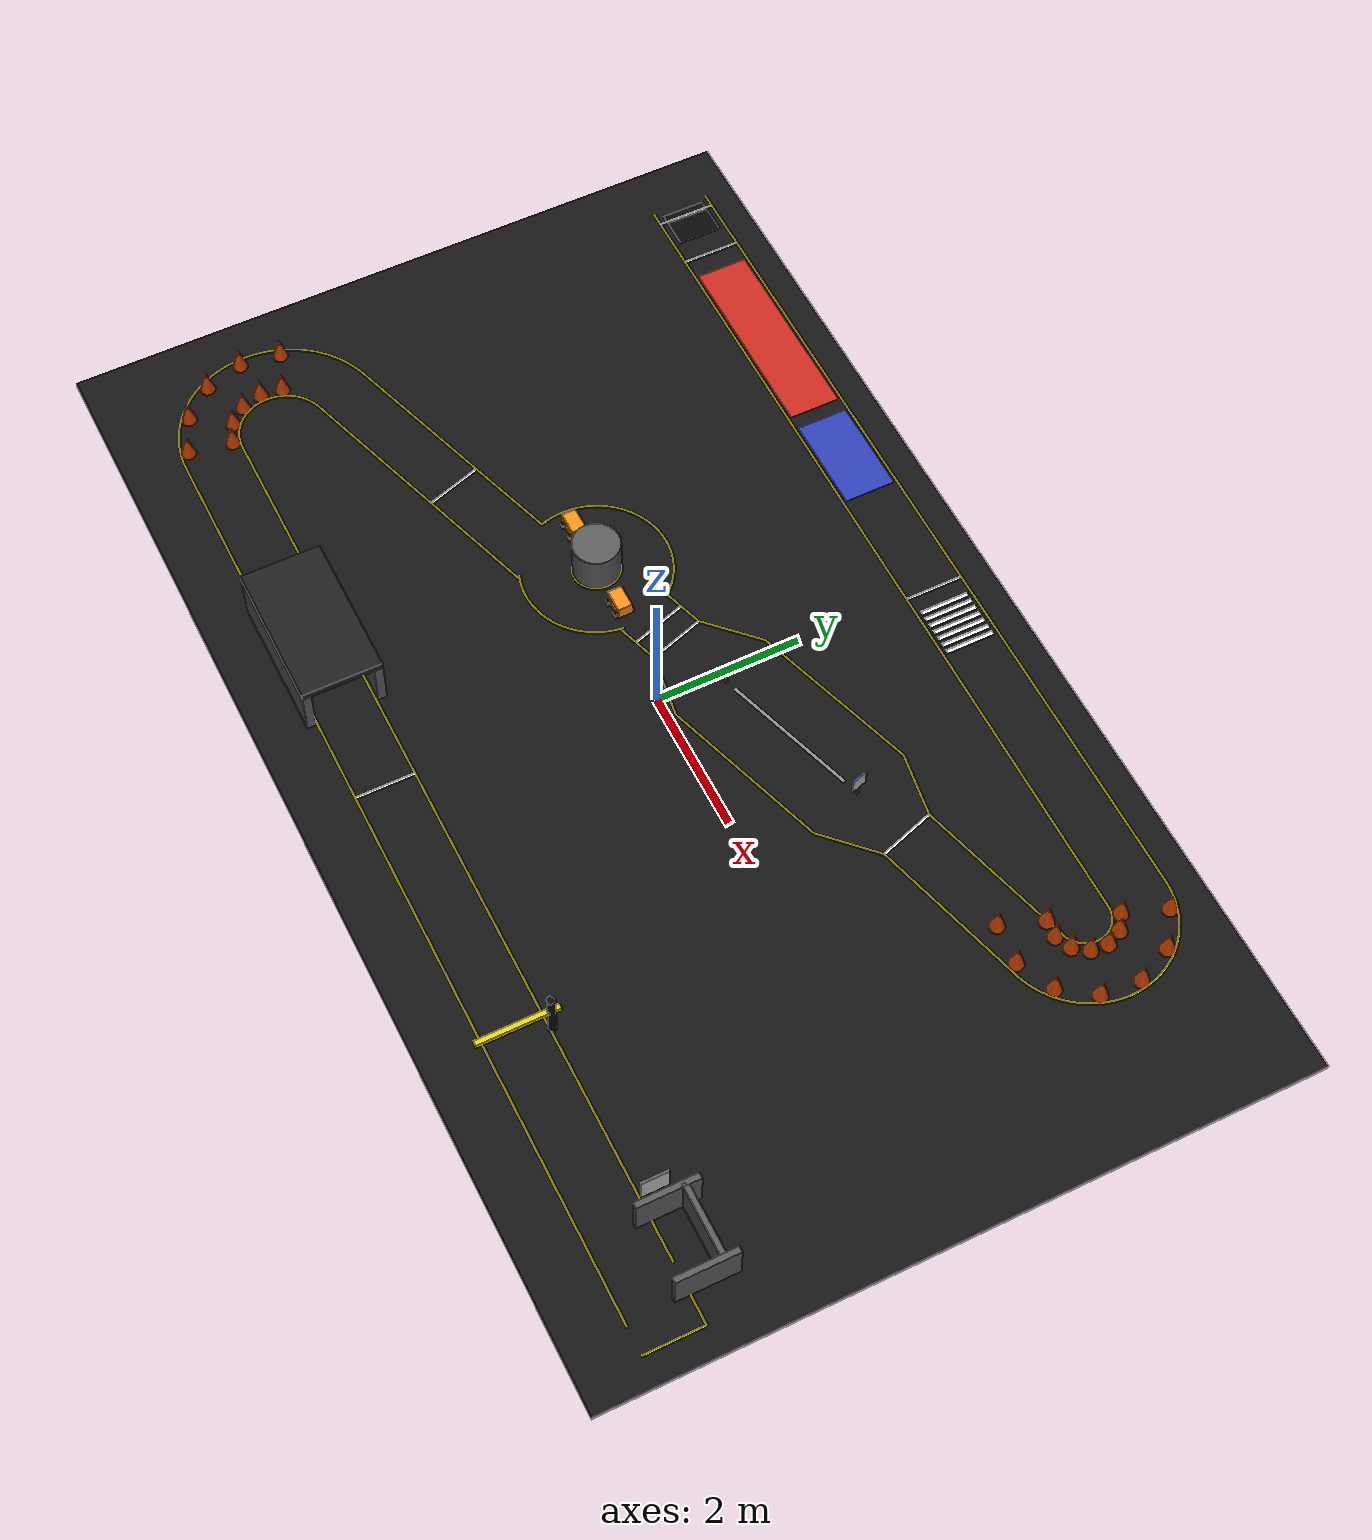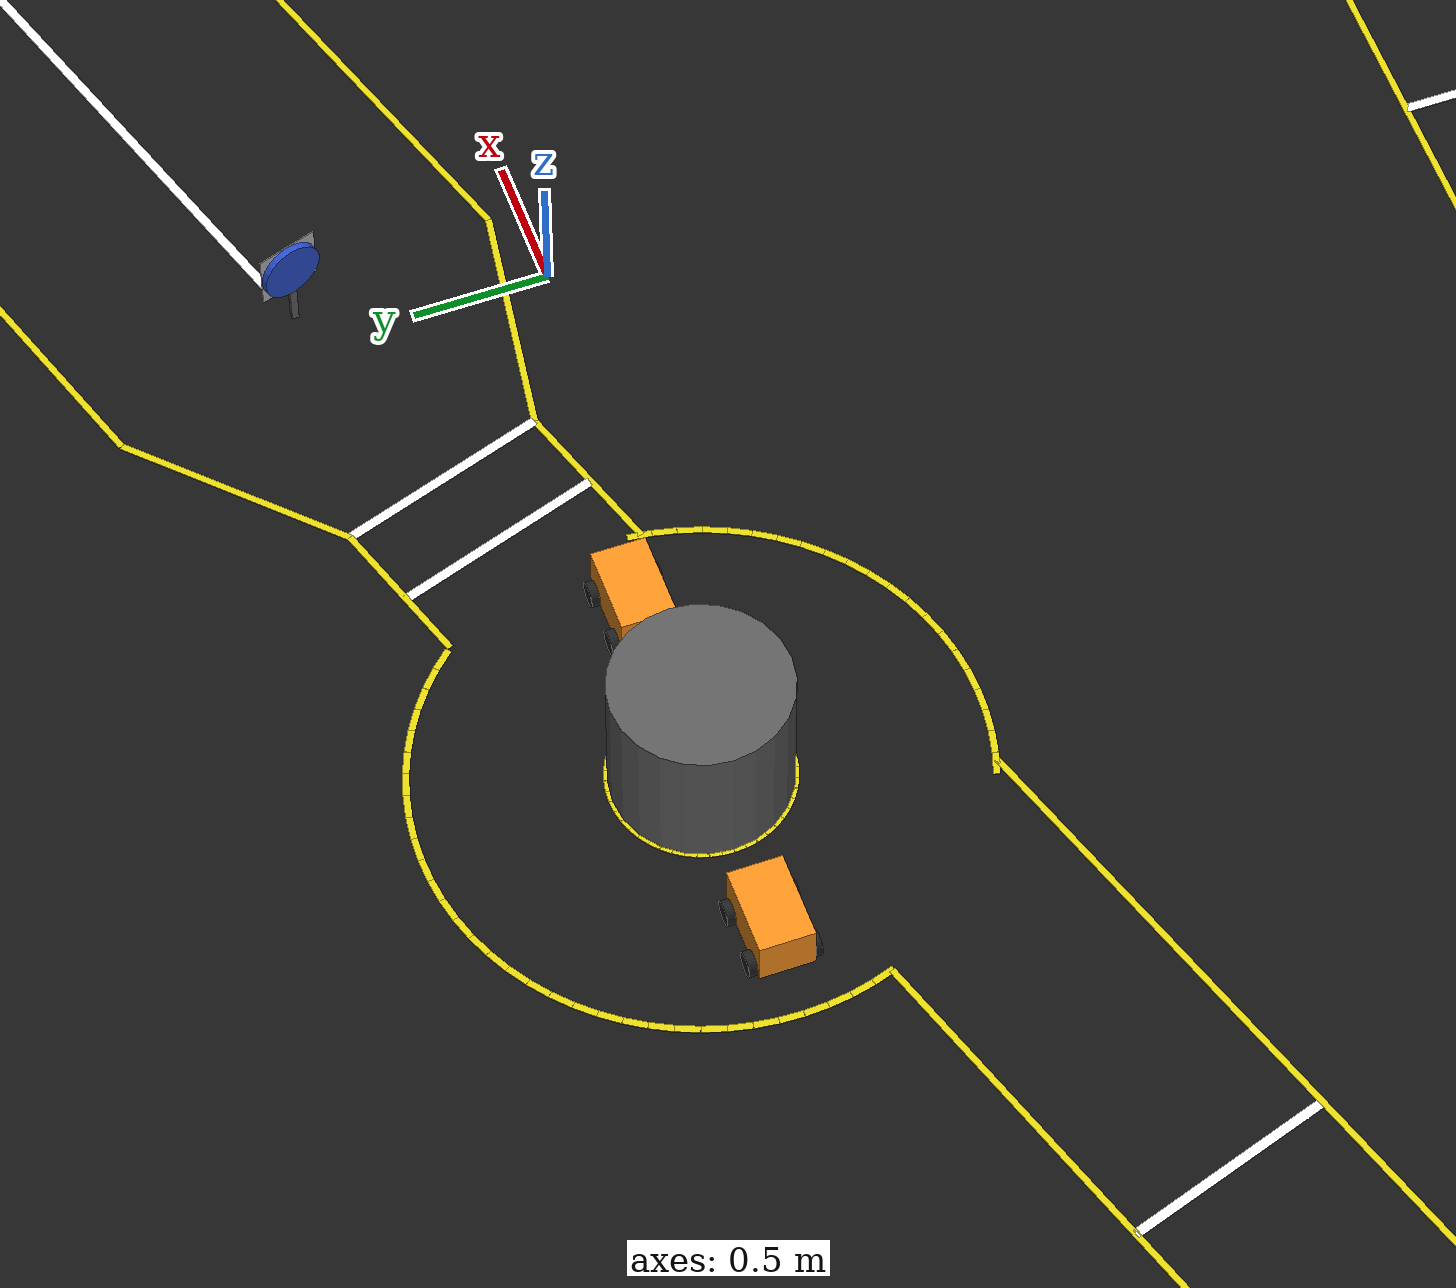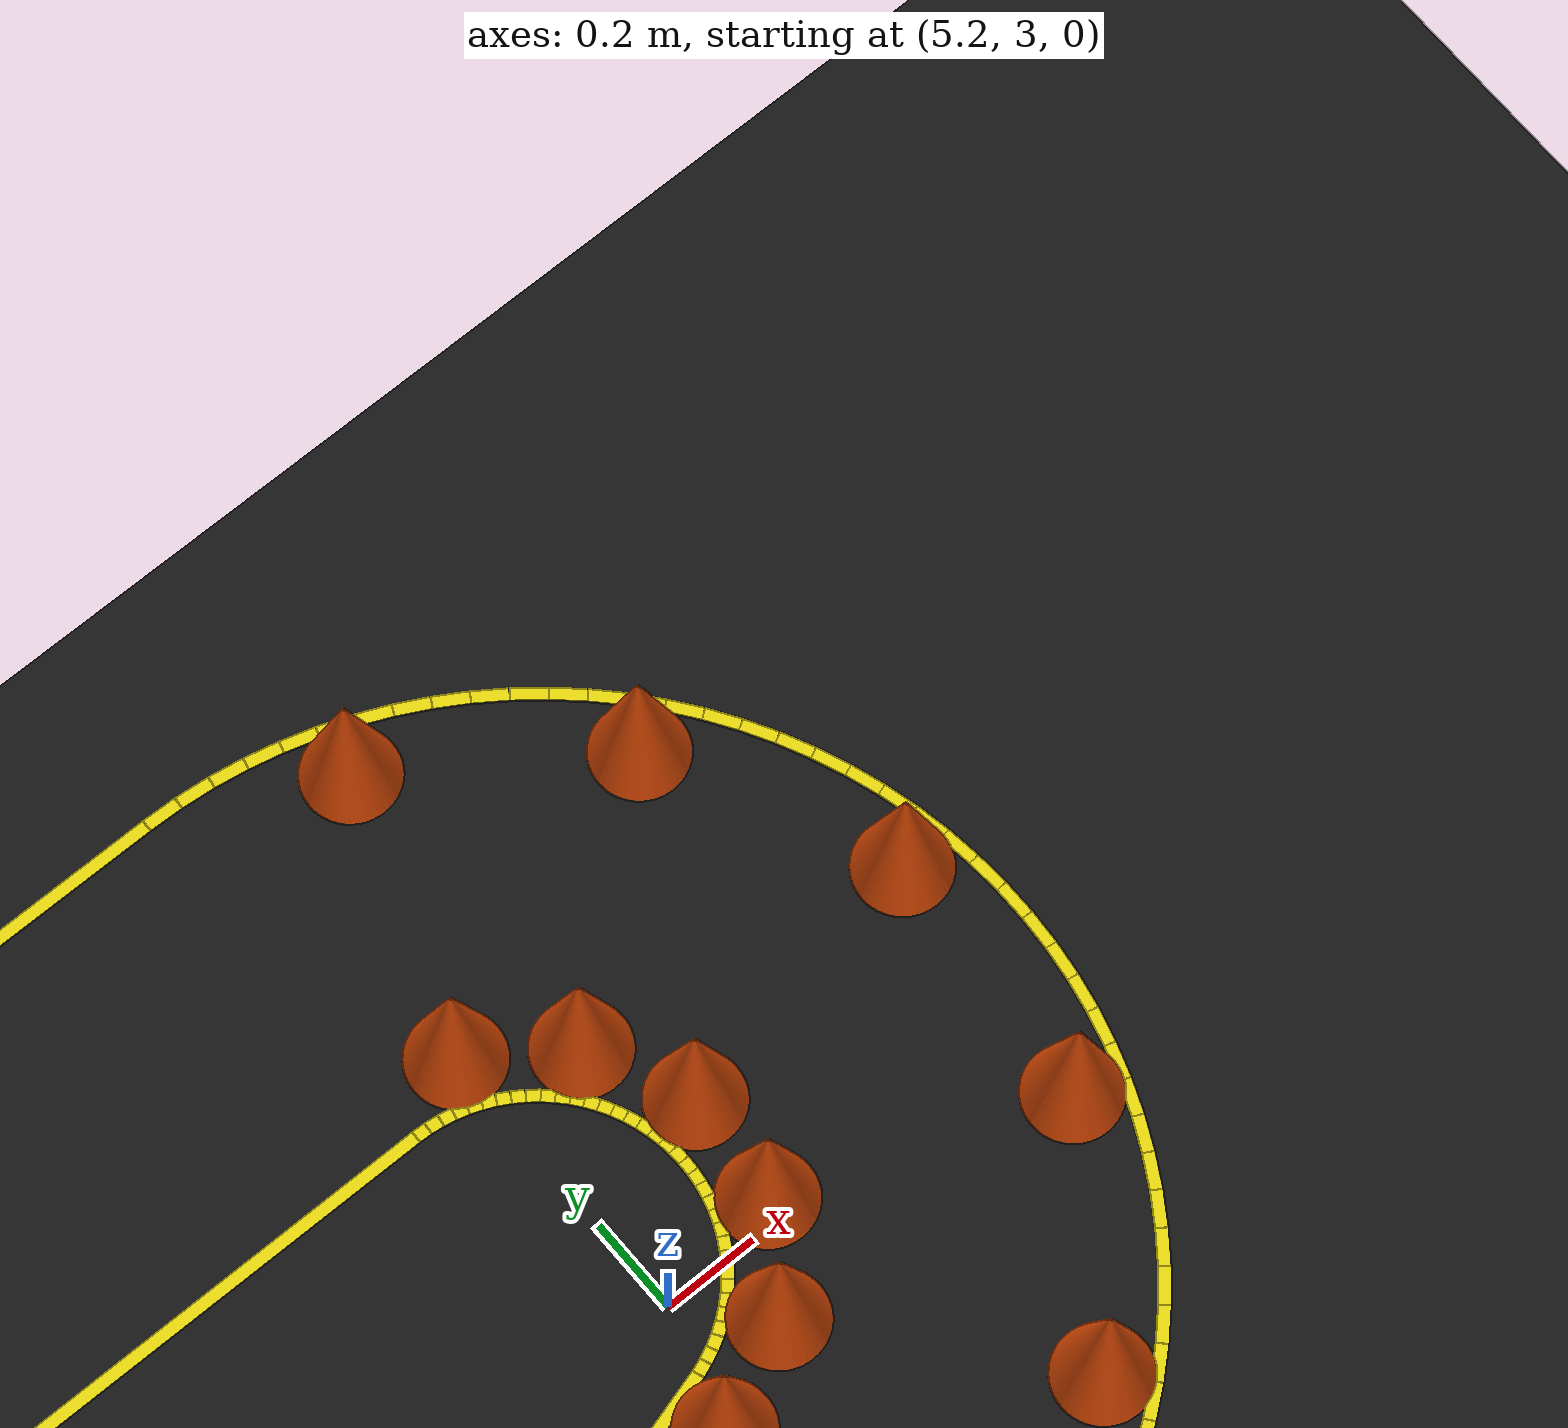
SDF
<?xml version="1.0" encoding="utf-8"?>
<sdf version="1.6">
  <world name="limo_competition">
    <gravity>0 0 -9.81</gravity>
    <physics name="default_physics" type="ode">
      <max_step_size>0.001</max_step_size>
      <real_time_factor>1.0</real_time_factor>
    </physics>
    <include>
      <uri>model://sun</uri>
    </include>
    <scene>
      <ambient>0.5 0.5 0.5 1</ambient>
      <background>0.72 0.72 0.72 1</background>
      <shadows>true</shadows>
    </scene>
    <plugin name="gazebo_ros_state" filename="libgazebo_ros_state.so">
      <ros>
        <namespace>/gazebo</namespace>
      </ros>
    </plugin>
    <model name="arena_ground">
      <static>true</static>
      <pose>0.0 0.0 -0.025 0 0 0.0</pose>
      <link name="link">
        <collision name="collision">
          <geometry>
            <box>
              <size>16.0 9.5 0.05</size>
            </box>
          </geometry>
        </collision>
        <visual name="visual">
          <geometry>
            <box>
              <size>16.0 9.5 0.05</size>
            </box>
          </geometry>
          <material>
            <ambient>0.08 0.08 0.08 1.0</ambient>
            <diffuse>0.08 0.08 0.08 1.0</diffuse>
            <specular>0.05 0.05 0.05 1</specular>
          </material>
        </visual>
      </link>
    </model>
    <model name="top_outer_1">
      <static>true</static>
      <pose>-1.1 4.35 0.003 0 0 0.0</pose>
      <link name="link">
        <visual name="visual">
          <geometry>
            <box>
              <size>12.3 0.025 0.004</size>
            </box>
          </geometry>
          <material>
            <ambient>0.88 0.82 0.05 1.0</ambient>
            <diffuse>0.88 0.82 0.05 1.0</diffuse>
            <specular>0.05 0.05 0.05 1</specular>
          </material>
        </visual>
      </link>
    </model>
    <model name="top_inner_1">
      <static>true</static>
      <pose>-1.1 3.55 0.003 0 0 0.0</pose>
      <link name="link">
        <visual name="visual">
          <geometry>
            <box>
              <size>12.3 0.025 0.004</size>
            </box>
          </geometry>
          <material>
            <ambient>0.88 0.82 0.05 1.0</ambient>
            <diffuse>0.88 0.82 0.05 1.0</diffuse>
            <specular>0.05 0.05 0.05 1</specular>
          </material>
        </visual>
      </link>
    </model>
    <model name="start_zone_black">
      <static>true</static>
      <pose>-6.9 3.9499999999999997 0.003 0 0 0.0</pose>
      <link name="link">
        <visual name="visual">
          <geometry>
            <box>
              <size>0.55 0.62 0.004</size>
            </box>
          </geometry>
          <material>
            <ambient>0.03 0.03 0.03 1.0</ambient>
            <diffuse>0.03 0.03 0.03 1.0</diffuse>
            <specular>0.05 0.05 0.05 1</specular>
          </material>
        </visual>
      </link>
    </model>
    <model name="start_line_main_1">
      <static>true</static>
      <pose>-6.28 3.9499999999999997 0.003 0 0 1.5707963267948966</pose>
      <link name="link">
        <visual name="visual">
          <geometry>
            <box>
              <size>0.7999999999999998 0.035 0.004</size>
            </box>
          </geometry>
          <material>
            <ambient>0.95 0.95 0.95 1.0</ambient>
            <diffuse>0.95 0.95 0.95 1.0</diffuse>
            <specular>0.05 0.05 0.05 1</specular>
          </material>
        </visual>
      </link>
    </model>
    <model name="start_line_back_1">
      <static>true</static>
      <pose>-7.05 3.9499999999999997 0.003 0 0 1.5707963267948966</pose>
      <link name="link">
        <visual name="visual">
          <geometry>
            <box>
              <size>0.7999999999999998 0.035 0.004</size>
            </box>
          </geometry>
          <material>
            <ambient>0.95 0.95 0.95 1.0</ambient>
            <diffuse>0.95 0.95 0.95 1.0</diffuse>
            <specular>0.05 0.05 0.05 1</specular>
          </material>
        </visual>
      </link>
    </model>
    <model name="red_speed_zone">
      <static>true</static>
      <pose>-4.6 3.9499999999999997 0.003 0 0 0.0</pose>
      <link name="link">
        <visual name="visual">
          <geometry>
            <box>
              <size>2.75 0.72 0.004</size>
            </box>
          </geometry>
          <material>
            <ambient>0.78 0.16 0.12 1.0</ambient>
            <diffuse>0.78 0.16 0.12 1.0</diffuse>
            <specular>0.05 0.05 0.05 1</specular>
          </material>
        </visual>
      </link>
    </model>
    <model name="blue_speed_zone">
      <static>true</static>
      <pose>-2.35 3.9499999999999997 0.003 0 0 0.0</pose>
      <link name="link">
        <visual name="visual">
          <geometry>
            <box>
              <size>1.35 0.72 0.004</size>
            </box>
          </geometry>
          <material>
            <ambient>0.18 0.24 0.7 1.0</ambient>
            <diffuse>0.18 0.24 0.7 1.0</diffuse>
            <specular>0.05 0.05 0.05 1</specular>
          </material>
        </visual>
      </link>
    </model>
    <model name="crosswalk_mission_start_1">
      <static>true</static>
      <pose>0.050000000000000044 3.9499999999999997 0.003 0 0 1.5707963267948966</pose>
      <link name="link">
        <visual name="visual">
          <geometry>
            <box>
              <size>0.7999999999999998 0.035 0.004</size>
            </box>
          </geometry>
          <material>
            <ambient>0.95 0.95 0.95 1.0</ambient>
            <diffuse>0.95 0.95 0.95 1.0</diffuse>
            <specular>0.05 0.05 0.05 1</specular>
          </material>
        </visual>
      </link>
    </model>
    <model name="crosswalk_1">
      <static>true</static>
      <pose>0.32 3.9499999999999997 0.003 0 0 0.0</pose>
      <link name="link">
        <visual name="visual">
          <geometry>
            <box>
              <size>0.06 0.68 0.004</size>
            </box>
          </geometry>
          <material>
            <ambient>0.95 0.95 0.95 1.0</ambient>
            <diffuse>0.95 0.95 0.95 1.0</diffuse>
            <specular>0.05 0.05 0.05 1</specular>
          </material>
        </visual>
      </link>
    </model>
    <model name="crosswalk_2">
      <static>true</static>
      <pose>0.43000000000000005 3.9499999999999997 0.003 0 0 0.0</pose>
      <link name="link">
        <visual name="visual">
          <geometry>
            <box>
              <size>0.06 0.68 0.004</size>
            </box>
          </geometry>
          <material>
            <ambient>0.95 0.95 0.95 1.0</ambient>
            <diffuse>0.95 0.95 0.95 1.0</diffuse>
            <specular>0.05 0.05 0.05 1</specular>
          </material>
        </visual>
      </link>
    </model>
    <model name="crosswalk_3">
      <static>true</static>
      <pose>0.54 3.9499999999999997 0.003 0 0 0.0</pose>
      <link name="link">
        <visual name="visual">
          <geometry>
            <box>
              <size>0.06 0.68 0.004</size>
            </box>
          </geometry>
          <material>
            <ambient>0.95 0.95 0.95 1.0</ambient>
            <diffuse>0.95 0.95 0.95 1.0</diffuse>
            <specular>0.05 0.05 0.05 1</specular>
          </material>
        </visual>
      </link>
    </model>
    <model name="crosswalk_4">
      <static>true</static>
      <pose>0.65 3.9499999999999997 0.003 0 0 0.0</pose>
      <link name="link">
        <visual name="visual">
          <geometry>
            <box>
              <size>0.06 0.68 0.004</size>
            </box>
          </geometry>
          <material>
            <ambient>0.95 0.95 0.95 1.0</ambient>
            <diffuse>0.95 0.95 0.95 1.0</diffuse>
            <specular>0.05 0.05 0.05 1</specular>
          </material>
        </visual>
      </link>
    </model>
    <model name="crosswalk_5">
      <static>true</static>
      <pose>0.76 3.9499999999999997 0.003 0 0 0.0</pose>
      <link name="link">
        <visual name="visual">
          <geometry>
            <box>
              <size>0.06 0.68 0.004</size>
            </box>
          </geometry>
          <material>
            <ambient>0.95 0.95 0.95 1.0</ambient>
            <diffuse>0.95 0.95 0.95 1.0</diffuse>
            <specular>0.05 0.05 0.05 1</specular>
          </material>
        </visual>
      </link>
    </model>
    <model name="crosswalk_6">
      <static>true</static>
      <pose>0.87 3.9499999999999997 0.003 0 0 0.0</pose>
      <link name="link">
        <visual name="visual">
          <geometry>
            <box>
              <size>0.06 0.68 0.004</size>
            </box>
          </geometry>
          <material>
            <ambient>0.95 0.95 0.95 1.0</ambient>
            <diffuse>0.95 0.95 0.95 1.0</diffuse>
            <specular>0.05 0.05 0.05 1</specular>
          </material>
        </visual>
      </link>
    </model>
    <model name="crosswalk_7">
      <static>true</static>
      <pose>0.98 3.9499999999999997 0.003 0 0 0.0</pose>
      <link name="link">
        <visual name="visual">
          <geometry>
            <box>
              <size>0.06 0.68 0.004</size>
            </box>
          </geometry>
          <material>
            <ambient>0.95 0.95 0.95 1.0</ambient>
            <diffuse>0.95 0.95 0.95 1.0</diffuse>
            <specular>0.05 0.05 0.05 1</specular>
          </material>
        </visual>
      </link>
    </model>
    <model name="right_uturn_outer_1">
      <static>true</static>
      <pose>5.086923989469532 4.348813226583053 0.003 0 0 -0.032129924866255814</pose>
      <link name="link">
        <visual name="visual">
          <geometry>
            <box>
              <size>0.07388611316043835 0.025 0.004</size>
            </box>
          </geometry>
          <material>
            <ambient>0.88 0.82 0.05 1.0</ambient>
            <diffuse>0.88 0.82 0.05 1.0</diffuse>
            <specular>0.05 0.05 0.05 1</specular>
          </material>
        </visual>
      </link>
    </model>
    <model name="right_uturn_outer_2">
      <static>true</static>
      <pose>5.16061954959416 4.344071031806196 0.003 0 0 -0.09638977459877685</pose>
      <link name="link">
        <visual name="visual">
          <geometry>
            <box>
              <size>0.07388611316043744 0.025 0.004</size>
            </box>
          </geometry>
          <material>
            <ambient>0.88 0.82 0.05 1.0</ambient>
            <diffuse>0.88 0.82 0.05 1.0</diffuse>
            <specular>0.05 0.05 0.05 1</specular>
          </material>
        </visual>
      </link>
    </model>
    <model name="right_uturn_outer_3">
      <static>true</static>
      <pose>5.233858482446256 4.334606217594047 0.003 0 0 -0.1606496243312973</pose>
      <link name="link">
        <visual name="visual">
          <geometry>
            <box>
              <size>0.07388611316043811 0.025 0.004</size>
            </box>
          </geometry>
          <material>
            <ambient>0.88 0.82 0.05 1.0</ambient>
            <diffuse>0.88 0.82 0.05 1.0</diffuse>
            <specular>0.05 0.05 0.05 1</specular>
          </material>
        </visual>
      </link>
    </model>
    <model name="right_uturn_outer_4">
      <static>true</static>
      <pose>5.306338464482883 4.320457853824529 0.003 0 0 -0.22490947406381037</pose>
      <link name="link">
        <visual name="visual">
          <geometry>
            <box>
              <size>0.07388611316043771 0.025 0.004</size>
            </box>
          </geometry>
          <material>
            <ambient>0.88 0.82 0.05 1.0</ambient>
            <diffuse>0.88 0.82 0.05 1.0</diffuse>
            <specular>0.05 0.05 0.05 1</specular>
          </material>
        </visual>
      </link>
    </model>
    <model name="right_uturn_outer_5">
      <static>true</static>
      <pose>5.377760305039894 4.301684343635085 0.003 0 0 -0.28916932379633753</pose>
      <link name="link">
        <visual name="visual">
          <geometry>
            <box>
              <size>0.07388611316043814 0.025 0.004</size>
            </box>
          </geometry>
          <material>
            <ambient>0.88 0.82 0.05 1.0</ambient>
            <diffuse>0.88 0.82 0.05 1.0</diffuse>
            <specular>0.05 0.05 0.05 1</specular>
          </material>
        </visual>
      </link>
    </model>
    <model name="right_uturn_outer_6">
      <static>true</static>
      <pose>5.447829181363334 4.278363182339925 0.003 0 0 -0.3534291735288546</pose>
      <link name="link">
        <visual name="visual">
          <geometry>
            <box>
              <size>0.07388611316043825 0.025 0.004</size>
            </box>
          </geometry>
          <material>
            <ambient>0.88 0.82 0.05 1.0</ambient>
            <diffuse>0.88 0.82 0.05 1.0</diffuse>
            <specular>0.05 0.05 0.05 1</specular>
          </material>
        </visual>
      </link>
    </model>
    <model name="right_uturn_outer_7">
      <static>true</static>
      <pose>5.5162558556105035 4.250590637536537 0.003 0 0 -0.41768902326136537</pose>
      <link name="link">
        <visual name="visual">
          <geometry>
            <box>
              <size>0.07388611316043808 0.025 0.004</size>
            </box>
          </geometry>
          <material>
            <ambient>0.88 0.82 0.05 1.0</ambient>
            <diffuse>0.88 0.82 0.05 1.0</diffuse>
            <specular>0.05 0.05 0.05 1</specular>
          </material>
        </visual>
      </link>
    </model>
    <model name="right_uturn_outer_8">
      <static>true</static>
      <pose>5.582757868797031 4.218481351721943 0.003 0 0 -0.4819488729938875</pose>
      <link name="link">
        <visual name="visual">
          <geometry>
            <box>
              <size>0.07388611316043753 0.025 0.004</size>
            </box>
          </geometry>
          <material>
            <ambient>0.88 0.82 0.05 1.0</ambient>
            <diffuse>0.88 0.82 0.05 1.0</diffuse>
            <specular>0.05 0.05 0.05 1</specular>
          </material>
        </visual>
      </link>
    </model>
    <model name="right_uturn_outer_9">
      <static>true</static>
      <pose>5.647060706761444 4.182167869059071 0.003 0 0 -0.5462087227264127</pose>
      <link name="link">
        <visual name="visual">
          <geometry>
            <box>
              <size>0.0738861131604378 0.025 0.004</size>
            </box>
          </geometry>
          <material>
            <ambient>0.88 0.82 0.05 1.0</ambient>
            <diffuse>0.88 0.82 0.05 1.0</diffuse>
            <specular>0.05 0.05 0.05 1</specular>
          </material>
        </visual>
      </link>
    </model>
    <model name="right_uturn_outer_10">
      <static>true</static>
      <pose>5.708898933334246 4.141800088246706 0.003 0 0 -0.6104685724589264</pose>
      <link name="link">
        <visual name="visual">
          <geometry>
            <box>
              <size>0.07388611316043792 0.025 0.004</size>
            </box>
          </geometry>
          <material>
            <ambient>0.88 0.82 0.05 1.0</ambient>
            <diffuse>0.88 0.82 0.05 1.0</diffuse>
            <specular>0.05 0.05 0.05 1</specular>
          </material>
        </visual>
      </link>
    </model>
    <model name="right_uturn_outer_11">
      <static>true</static>
      <pose>5.76801728603388 4.097544643751525 0.003 0 0 -0.6747284221914416</pose>
      <link name="link">
        <visual name="visual">
          <geometry>
            <box>
              <size>0.07388611316043754 0.025 0.004</size>
            </box>
          </geometry>
          <material>
            <ambient>0.88 0.82 0.05 1.0</ambient>
            <diffuse>0.88 0.82 0.05 1.0</diffuse>
            <specular>0.05 0.05 0.05 1</specular>
          </material>
        </visual>
      </link>
    </model>
    <model name="right_uturn_outer_12">
      <static>true</static>
      <pose>5.824171729766649 4.049584217956422 0.003 0 0 -0.7389882719239559</pose>
      <link name="link">
        <visual name="visual">
          <geometry>
            <box>
              <size>0.07388611316043829 0.025 0.004</size>
            </box>
          </geometry>
          <material>
            <ambient>0.88 0.82 0.05 1.0</ambient>
            <diffuse>0.88 0.82 0.05 1.0</diffuse>
            <specular>0.05 0.05 0.05 1</specular>
          </material>
        </visual>
      </link>
    </model>
    <model name="right_uturn_outer_13">
      <static>true</static>
      <pose>5.877130464181022 3.998116787064524 0.003 0 0 -0.8032481216564864</pose>
      <link name="link">
        <visual name="visual">
          <geometry>
            <box>
              <size>0.0738861131604382 0.025 0.004</size>
            </box>
          </geometry>
          <material>
            <ambient>0.88 0.82 0.05 1.0</ambient>
            <diffuse>0.88 0.82 0.05 1.0</diffuse>
            <specular>0.05 0.05 0.05 1</specular>
          </material>
        </visual>
      </link>
    </model>
    <model name="right_uturn_outer_14">
      <static>true</static>
      <pose>5.926674880518047 3.94335480387173 0.003 0 0 -0.8675079713890038</pose>
      <link name="link">
        <visual name="visual">
          <geometry>
            <box>
              <size>0.07388611316043761 0.025 0.004</size>
            </box>
          </geometry>
          <material>
            <ambient>0.88 0.82 0.05 1.0</ambient>
            <diffuse>0.88 0.82 0.05 1.0</diffuse>
            <specular>0.05 0.05 0.05 1</specular>
          </material>
        </visual>
      </link>
    </model>
    <model name="right_uturn_outer_15">
      <static>true</static>
      <pose>5.972600464008101 3.8855243207812147 0.003 0 0 -0.9317678211215145</pose>
      <link name="link">
        <visual name="visual">
          <geometry>
            <box>
              <size>0.07388611316043797 0.025 0.004</size>
            </box>
          </geometry>
          <material>
            <ambient>0.88 0.82 0.05 1.0</ambient>
            <diffuse>0.88 0.82 0.05 1.0</diffuse>
            <specular>0.05 0.05 0.05 1</specular>
          </material>
        </visual>
      </link>
    </model>
    <model name="right_uturn_outer_16">
      <static>true</static>
      <pose>6.014717638088946 3.8248640566800076 0.003 0 0 -0.9960276708540327</pose>
      <link name="link">
        <visual name="visual">
          <geometry>
            <box>
              <size>0.073886113160438 0.025 0.004</size>
            </box>
          </geometry>
          <material>
            <ambient>0.88 0.82 0.05 1.0</ambient>
            <diffuse>0.88 0.82 0.05 1.0</diffuse>
            <specular>0.05 0.05 0.05 1</specular>
          </material>
        </visual>
      </link>
    </model>
    <model name="right_uturn_outer_17">
      <static>true</static>
      <pose>6.052852546960246 3.761624411529501 0.003 0 0 -1.0602875205865574</pose>
      <link name="link">
        <visual name="visual">
          <geometry>
            <box>
              <size>0.07388611316043778 0.025 0.004</size>
            </box>
          </geometry>
          <material>
            <ambient>0.88 0.82 0.05 1.0</ambient>
            <diffuse>0.88 0.82 0.05 1.0</diffuse>
            <specular>0.05 0.05 0.05 1</specular>
          </material>
        </visual>
      </link>
    </model>
    <model name="right_uturn_outer_18">
      <static>true</static>
      <pose>6.086847773244241 3.696066432737562 0.003 0 0 -1.124547370319076</pose>
      <link name="link">
        <visual name="visual">
          <geometry>
            <box>
              <size>0.073886113160438 0.025 0.004</size>
            </box>
          </geometry>
          <material>
            <ambient>0.88 0.82 0.05 1.0</ambient>
            <diffuse>0.88 0.82 0.05 1.0</diffuse>
            <specular>0.05 0.05 0.05 1</specular>
          </material>
        </visual>
      </link>
    </model>
    <model name="right_uturn_outer_19">
      <static>true</static>
      <pose>6.1165629877901235 3.62846073757897 0.003 0 0 -1.1888072200515847</pose>
      <link name="link">
        <visual name="visual">
          <geometry>
            <box>
              <size>0.073886113160438 0.025 0.004</size>
            </box>
          </geometry>
          <material>
            <ambient>0.88 0.82 0.05 1.0</ambient>
            <diffuse>0.88 0.82 0.05 1.0</diffuse>
            <specular>0.05 0.05 0.05 1</specular>
          </material>
        </visual>
      </link>
    </model>
    <model name="right_uturn_outer_20">
      <static>true</static>
      <pose>6.141875528939801 3.5590863961123276 0.003 0 0 -1.253067069784118</pose>
      <link name="link">
        <visual name="visual">
          <geometry>
            <box>
              <size>0.07388611316043787 0.025 0.004</size>
            </box>
          </geometry>
          <material>
            <ambient>0.88 0.82 0.05 1.0</ambient>
            <diffuse>0.88 0.82 0.05 1.0</diffuse>
            <specular>0.05 0.05 0.05 1</specular>
          </material>
        </visual>
      </link>
    </model>
    <model name="right_uturn_outer_21">
      <static>true</static>
      <pose>6.162680908863876 3.488229779204665 0.003 0 0 -1.3173269195166295</pose>
      <link name="link">
        <visual name="visual">
          <geometry>
            <box>
              <size>0.07388611316043839 0.025 0.004</size>
            </box>
          </geometry>
          <material>
            <ambient>0.88 0.82 0.05 1.0</ambient>
            <diffuse>0.88 0.82 0.05 1.0</diffuse>
            <specular>0.05 0.05 0.05 1</specular>
          </material>
        </visual>
      </link>
    </model>
    <model name="right_uturn_outer_22">
      <static>true</static>
      <pose>6.178893244877743 3.4161833764189753 0.003 0 0 -1.3815867692491481</pose>
      <link name="link">
        <visual name="visual">
          <geometry>
            <box>
              <size>0.07388611316043743 0.025 0.004</size>
            </box>
          </geometry>
          <material>
            <ambient>0.88 0.82 0.05 1.0</ambient>
            <diffuse>0.88 0.82 0.05 1.0</diffuse>
            <specular>0.05 0.05 0.05 1</specular>
          </material>
        </visual>
      </link>
    </model>
    <model name="right_uturn_outer_23">
      <static>true</static>
      <pose>6.190445613957378 3.343244588644348 0.003 0 0 -1.4458466189816699</pose>
      <link name="link">
        <visual name="visual">
          <geometry>
            <box>
              <size>0.07388611316043785 0.025 0.004</size>
            </box>
          </geometry>
          <material>
            <ambient>0.88 0.82 0.05 1.0</ambient>
            <diffuse>0.88 0.82 0.05 1.0</diffuse>
            <specular>0.05 0.05 0.05 1</specular>
          </material>
        </visual>
      </link>
    </model>
    <model name="right_uturn_outer_24">
      <static>true</static>
      <pose>6.197290328991382 3.26971450045259 0.003 0 0 -1.5101064687141834</pose>
      <link name="link">
        <visual name="visual">
          <geometry>
            <box>
              <size>0.07388611316043785 0.025 0.004</size>
            </box>
          </geometry>
          <material>
            <ambient>0.88 0.82 0.05 1.0</ambient>
            <diffuse>0.88 0.82 0.05 1.0</diffuse>
            <specular>0.05 0.05 0.05 1</specular>
          </material>
        </visual>
      </link>
    </model>
    <model name="right_uturn_outer_25">
      <static>true</static>
      <pose>6.199399135628979 3.195896637248962 0.003 0 0 -1.5743663184466952</pose>
      <link name="link">
        <visual name="visual">
          <geometry>
            <box>
              <size>0.07388611316043815 0.025 0.004</size>
            </box>
          </geometry>
          <material>
            <ambient>0.88 0.82 0.05 1.0</ambient>
            <diffuse>0.88 0.82 0.05 1.0</diffuse>
            <specular>0.05 0.05 0.05 1</specular>
          </material>
        </visual>
      </link>
    </model>
    <model name="right_uturn_outer_26">
      <static>true</static>
      <pose>6.196763328911352 3.1220957123473614 0.003 0 0 -1.638626168179219</pose>
      <link name="link">
        <visual name="visual">
          <geometry>
            <box>
              <size>0.0738861131604379 0.025 0.004</size>
            </box>
          </geometry>
          <material>
            <ambient>0.88 0.82 0.05 1.0</ambient>
            <diffuse>0.88 0.82 0.05 1.0</diffuse>
            <specular>0.05 0.05 0.05 1</specular>
          </material>
        </visual>
      </link>
    </model>
    <model name="right_uturn_outer_27">
      <static>true</static>
      <pose>6.189393789204919 3.048616369141943 0.003 0 0 -1.702886017911743</pose>
      <link name="link">
        <visual name="visual">
          <geometry>
            <box>
              <size>0.07388611316043817 0.025 0.004</size>
            </box>
          </geometry>
          <material>
            <ambient>0.88 0.82 0.05 1.0</ambient>
            <diffuse>0.88 0.82 0.05 1.0</diffuse>
            <specular>0.05 0.05 0.05 1</specular>
          </material>
        </visual>
      </link>
    </model>
    <model name="right_uturn_outer_28">
      <static>true</static>
      <pose>6.177320937288178 2.9757619235673536 0.003 0 0 -1.7671458676442715</pose>
      <link name="link">
        <visual name="visual">
          <geometry>
            <box>
              <size>0.07388611316043785 0.025 0.004</size>
            </box>
          </geometry>
          <material>
            <ambient>0.88 0.82 0.05 1.0</ambient>
            <diffuse>0.88 0.82 0.05 1.0</diffuse>
            <specular>0.05 0.05 0.05 1</specular>
          </material>
        </visual>
      </link>
    </model>
    <model name="right_uturn_outer_29">
      <static>true</static>
      <pose>6.160594608777554 2.9038331120385994 0.003 0 0 -1.831405717376767</pose>
      <link name="link">
        <visual name="visual">
          <geometry>
            <box>
              <size>0.07388611316043753 0.025 0.004</size>
            </box>
          </geometry>
          <material>
            <ambient>0.88 0.82 0.05 1.0</ambient>
            <diffuse>0.88 0.82 0.05 1.0</diffuse>
            <specular>0.05 0.05 0.05 1</specular>
          </material>
        </visual>
      </link>
    </model>
    <model name="right_uturn_outer_30">
      <static>true</static>
      <pose>6.139283848410576 2.8331268500389326 0.003 0 0 -1.8956655671092968</pose>
      <link name="link">
        <visual name="visual">
          <geometry>
            <box>
              <size>0.07388611316043814 0.025 0.004</size>
            </box>
          </geometry>
          <material>
            <ambient>0.88 0.82 0.05 1.0</ambient>
            <diffuse>0.88 0.82 0.05 1.0</diffuse>
            <specular>0.05 0.05 0.05 1</specular>
          </material>
        </visual>
      </link>
    </model>
    <model name="right_uturn_outer_31">
      <static>true</static>
      <pose>6.1134766250355845 2.763935006480189 0.003 0 0 -1.9599254168418128</pose>
      <link name="link">
        <visual name="visual">
          <geometry>
            <box>
              <size>0.07388611316043794 0.025 0.004</size>
            </box>
          </geometry>
          <material>
            <ambient>0.88 0.82 0.05 1.0</ambient>
            <diffuse>0.88 0.82 0.05 1.0</diffuse>
            <specular>0.05 0.05 0.05 1</specular>
          </material>
        </visual>
      </link>
    </model>
    <model name="right_uturn_outer_32">
      <static>true</static>
      <pose>6.083279468484465 2.696543198894908 0.003 0 0 -2.0241852665743365</pose>
      <link name="link">
        <visual name="visual">
          <geometry>
            <box>
              <size>0.07388611316043807 0.025 0.004</size>
            </box>
          </geometry>
          <material>
            <ambient>0.88 0.82 0.05 1.0</ambient>
            <diffuse>0.88 0.82 0.05 1.0</diffuse>
            <specular>0.05 0.05 0.05 1</specular>
          </material>
        </visual>
      </link>
    </model>
    <model name="right_uturn_outer_33">
      <static>true</static>
      <pose>6.048817029827346 2.6312296144335674 0.003 0 0 -2.0884451163068483</pose>
      <link name="link">
        <visual name="visual">
          <geometry>
            <box>
              <size>0.07388611316043762 0.025 0.004</size>
            </box>
          </geometry>
          <material>
            <ambient>0.88 0.82 0.05 1.0</ambient>
            <diffuse>0.88 0.82 0.05 1.0</diffuse>
            <specular>0.05 0.05 0.05 1</specular>
          </material>
        </visual>
      </link>
    </model>
    <model name="right_uturn_outer_34">
      <static>true</static>
      <pose>6.010231566824512 2.568263861533747 0.003 0 0 -2.1527049660393724</pose>
      <link name="link">
        <visual name="visual">
          <geometry>
            <box>
              <size>0.07388611316043797 0.025 0.004</size>
            </box>
          </geometry>
          <material>
            <ambient>0.88 0.82 0.05 1.0</ambient>
            <diffuse>0.88 0.82 0.05 1.0</diffuse>
            <specular>0.05 0.05 0.05 1</specular>
          </material>
        </visual>
      </link>
    </model>
    <model name="right_uturn_outer_35">
      <static>true</static>
      <pose>5.967682356699518 2.5079058570014277 0.003 0 0 -2.2169648157718895</pose>
      <link name="link">
        <visual name="visual">
          <geometry>
            <box>
              <size>0.07388611316043821 0.025 0.004</size>
            </box>
          </geometry>
          <material>
            <ambient>0.88 0.82 0.05 1.0</ambient>
            <diffuse>0.88 0.82 0.05 1.0</diffuse>
            <specular>0.05 0.05 0.05 1</specular>
          </material>
        </visual>
      </link>
    </model>
    <model name="right_uturn_outer_36">
      <static>true</static>
      <pose>5.921345038657542 2.450404753098449 0.003 0 0 -2.2812246655044017</pose>
      <link name="link">
        <visual name="visual">
          <geometry>
            <box>
              <size>0.07388611316043799 0.025 0.004</size>
            </box>
          </geometry>
          <material>
            <ambient>0.88 0.82 0.05 1.0</ambient>
            <diffuse>0.88 0.82 0.05 1.0</diffuse>
            <specular>0.05 0.05 0.05 1</specular>
          </material>
        </visual>
      </link>
    </model>
    <model name="right_uturn_outer_37">
      <static>true</static>
      <pose>5.871410888862982 2.3959979090650108 0.003 0 0 -2.3454845152369255</pose>
      <link name="link">
        <visual name="visual">
          <geometry>
            <box>
              <size>0.07388611316043779 0.025 0.004</size>
            </box>
          </geometry>
          <material>
            <ambient>0.88 0.82 0.05 1.0</ambient>
            <diffuse>0.88 0.82 0.05 1.0</diffuse>
            <specular>0.05 0.05 0.05 1</specular>
          </material>
        </visual>
      </link>
    </model>
    <model name="right_uturn_outer_38">
      <static>true</static>
      <pose>5.818086030869142 2.3449099113226737 0.003 0 0 -2.409744364969441</pose>
      <link name="link">
        <visual name="visual">
          <geometry>
            <box>
              <size>0.07388611316043774 0.025 0.004</size>
            </box>
          </geometry>
          <material>
            <ambient>0.88 0.82 0.05 1.0</ambient>
            <diffuse>0.88 0.82 0.05 1.0</diffuse>
            <specular>0.05 0.05 0.05 1</specular>
          </material>
        </visual>
      </link>
    </model>
    <model name="right_uturn_outer_39">
      <static>true</static>
      <pose>5.761590584759253 2.297351646402379 0.003 0 0 -2.4740042147019605</pose>
      <link name="link">
        <visual name="visual">
          <geometry>
            <box>
              <size>0.07388611316043805 0.025 0.004</size>
            </box>
          </geometry>
          <material>
            <ambient>0.88 0.82 0.05 1.0</ambient>
            <diffuse>0.88 0.82 0.05 1.0</diffuse>
            <specular>0.05 0.05 0.05 1</specular>
          </material>
        </visual>
      </link>
    </model>
    <model name="right_uturn_outer_40">
      <static>true</static>
      <pose>5.702157758511129 2.2535194304243484 0.003 0 0 -2.5382640644344843</pose>
      <link name="link">
        <visual name="visual">
          <geometry>
            <box>
              <size>0.07388611316043814 0.025 0.004</size>
            </box>
          </geometry>
          <material>
            <ambient>0.88 0.82 0.05 1.0</ambient>
            <diffuse>0.88 0.82 0.05 1.0</diffuse>
            <specular>0.05 0.05 0.05 1</specular>
          </material>
        </visual>
      </link>
    </model>
    <model name="right_uturn_outer_41">
      <static>true</static>
      <pose>5.640032885336199 2.2135941987232894 0.003 0 0 -2.602523914167004</pose>
      <link name="link">
        <visual name="visual">
          <geometry>
            <box>
              <size>0.07388611316043792 0.025 0.004</size>
            </box>
          </geometry>
          <material>
            <ambient>0.88 0.82 0.05 1.0</ambient>
            <diffuse>0.88 0.82 0.05 1.0</diffuse>
            <specular>0.05 0.05 0.05 1</specular>
          </material>
        </visual>
      </link>
    </model>
    <model name="right_uturn_outer_42">
      <static>true</static>
      <pose>5.5754724109666896 2.177740758964066 0.003 0 0 -2.6667837638995144</pose>
      <link name="link">
        <visual name="visual">
          <geometry>
            <box>
              <size>0.07388611316043842 0.025 0.004</size>
            </box>
          </geometry>
          <material>
            <ambient>0.88 0.82 0.05 1.0</ambient>
            <diffuse>0.88 0.82 0.05 1.0</diffuse>
            <specular>0.05 0.05 0.05 1</specular>
          </material>
        </visual>
      </link>
    </model>
    <model name="right_uturn_outer_43">
      <static>true</static>
      <pose>5.508742835071356 2.1461071108308944 0.003 0 0 -2.731043613632039</pose>
      <link name="link">
        <visual name="visual">
          <geometry>
            <box>
              <size>0.07388611316043708 0.025 0.004</size>
            </box>
          </geometry>
          <material>
            <ambient>0.88 0.82 0.05 1.0</ambient>
            <diffuse>0.88 0.82 0.05 1.0</diffuse>
            <specular>0.05 0.05 0.05 1</specular>
          </material>
        </visual>
      </link>
    </model>
    <model name="right_uturn_outer_44">
      <static>true</static>
      <pose>5.440119611169492 2.1188238350983344 0.003 0 0 -2.7953034633645566</pose>
      <link name="link">
        <visual name="visual">
          <geometry>
            <box>
              <size>0.07388611316043821 0.025 0.004</size>
            </box>
          </geometry>
          <material>
            <ambient>0.88 0.82 0.05 1.0</ambient>
            <diffuse>0.88 0.82 0.05 1.0</diffuse>
            <specular>0.05 0.05 0.05 1</specular>
          </material>
        </visual>
      </link>
    </model>
    <model name="right_uturn_inner_1">
      <static>true</static>
      <pose>5.063730341752373 3.5494605334032974 0.003 0 0 -0.03926990816987762</pose>
      <link name="link">
        <visual name="visual">
          <geometry>
            <box>
              <size>0.027481871031348033 0.025 0.004</size>
            </box>
          </geometry>
          <material>
            <ambient>0.88 0.82 0.05 1.0</ambient>
            <diffuse>0.88 0.82 0.05 1.0</diffuse>
            <specular>0.05 0.05 0.05 1</specular>
          </material>
        </visual>
      </link>
    </model>
    <model name="right_uturn_inner_2">
      <static>true</static>
      <pose>5.091106373134413 3.5473059930074466 0.003 0 0 -0.11780972450961583</pose>
      <link name="link">
        <visual name="visual">
          <geometry>
            <box>
              <size>0.02748187103134795 0.025 0.004</size>
            </box>
          </geometry>
          <material>
            <ambient>0.88 0.82 0.05 1.0</ambient>
            <diffuse>0.88 0.82 0.05 1.0</diffuse>
            <specular>0.05 0.05 0.05 1</specular>
          </material>
        </visual>
      </link>
    </model>
    <model name="right_uturn_inner_3">
      <static>true</static>
      <pose>5.1182289700568235 3.5430101956737428 0.003 0 0 -0.19634954084935738</pose>
      <link name="link">
        <visual name="visual">
          <geometry>
            <box>
              <size>0.027481871031347867 0.025 0.004</size>
            </box>
          </geometry>
          <material>
            <ambient>0.88 0.82 0.05 1.0</ambient>
            <diffuse>0.88 0.82 0.05 1.0</diffuse>
            <specular>0.05 0.05 0.05 1</specular>
          </material>
        </visual>
      </link>
    </model>
    <model name="right_uturn_inner_4">
      <static>true</static>
      <pose>5.144930912690398 3.5365996264212454 0.003 0 0 -0.2748893571891092</pose>
      <link name="link">
        <visual name="visual">
          <geometry>
            <box>
              <size>0.027481871031347943 0.025 0.004</size>
            </box>
          </geometry>
          <material>
            <ambient>0.88 0.82 0.05 1.0</ambient>
            <diffuse>0.88 0.82 0.05 1.0</diffuse>
            <specular>0.05 0.05 0.05 1</specular>
          </material>
        </visual>
      </link>
    </model>
    <model name="right_uturn_inner_5">
      <static>true</static>
      <pose>5.171047574679506 3.528113808541127 0.003 0 0 -0.35342917352885206</pose>
      <link name="link">
        <visual name="visual">
          <geometry>
            <box>
              <size>0.027481871031348765 0.025 0.004</size>
            </box>
          </geometry>
          <material>
            <ambient>0.88 0.82 0.05 1.0</ambient>
            <diffuse>0.88 0.82 0.05 1.0</diffuse>
            <specular>0.05 0.05 0.05 1</specular>
          </material>
        </visual>
      </link>
    </model>
    <model name="right_uturn_inner_6">
      <static>true</static>
      <pose>5.196417938118311 3.5176050599224395 0.003 0 0 -0.43196898986860793</pose>
      <link name="link">
        <visual name="visual">
          <geometry>
            <box>
              <size>0.02748187103134753 0.025 0.004</size>
            </box>
          </geometry>
          <material>
            <ambient>0.88 0.82 0.05 1.0</ambient>
            <diffuse>0.88 0.82 0.05 1.0</diffuse>
            <specular>0.05 0.05 0.05 1</specular>
          </material>
        </visual>
      </link>
    </model>
    <model name="right_uturn_inner_7">
      <static>true</static>
      <pose>5.220885586279712 3.5051381704949307 0.003 0 0 -0.5105088062083377</pose>
      <link name="link">
        <visual name="visual">
          <geometry>
            <box>
              <size>0.027481871031348137 0.025 0.004</size>
            </box>
          </geometry>
          <material>
            <ambient>0.88 0.82 0.05 1.0</ambient>
            <diffuse>0.88 0.82 0.05 1.0</diffuse>
            <specular>0.05 0.05 0.05 1</specular>
          </material>
        </visual>
      </link>
    </model>
    <model name="right_uturn_inner_8">
      <static>true</static>
      <pose>5.244299667976474 3.4907900027775822 0.003 0 0 -0.5890486225480861</pose>
      <link name="link">
        <visual name="visual">
          <geometry>
            <box>
              <size>0.02748187103134775 0.025 0.004</size>
            </box>
          </geometry>
          <material>
            <ambient>0.88 0.82 0.05 1.0</ambient>
            <diffuse>0.88 0.82 0.05 1.0</diffuse>
            <specular>0.05 0.05 0.05 1</specular>
          </material>
        </visual>
      </link>
    </model>
    <model name="right_uturn_inner_9">
      <static>true</static>
      <pose>5.2665158276089645 3.4746490179956213 0.003 0 0 -0.6675884388878315</pose>
      <link name="link">
        <visual name="visual">
          <geometry>
            <box>
              <size>0.027481871031348148 0.025 0.004</size>
            </box>
          </geometry>
          <material>
            <ambient>0.88 0.82 0.05 1.0</ambient>
            <diffuse>0.88 0.82 0.05 1.0</diffuse>
            <specular>0.05 0.05 0.05 1</specular>
          </material>
        </visual>
      </link>
    </model>
    <model name="right_uturn_inner_10">
      <static>true</static>
      <pose>5.287397095165428 3.4568147306876513 0.003 0 0 -0.7461282552275593</pose>
      <link name="link">
        <visual name="visual">
          <geometry>
            <box>
              <size>0.027481871031348408 0.025 0.004</size>
            </box>
          </geometry>
          <material>
            <ambient>0.88 0.82 0.05 1.0</ambient>
            <diffuse>0.88 0.82 0.05 1.0</diffuse>
            <specular>0.05 0.05 0.05 1</specular>
          </material>
        </visual>
      </link>
    </model>
    <model name="right_uturn_inner_11">
      <static>true</static>
      <pose>5.306814730687652 3.4373970951654282 0.003 0 0 -0.8246680715673262</pose>
      <link name="link">
        <visual name="visual">
          <geometry>
            <box>
              <size>0.027481871031348082 0.025 0.004</size>
            </box>
          </geometry>
          <material>
            <ambient>0.88 0.82 0.05 1.0</ambient>
            <diffuse>0.88 0.82 0.05 1.0</diffuse>
            <specular>0.05 0.05 0.05 1</specular>
          </material>
        </visual>
      </link>
    </model>
    <model name="right_uturn_inner_12">
      <static>true</static>
      <pose>5.324649017995622 3.416515827608965 0.003 0 0 -0.9032078879070551</pose>
      <link name="link">
        <visual name="visual">
          <geometry>
            <box>
              <size>0.027481871031347797 0.025 0.004</size>
            </box>
          </geometry>
          <material>
            <ambient>0.88 0.82 0.05 1.0</ambient>
            <diffuse>0.88 0.82 0.05 1.0</diffuse>
            <specular>0.05 0.05 0.05 1</specular>
          </material>
        </visual>
      </link>
    </model>
    <model name="right_uturn_inner_13">
      <static>true</static>
      <pose>5.340790002777582 3.3942996679764743 0.003 0 0 -0.9817477042468329</pose>
      <link name="link">
        <visual name="visual">
          <geometry>
            <box>
              <size>0.02748187103134787 0.025 0.004</size>
            </box>
          </geometry>
          <material>
            <ambient>0.88 0.82 0.05 1.0</ambient>
            <diffuse>0.88 0.82 0.05 1.0</diffuse>
            <specular>0.05 0.05 0.05 1</specular>
          </material>
        </visual>
      </link>
    </model>
    <model name="right_uturn_inner_14">
      <static>true</static>
      <pose>5.35513817049493 3.370885586279712 0.003 0 0 -1.0602875205865447</pose>
      <link name="link">
        <visual name="visual">
          <geometry>
            <box>
              <size>0.027481871031348356 0.025 0.004</size>
            </box>
          </geometry>
          <material>
            <ambient>0.88 0.82 0.05 1.0</ambient>
            <diffuse>0.88 0.82 0.05 1.0</diffuse>
            <specular>0.05 0.05 0.05 1</specular>
          </material>
        </visual>
      </link>
    </model>
    <model name="right_uturn_inner_15">
      <static>true</static>
      <pose>5.36760505992244 3.3464179381183117 0.003 0 0 -1.1388273369262956</pose>
      <link name="link">
        <visual name="visual">
          <geometry>
            <box>
              <size>0.027481871031347933 0.025 0.004</size>
            </box>
          </geometry>
          <material>
            <ambient>0.88 0.82 0.05 1.0</ambient>
            <diffuse>0.88 0.82 0.05 1.0</diffuse>
            <specular>0.05 0.05 0.05 1</specular>
          </material>
        </visual>
      </link>
    </model>
    <model name="right_uturn_inner_16">
      <static>true</static>
      <pose>5.378113808541126 3.3210475746795067 0.003 0 0 -1.2173671532660637</pose>
      <link name="link">
        <visual name="visual">
          <geometry>
            <box>
              <size>0.027481871031347624 0.025 0.004</size>
            </box>
          </geometry>
          <material>
            <ambient>0.88 0.82 0.05 1.0</ambient>
            <diffuse>0.88 0.82 0.05 1.0</diffuse>
            <specular>0.05 0.05 0.05 1</specular>
          </material>
        </visual>
      </link>
    </model>
    <model name="right_uturn_inner_17">
      <static>true</static>
      <pose>5.386599626421245 3.2949309126903996 0.003 0 0 -1.2959069696057763</pose>
      <link name="link">
        <visual name="visual">
          <geometry>
            <box>
              <size>0.02748187103134849 0.025 0.004</size>
            </box>
          </geometry>
          <material>
            <ambient>0.88 0.82 0.05 1.0</ambient>
            <diffuse>0.88 0.82 0.05 1.0</diffuse>
            <specular>0.05 0.05 0.05 1</specular>
          </material>
        </visual>
      </link>
    </model>
    <model name="right_uturn_inner_18">
      <static>true</static>
      <pose>5.393010195673742 3.268228970056824 0.003 0 0 -1.3744467859455392</pose>
      <link name="link">
        <visual name="visual">
          <geometry>
            <box>
              <size>0.027481871031347867 0.025 0.004</size>
            </box>
          </geometry>
          <material>
            <ambient>0.88 0.82 0.05 1.0</ambient>
            <diffuse>0.88 0.82 0.05 1.0</diffuse>
            <specular>0.05 0.05 0.05 1</specular>
          </material>
        </visual>
      </link>
    </model>
    <model name="right_uturn_inner_19">
      <static>true</static>
      <pose>5.397305993007446 3.2411063731344134 0.003 0 0 -1.4529866022852809</pose>
      <link name="link">
        <visual name="visual">
          <geometry>
            <box>
              <size>0.02748187103134795 0.025 0.004</size>
            </box>
          </geometry>
          <material>
            <ambient>0.88 0.82 0.05 1.0</ambient>
            <diffuse>0.88 0.82 0.05 1.0</diffuse>
            <specular>0.05 0.05 0.05 1</specular>
          </material>
        </visual>
      </link>
    </model>
    <model name="right_uturn_inner_20">
      <static>true</static>
      <pose>5.399460533403297 3.213730341752373 0.003 0 0 -1.5315264186250352</pose>
      <link name="link">
        <visual name="visual">
          <geometry>
            <box>
              <size>0.027481871031348016 0.025 0.004</size>
            </box>
          </geometry>
          <material>
            <ambient>0.88 0.82 0.05 1.0</ambient>
            <diffuse>0.88 0.82 0.05 1.0</diffuse>
            <specular>0.05 0.05 0.05 1</specular>
          </material>
        </visual>
      </link>
    </model>
    <model name="right_uturn_inner_21">
      <static>true</static>
      <pose>5.399460533403297 3.1862696582476273 0.003 0 0 -1.610066234964758</pose>
      <link name="link">
        <visual name="visual">
          <geometry>
            <box>
              <size>0.027481871031348016 0.025 0.004</size>
            </box>
          </geometry>
          <material>
            <ambient>0.88 0.82 0.05 1.0</ambient>
            <diffuse>0.88 0.82 0.05 1.0</diffuse>
            <specular>0.05 0.05 0.05 1</specular>
          </material>
        </visual>
      </link>
    </model>
    <model name="right_uturn_inner_22">
      <static>true</static>
      <pose>5.397305993007446 3.158893626865587 0.003 0 0 -1.6886060513045125</pose>
      <link name="link">
        <visual name="visual">
          <geometry>
            <box>
              <size>0.02748187103134795 0.025 0.004</size>
            </box>
          </geometry>
          <material>
            <ambient>0.88 0.82 0.05 1.0</ambient>
            <diffuse>0.88 0.82 0.05 1.0</diffuse>
            <specular>0.05 0.05 0.05 1</specular>
          </material>
        </visual>
      </link>
    </model>
    <model name="right_uturn_inner_23">
      <static>true</static>
      <pose>5.393010195673742 3.1317710299431765 0.003 0 0 -1.767145867644254</pose>
      <link name="link">
        <visual name="visual">
          <geometry>
            <box>
              <size>0.027481871031347867 0.025 0.004</size>
            </box>
          </geometry>
          <material>
            <ambient>0.88 0.82 0.05 1.0</ambient>
            <diffuse>0.88 0.82 0.05 1.0</diffuse>
            <specular>0.05 0.05 0.05 1</specular>
          </material>
        </visual>
      </link>
    </model>
    <model name="right_uturn_inner_24">
      <static>true</static>
      <pose>5.386599626421245 3.1050690873096007 0.003 0 0 -1.845685683984017</pose>
      <link name="link">
        <visual name="visual">
          <geometry>
            <box>
              <size>0.02748187103134849 0.025 0.004</size>
            </box>
          </geometry>
          <material>
            <ambient>0.88 0.82 0.05 1.0</ambient>
            <diffuse>0.88 0.82 0.05 1.0</diffuse>
            <specular>0.05 0.05 0.05 1</specular>
          </material>
        </visual>
      </link>
    </model>
    <model name="right_uturn_inner_25">
      <static>true</static>
      <pose>5.378113808541126 3.0789524253204936 0.003 0 0 -1.9242255003237296</pose>
      <link name="link">
        <visual name="visual">
          <geometry>
            <box>
              <size>0.027481871031347624 0.025 0.004</size>
            </box>
          </geometry>
          <material>
            <ambient>0.88 0.82 0.05 1.0</ambient>
            <diffuse>0.88 0.82 0.05 1.0</diffuse>
            <specular>0.05 0.05 0.05 1</specular>
          </material>
        </visual>
      </link>
    </model>
    <model name="right_uturn_inner_26">
      <static>true</static>
      <pose>5.36760505992244 3.0535820618816887 0.003 0 0 -2.0027653166634978</pose>
      <link name="link">
        <visual name="visual">
          <geometry>
            <box>
              <size>0.027481871031347933 0.025 0.004</size>
            </box>
          </geometry>
          <material>
            <ambient>0.88 0.82 0.05 1.0</ambient>
            <diffuse>0.88 0.82 0.05 1.0</diffuse>
            <specular>0.05 0.05 0.05 1</specular>
          </material>
        </visual>
      </link>
    </model>
    <model name="right_uturn_inner_27">
      <static>true</static>
      <pose>5.35513817049493 3.0291144137202886 0.003 0 0 -2.0813051330032484</pose>
      <link name="link">
        <visual name="visual">
          <geometry>
            <box>
              <size>0.027481871031348356 0.025 0.004</size>
            </box>
          </geometry>
          <material>
            <ambient>0.88 0.82 0.05 1.0</ambient>
            <diffuse>0.88 0.82 0.05 1.0</diffuse>
            <specular>0.05 0.05 0.05 1</specular>
          </material>
        </visual>
      </link>
    </model>
    <model name="right_uturn_inner_28">
      <static>true</static>
      <pose>5.340790002777582 3.005700332023526 0.003 0 0 -2.1598449493429603</pose>
      <link name="link">
        <visual name="visual">
          <geometry>
            <box>
              <size>0.02748187103134787 0.025 0.004</size>
            </box>
          </geometry>
          <material>
            <ambient>0.88 0.82 0.05 1.0</ambient>
            <diffuse>0.88 0.82 0.05 1.0</diffuse>
            <specular>0.05 0.05 0.05 1</specular>
          </material>
        </visual>
      </link>
    </model>
    <model name="right_uturn_inner_29">
      <static>true</static>
      <pose>5.324649017995622 2.9834841723910355 0.003 0 0 -2.238384765682738</pose>
      <link name="link">
        <visual name="visual">
          <geometry>
            <box>
              <size>0.027481871031347797 0.025 0.004</size>
            </box>
          </geometry>
          <material>
            <ambient>0.88 0.82 0.05 1.0</ambient>
            <diffuse>0.88 0.82 0.05 1.0</diffuse>
            <specular>0.05 0.05 0.05 1</specular>
          </material>
        </visual>
      </link>
    </model>
    <model name="right_uturn_inner_30">
      <static>true</static>
      <pose>5.306814730687652 2.962602904834572 0.003 0 0 -2.316924582022467</pose>
      <link name="link">
        <visual name="visual">
          <geometry>
            <box>
              <size>0.027481871031348082 0.025 0.004</size>
            </box>
          </geometry>
          <material>
            <ambient>0.88 0.82 0.05 1.0</ambient>
            <diffuse>0.88 0.82 0.05 1.0</diffuse>
            <specular>0.05 0.05 0.05 1</specular>
          </material>
        </visual>
      </link>
    </model>
    <model name="right_uturn_inner_31">
      <static>true</static>
      <pose>5.287397095165428 2.943185269312349 0.003 0 0 -2.395464398362234</pose>
      <link name="link">
        <visual name="visual">
          <geometry>
            <box>
              <size>0.027481871031348408 0.025 0.004</size>
            </box>
          </geometry>
          <material>
            <ambient>0.88 0.82 0.05 1.0</ambient>
            <diffuse>0.88 0.82 0.05 1.0</diffuse>
            <specular>0.05 0.05 0.05 1</specular>
          </material>
        </visual>
      </link>
    </model>
    <model name="right_uturn_inner_32">
      <static>true</static>
      <pose>5.2665158276089645 2.925350982004379 0.003 0 0 -2.474004214701962</pose>
      <link name="link">
        <visual name="visual">
          <geometry>
            <box>
              <size>0.027481871031348148 0.025 0.004</size>
            </box>
          </geometry>
          <material>
            <ambient>0.88 0.82 0.05 1.0</ambient>
            <diffuse>0.88 0.82 0.05 1.0</diffuse>
            <specular>0.05 0.05 0.05 1</specular>
          </material>
        </visual>
      </link>
    </model>
    <model name="right_uturn_inner_33">
      <static>true</static>
      <pose>5.244299667976474 2.909209997222418 0.003 0 0 -2.552544031041707</pose>
      <link name="link">
        <visual name="visual">
          <geometry>
            <box>
              <size>0.02748187103134775 0.025 0.004</size>
            </box>
          </geometry>
          <material>
            <ambient>0.88 0.82 0.05 1.0</ambient>
            <diffuse>0.88 0.82 0.05 1.0</diffuse>
            <specular>0.05 0.05 0.05 1</specular>
          </material>
        </visual>
      </link>
    </model>
    <model name="right_uturn_inner_34">
      <static>true</static>
      <pose>5.220885586279712 2.8948618295050697 0.003 0 0 -2.6310838473814555</pose>
      <link name="link">
        <visual name="visual">
          <geometry>
            <box>
              <size>0.027481871031348137 0.025 0.004</size>
            </box>
          </geometry>
          <material>
            <ambient>0.88 0.82 0.05 1.0</ambient>
            <diffuse>0.88 0.82 0.05 1.0</diffuse>
            <specular>0.05 0.05 0.05 1</specular>
          </material>
        </visual>
      </link>
    </model>
    <model name="right_uturn_inner_35">
      <static>true</static>
      <pose>5.196417938118311 2.882394940077561 0.003 0 0 -2.7096236637211852</pose>
      <link name="link">
        <visual name="visual">
          <geometry>
            <box>
              <size>0.02748187103134753 0.025 0.004</size>
            </box>
          </geometry>
          <material>
            <ambient>0.88 0.82 0.05 1.0</ambient>
            <diffuse>0.88 0.82 0.05 1.0</diffuse>
            <specular>0.05 0.05 0.05 1</specular>
          </material>
        </visual>
      </link>
    </model>
    <model name="right_uturn_inner_36">
      <static>true</static>
      <pose>5.171047574679506 2.871886191458873 0.003 0 0 -2.788163480060941</pose>
      <link name="link">
        <visual name="visual">
          <geometry>
            <box>
              <size>0.027481871031348765 0.025 0.004</size>
            </box>
          </geometry>
          <material>
            <ambient>0.88 0.82 0.05 1.0</ambient>
            <diffuse>0.88 0.82 0.05 1.0</diffuse>
            <specular>0.05 0.05 0.05 1</specular>
          </material>
        </visual>
      </link>
    </model>
    <model name="right_curve_to_m4_outer_1">
      <static>true</static>
      <pose>4.315544686935738 1.7969481942462038 0.003 0 0 -2.8650258961370647</pose>
      <link name="link">
        <visual name="visual">
          <geometry>
            <box>
              <size>2.2657515144609395 0.025 0.004</size>
            </box>
          </geometry>
          <material>
            <ambient>0.88 0.82 0.05 1.0</ambient>
            <diffuse>0.88 0.82 0.05 1.0</diffuse>
            <specular>0.05 0.05 0.05 1</specular>
          </material>
        </visual>
      </link>
    </model>
    <model name="right_curve_to_m4_inner_1">
      <static>true</static>
      <pose>4.0683310914357795 2.5577934072823263 0.003 0 0 -2.865025896137065</pose>
      <link name="link">
        <visual name="visual">
          <geometry>
            <box>
              <size>2.2657515144609395 0.025 0.004</size>
            </box>
          </geometry>
          <material>
            <ambient>0.88 0.82 0.05 1.0</ambient>
            <diffuse>0.88 0.82 0.05 1.0</diffuse>
            <specular>0.05 0.05 0.05 1</specular>
          </material>
        </visual>
      </link>
    </model>
    <model name="m4_top_1_1">
      <static>true</static>
      <pose>-0.5071006226972141 1.3262067187771764 0.003 0 0 0.7778068743597852</pose>
      <link name="link">
        <visual name="visual">
          <geometry>
            <box>
              <size>0.8944271909999159 0.025 0.004</size>
            </box>
          </geometry>
          <material>
            <ambient>0.88 0.82 0.05 1.0</ambient>
            <diffuse>0.88 0.82 0.05 1.0</diffuse>
            <specular>0.05 0.05 0.05 1</specular>
          </material>
        </visual>
      </link>
    </model>
    <model name="m4_top_2_1">
      <static>true</static>
      <pose>0.9527864045000418 2.0108452130361227 0.003 0 0 0.3141592653589793</pose>
      <link name="link">
        <visual name="visual">
          <geometry>
            <box>
              <size>2.399999999999999 0.025 0.004</size>
            </box>
          </geometry>
          <material>
            <ambient>0.88 0.82 0.05 1.0</ambient>
            <diffuse>0.88 0.82 0.05 1.0</diffuse>
            <specular>0.05 0.05 0.05 1</specular>
          </material>
        </visual>
      </link>
    </model>
    <model name="m4_top_3_1">
      <static>true</static>
      <pose>2.536280229447277 2.315061100777008 0.003 0 0 -0.14948834364182642</pose>
      <link name="link">
        <visual name="visual">
          <geometry>
            <box>
              <size>0.8944271909999163 0.025 0.004</size>
            </box>
          </geometry>
          <material>
            <ambient>0.88 0.82 0.05 1.0</ambient>
            <diffuse>0.88 0.82 0.05 1.0</diffuse>
            <specular>0.05 0.05 0.05 1</specular>
          </material>
        </visual>
      </link>
    </model>
    <model name="m4_bottom_1_1">
      <static>true</static>
      <pose>-0.1362802294472772 0.18493889922299203 0.003 0 0 -0.1494883436418268</pose>
      <link name="link">
        <visual name="visual">
          <geometry>
            <box>
              <size>0.894427190999916 0.025 0.004</size>
            </box>
          </geometry>
          <material>
            <ambient>0.88 0.82 0.05 1.0</ambient>
            <diffuse>0.88 0.82 0.05 1.0</diffuse>
            <specular>0.05 0.05 0.05 1</specular>
          </material>
        </visual>
      </link>
    </model>
    <model name="m4_bottom_2_1">
      <static>true</static>
      <pose>1.4472135954999579 0.4891547869638771 0.003 0 0 0.3141592653589793</pose>
      <link name="link">
        <visual name="visual">
          <geometry>
            <box>
              <size>2.3999999999999995 0.025 0.004</size>
            </box>
          </geometry>
          <material>
            <ambient>0.88 0.82 0.05 1.0</ambient>
            <diffuse>0.88 0.82 0.05 1.0</diffuse>
            <specular>0.05 0.05 0.05 1</specular>
          </material>
        </visual>
      </link>
    </model>
    <model name="m4_bottom_3_1">
      <static>true</static>
      <pose>2.907100622697214 1.1737932812228238 0.003 0 0 0.7778068743597855</pose>
      <link name="link">
        <visual name="visual">
          <geometry>
            <box>
              <size>0.8944271909999162 0.025 0.004</size>
            </box>
          </geometry>
          <material>
            <ambient>0.88 0.82 0.05 1.0</ambient>
            <diffuse>0.88 0.82 0.05 1.0</diffuse>
            <specular>0.05 0.05 0.05 1</specular>
          </material>
        </visual>
      </link>
    </model>
    <model name="m4_center_divider_1">
      <static>true</static>
      <pose>1.2 1.25 0.003 0 0 0.3141592653589793</pose>
      <link name="link">
        <visual name="visual">
          <geometry>
            <box>
              <size>1.9000000000000001 0.035 0.004</size>
            </box>
          </geometry>
          <material>
            <ambient>0.95 0.95 0.95 1.0</ambient>
            <diffuse>0.95 0.95 0.95 1.0</diffuse>
            <specular>0.05 0.05 0.05 1</specular>
          </material>
        </visual>
      </link>
    </model>
    <model name="m4_entry_white_1">
      <static>true</static>
      <pose>-0.7021130325903071 0.6319660112501052 0.003 0 0 1.8849555921538759</pose>
      <link name="link">
        <visual name="visual">
          <geometry>
            <box>
              <size>0.8 0.035 0.004</size>
            </box>
          </geometry>
          <material>
            <ambient>0.95 0.95 0.95 1.0</ambient>
            <diffuse>0.95 0.95 0.95 1.0</diffuse>
            <specular>0.05 0.05 0.05 1</specular>
          </material>
        </visual>
      </link>
    </model>
    <model name="m4_exit_white_1">
      <static>true</static>
      <pose>3.102113032590307 1.868033988749895 0.003 0 0 1.8849555921538763</pose>
      <link name="link">
        <visual name="visual">
          <geometry>
            <box>
              <size>0.7999999999999999 0.035 0.004</size>
            </box>
          </geometry>
          <material>
            <ambient>0.95 0.95 0.95 1.0</ambient>
            <diffuse>0.95 0.95 0.95 1.0</diffuse>
            <specular>0.05 0.05 0.05 1</specular>
          </material>
        </visual>
      </link>
    </model>
    <model name="m4_sign_start_post">
      <static>true</static>
      <pose>2.3142044285764745 1.6022793735874399 0.07750000000000001 0 0 0.0</pose>
      <link name="link">
        <collision name="collision">
          <geometry>
            <box>
              <size>0.025 0.025 0.15500000000000003</size>
            </box>
          </geometry>
        </collision>
        <visual name="visual">
          <geometry>
            <box>
              <size>0.025 0.025 0.15500000000000003</size>
            </box>
          </geometry>
          <material>
            <ambient>0.35 0.35 0.35 1.0</ambient>
            <diffuse>0.35 0.35 0.35 1.0</diffuse>
            <specular>0.05 0.05 0.05 1</specular>
          </material>
        </visual>
      </link>
    </model>
    <model name="m4_sign_start_disc">
      <static>true</static>
      <pose>2.3142044285764745 1.6022793735874399 0.27 0 1.5707963267948966 0.3141592653589793</pose>
      <link name="link">
        <visual name="visual">
          <geometry>
            <cylinder>
              <radius>0.115</radius>
              <length>0.025</length>
            </cylinder>
          </geometry>
          <material>
            <script>
              <uri>file://media/materials/scripts/gazebo.material</uri>
              <name>Gazebo/Blue</name>
            </script>
          </material>
        </visual>
      </link>
    </model>
    <model name="m4_sign_start_texture">
      <static>true</static>
      <pose>2.3279947480627543 1.6067601200058765 0.27 0 0 0.3141592653589793</pose>
      <link name="link">
        <visual name="visual">
          <geometry>
            <box>
              <size>0.002 0.23 0.23</size>
            </box>
          </geometry>
          <material>
            <script>
              <uri>file:///home/td/Workspace/limo_competition_ws/src/webot_arena/media/materials/scripts</uri>
              <uri>file:///home/td/Workspace/limo_competition_ws/src/webot_arena/media/materials/textures</uri>
              <name>KUDOS/M4_Left</name>
            </script>
          </material>
        </visual>
      </link>
    </model>
    <model name="m4_sign_end_post">
      <static>true</static>
      <pose>0.14579557142352503 0.89772062641256 0.07750000000000001 0 0 0.0</pose>
      <link name="link">
        <collision name="collision">
          <geometry>
            <box>
              <size>0.025 0.025 0.15500000000000003</size>
            </box>
          </geometry>
        </collision>
        <visual name="visual">
          <geometry>
            <box>
              <size>0.025 0.025 0.15500000000000003</size>
            </box>
          </geometry>
          <material>
            <ambient>0.35 0.35 0.35 1.0</ambient>
            <diffuse>0.35 0.35 0.35 1.0</diffuse>
            <specular>0.05 0.05 0.05 1</specular>
          </material>
        </visual>
      </link>
    </model>
    <model name="m4_sign_end_disc">
      <static>true</static>
      <pose>0.14579557142352503 0.89772062641256 0.27 0 1.5707963267948966 0.3141592653589793</pose>
      <link name="link">
        <visual name="visual">
          <geometry>
            <cylinder>
              <radius>0.115</radius>
              <length>0.025</length>
            </cylinder>
          </geometry>
          <material>
            <script>
              <uri>file://media/materials/scripts/gazebo.material</uri>
              <name>Gazebo/Blue</name>
            </script>
          </material>
        </visual>
      </link>
    </model>
    <model name="m4_sign_end_texture">
      <static>true</static>
      <pose>0.15958589090980477 0.9022013728309968 0.27 0 0 0.3141592653589793</pose>
      <link name="link">
        <visual name="visual">
          <geometry>
            <box>
              <size>0.002 0.23 0.23</size>
            </box>
          </geometry>
          <material>
            <script>
              <uri>file:///home/td/Workspace/limo_competition_ws/src/webot_arena/media/materials/scripts</uri>
              <uri>file:///home/td/Workspace/limo_competition_ws/src/webot_arena/media/materials/textures</uri>
              <name>KUDOS/M4_Right</name>
            </script>
          </material>
        </visual>
      </link>
    </model>
    <model name="roundabout_outer_9">
      <static>true</static>
      <pose>-1.4134243878472372 0.8749471954365433 0.003 0 0 2.312561258892486</pose>
      <link name="link">
        <visual name="visual">
          <geometry>
            <box>
              <size>0.08723877473067196 0.025 0.004</size>
            </box>
          </geometry>
          <material>
            <ambient>0.88 0.82 0.05 1.0</ambient>
            <diffuse>0.88 0.82 0.05 1.0</diffuse>
            <specular>0.05 0.05 0.05 1</specular>
          </material>
        </visual>
      </link>
    </model>
    <model name="roundabout_outer_10">
      <static>true</static>
      <pose>-1.4750528045634566 0.9365756121527627 0.003 0 0 2.399827721492202</pose>
      <link name="link">
        <visual name="visual">
          <geometry>
            <box>
              <size>0.08723877473067211 0.025 0.004</size>
            </box>
          </geometry>
          <material>
            <ambient>0.88 0.82 0.05 1.0</ambient>
            <diffuse>0.88 0.82 0.05 1.0</diffuse>
            <specular>0.05 0.05 0.05 1</specular>
          </material>
        </visual>
      </link>
    </model>
    <model name="roundabout_outer_11">
      <static>true</static>
      <pose>-1.5418179769812073 0.992598243703985 0.003 0 0 2.4870941840919194</pose>
      <link name="link">
        <visual name="visual">
          <geometry>
            <box>
              <size>0.087238774730672 0.025 0.004</size>
            </box>
          </geometry>
          <material>
            <ambient>0.88 0.82 0.05 1.0</ambient>
            <diffuse>0.88 0.82 0.05 1.0</diffuse>
            <specular>0.05 0.05 0.05 1</specular>
          </material>
        </visual>
      </link>
    </model>
    <model name="roundabout_outer_12">
      <static>true</static>
      <pose>-1.6132117818244769 1.0425887240367153 0.003 0 0 2.5743606466916376</pose>
      <link name="link">
        <visual name="visual">
          <geometry>
            <box>
              <size>0.08723877473067186 0.025 0.004</size>
            </box>
          </geometry>
          <material>
            <ambient>0.88 0.82 0.05 1.0</ambient>
            <diffuse>0.88 0.82 0.05 1.0</diffuse>
            <specular>0.05 0.05 0.05 1</specular>
          </material>
        </visual>
      </link>
    </model>
    <model name="roundabout_outer_13">
      <static>true</static>
      <pose>-1.6886908691296503 1.0861665954105444 0.003 0 0 2.661627109291351</pose>
      <link name="link">
        <visual name="visual">
          <geometry>
            <box>
              <size>0.08723877473067201 0.025 0.004</size>
            </box>
          </geometry>
          <material>
            <ambient>0.88 0.82 0.05 1.0</ambient>
            <diffuse>0.88 0.82 0.05 1.0</diffuse>
            <specular>0.05 0.05 0.05 1</specular>
          </material>
        </visual>
      </link>
    </model>
    <model name="roundabout_outer_14">
      <static>true</static>
      <pose>-1.7676807974668156 1.1230002039112792 0.003 0 0 2.748893571891069</pose>
      <link name="link">
        <visual name="visual">
          <geometry>
            <box>
              <size>0.0872387747306719 0.025 0.004</size>
            </box>
          </geometry>
          <material>
            <ambient>0.88 0.82 0.05 1.0</ambient>
            <diffuse>0.88 0.82 0.05 1.0</diffuse>
            <specular>0.05 0.05 0.05 1</specular>
          </material>
        </visual>
      </link>
    </model>
    <model name="roundabout_outer_15">
      <static>true</static>
      <pose>-1.849580405785905 1.1528092235374885 0.003 0 0 2.8361600344907854</pose>
      <link name="link">
        <visual name="visual">
          <geometry>
            <box>
              <size>0.0872387747306722 0.025 0.004</size>
            </box>
          </geometry>
          <material>
            <ambient>0.88 0.82 0.05 1.0</ambient>
            <diffuse>0.88 0.82 0.05 1.0</diffuse>
            <specular>0.05 0.05 0.05 1</specular>
          </material>
        </visual>
      </link>
    </model>
    <model name="roundabout_outer_16">
      <static>true</static>
      <pose>-1.9337663886152743 1.1753667896506381 0.003 0 0 2.923426497090502</pose>
      <link name="link">
        <visual name="visual">
          <geometry>
            <box>
              <size>0.08723877473067179 0.025 0.004</size>
            </box>
          </geometry>
          <material>
            <ambient>0.88 0.82 0.05 1.0</ambient>
            <diffuse>0.88 0.82 0.05 1.0</diffuse>
            <specular>0.05 0.05 0.05 1</specular>
          </material>
        </visual>
      </link>
    </model>
    <model name="roundabout_outer_17">
      <static>true</static>
      <pose>-2.0195980397927054 1.190501225551977 0.003 0 0 3.0106929596902194</pose>
      <link name="link">
        <visual name="visual">
          <geometry>
            <box>
              <size>0.08723877473067221 0.025 0.004</size>
            </box>
          </geometry>
          <material>
            <ambient>0.88 0.82 0.05 1.0</ambient>
            <diffuse>0.88 0.82 0.05 1.0</diffuse>
            <specular>0.05 0.05 0.05 1</specular>
          </material>
        </visual>
      </link>
    </model>
    <model name="roundabout_outer_18">
      <static>true</static>
      <pose>-2.106422128626171 1.1980973490458728 0.003 0 0 3.097959422289935</pose>
      <link name="link">
        <visual name="visual">
          <geometry>
            <box>
              <size>0.08723877473067196 0.025 0.004</size>
            </box>
          </geometry>
          <material>
            <ambient>0.88 0.82 0.05 1.0</ambient>
            <diffuse>0.88 0.82 0.05 1.0</diffuse>
            <specular>0.05 0.05 0.05 1</specular>
          </material>
        </visual>
      </link>
    </model>
    <model name="roundabout_outer_19">
      <static>true</static>
      <pose>-2.193577871373829 1.1980973490458728 0.003 0 0 -3.097959422289935</pose>
      <link name="link">
        <visual name="visual">
          <geometry>
            <box>
              <size>0.08723877473067196 0.025 0.004</size>
            </box>
          </geometry>
          <material>
            <ambient>0.88 0.82 0.05 1.0</ambient>
            <diffuse>0.88 0.82 0.05 1.0</diffuse>
            <specular>0.05 0.05 0.05 1</specular>
          </material>
        </visual>
      </link>
    </model>
    <model name="roundabout_outer_20">
      <static>true</static>
      <pose>-2.2804019602072945 1.190501225551977 0.003 0 0 -3.0106929596902194</pose>
      <link name="link">
        <visual name="visual">
          <geometry>
            <box>
              <size>0.08723877473067221 0.025 0.004</size>
            </box>
          </geometry>
          <material>
            <ambient>0.88 0.82 0.05 1.0</ambient>
            <diffuse>0.88 0.82 0.05 1.0</diffuse>
            <specular>0.05 0.05 0.05 1</specular>
          </material>
        </visual>
      </link>
    </model>
    <model name="roundabout_outer_21">
      <static>true</static>
      <pose>-2.3662336113847253 1.1753667896506381 0.003 0 0 -2.923426497090502</pose>
      <link name="link">
        <visual name="visual">
          <geometry>
            <box>
              <size>0.08723877473067179 0.025 0.004</size>
            </box>
          </geometry>
          <material>
            <ambient>0.88 0.82 0.05 1.0</ambient>
            <diffuse>0.88 0.82 0.05 1.0</diffuse>
            <specular>0.05 0.05 0.05 1</specular>
          </material>
        </visual>
      </link>
    </model>
    <model name="roundabout_outer_22">
      <static>true</static>
      <pose>-2.450419594214095 1.1528092235374885 0.003 0 0 -2.8361600344907854</pose>
      <link name="link">
        <visual name="visual">
          <geometry>
            <box>
              <size>0.0872387747306722 0.025 0.004</size>
            </box>
          </geometry>
          <material>
            <ambient>0.88 0.82 0.05 1.0</ambient>
            <diffuse>0.88 0.82 0.05 1.0</diffuse>
            <specular>0.05 0.05 0.05 1</specular>
          </material>
        </visual>
      </link>
    </model>
    <model name="roundabout_outer_23">
      <static>true</static>
      <pose>-2.532319202533184 1.1230002039112792 0.003 0 0 -2.748893571891068</pose>
      <link name="link">
        <visual name="visual">
          <geometry>
            <box>
              <size>0.0872387747306717 0.025 0.004</size>
            </box>
          </geometry>
          <material>
            <ambient>0.88 0.82 0.05 1.0</ambient>
            <diffuse>0.88 0.82 0.05 1.0</diffuse>
            <specular>0.05 0.05 0.05 1</specular>
          </material>
        </visual>
      </link>
    </model>
    <model name="roundabout_outer_24">
      <static>true</static>
      <pose>-2.6113091308703495 1.0861665954105444 0.003 0 0 -2.661627109291352</pose>
      <link name="link">
        <visual name="visual">
          <geometry>
            <box>
              <size>0.08723877473067171 0.025 0.004</size>
            </box>
          </geometry>
          <material>
            <ambient>0.88 0.82 0.05 1.0</ambient>
            <diffuse>0.88 0.82 0.05 1.0</diffuse>
            <specular>0.05 0.05 0.05 1</specular>
          </material>
        </visual>
      </link>
    </model>
    <model name="roundabout_outer_25">
      <static>true</static>
      <pose>-2.686788218175523 1.0425887240367153 0.003 0 0 -2.574360646691636</pose>
      <link name="link">
        <visual name="visual">
          <geometry>
            <box>
              <size>0.08723877473067249 0.025 0.004</size>
            </box>
          </geometry>
          <material>
            <ambient>0.88 0.82 0.05 1.0</ambient>
            <diffuse>0.88 0.82 0.05 1.0</diffuse>
            <specular>0.05 0.05 0.05 1</specular>
          </material>
        </visual>
      </link>
    </model>
    <model name="roundabout_outer_26">
      <static>true</static>
      <pose>-2.758182023018793 0.9925982437039849 0.003 0 0 -2.487094184091921</pose>
      <link name="link">
        <visual name="visual">
          <geometry>
            <box>
              <size>0.08723877473067186 0.025 0.004</size>
            </box>
          </geometry>
          <material>
            <ambient>0.88 0.82 0.05 1.0</ambient>
            <diffuse>0.88 0.82 0.05 1.0</diffuse>
            <specular>0.05 0.05 0.05 1</specular>
          </material>
        </visual>
      </link>
    </model>
    <model name="roundabout_outer_27">
      <static>true</static>
      <pose>-2.8249471954365433 0.9365756121527629 0.003 0 0 -2.399827721492204</pose>
      <link name="link">
        <visual name="visual">
          <geometry>
            <box>
              <size>0.08723877473067196 0.025 0.004</size>
            </box>
          </geometry>
          <material>
            <ambient>0.88 0.82 0.05 1.0</ambient>
            <diffuse>0.88 0.82 0.05 1.0</diffuse>
            <specular>0.05 0.05 0.05 1</specular>
          </material>
        </visual>
      </link>
    </model>
    <model name="roundabout_outer_28">
      <static>true</static>
      <pose>-2.886575612152763 0.8749471954365435 0.003 0 0 -2.312561258892486</pose>
      <link name="link">
        <visual name="visual">
          <geometry>
            <box>
              <size>0.08723877473067196 0.025 0.004</size>
            </box>
          </geometry>
          <material>
            <ambient>0.88 0.82 0.05 1.0</ambient>
            <diffuse>0.88 0.82 0.05 1.0</diffuse>
            <specular>0.05 0.05 0.05 1</specular>
          </material>
        </visual>
      </link>
    </model>
    <model name="roundabout_outer_29">
      <static>true</static>
      <pose>-2.942598243703985 0.8081820230187927 0.003 0 0 -2.225294796292771</pose>
      <link name="link">
        <visual name="visual">
          <geometry>
            <box>
              <size>0.0872387747306723 0.025 0.004</size>
            </box>
          </geometry>
          <material>
            <ambient>0.88 0.82 0.05 1.0</ambient>
            <diffuse>0.88 0.82 0.05 1.0</diffuse>
            <specular>0.05 0.05 0.05 1</specular>
          </material>
        </visual>
      </link>
    </model>
    <model name="roundabout_outer_30">
      <static>true</static>
      <pose>-2.9925887240367155 0.736788218175523 0.003 0 0 -2.1380283336930543</pose>
      <link name="link">
        <visual name="visual">
          <geometry>
            <box>
              <size>0.08723877473067199 0.025 0.004</size>
            </box>
          </geometry>
          <material>
            <ambient>0.88 0.82 0.05 1.0</ambient>
            <diffuse>0.88 0.82 0.05 1.0</diffuse>
            <specular>0.05 0.05 0.05 1</specular>
          </material>
        </visual>
      </link>
    </model>
    <model name="roundabout_outer_31">
      <static>true</static>
      <pose>-3.0361665954105446 0.6613091308703497 0.003 0 0 -2.0507618710933366</pose>
      <link name="link">
        <visual name="visual">
          <geometry>
            <box>
              <size>0.0872387747306719 0.025 0.004</size>
            </box>
          </geometry>
          <material>
            <ambient>0.88 0.82 0.05 1.0</ambient>
            <diffuse>0.88 0.82 0.05 1.0</diffuse>
            <specular>0.05 0.05 0.05 1</specular>
          </material>
        </visual>
      </link>
    </model>
    <model name="roundabout_outer_32">
      <static>true</static>
      <pose>-3.0730002039112794 0.5823192025331841 0.003 0 0 -1.9634954084936207</pose>
      <link name="link">
        <visual name="visual">
          <geometry>
            <box>
              <size>0.0872387747306719 0.025 0.004</size>
            </box>
          </geometry>
          <material>
            <ambient>0.88 0.82 0.05 1.0</ambient>
            <diffuse>0.88 0.82 0.05 1.0</diffuse>
            <specular>0.05 0.05 0.05 1</specular>
          </material>
        </visual>
      </link>
    </model>
    <model name="roundabout_outer_33">
      <static>true</static>
      <pose>-3.1028092235374882 0.500419594214095 0.003 0 0 -1.8762289458939034</pose>
      <link name="link">
        <visual name="visual">
          <geometry>
            <box>
              <size>0.0872387747306718 0.025 0.004</size>
            </box>
          </geometry>
          <material>
            <ambient>0.88 0.82 0.05 1.0</ambient>
            <diffuse>0.88 0.82 0.05 1.0</diffuse>
            <specular>0.05 0.05 0.05 1</specular>
          </material>
        </visual>
      </link>
    </model>
    <model name="roundabout_outer_34">
      <static>true</static>
      <pose>-3.125366789650638 0.41623361138472564 0.003 0 0 -1.7889624832941886</pose>
      <link name="link">
        <visual name="visual">
          <geometry>
            <box>
              <size>0.08723877473067237 0.025 0.004</size>
            </box>
          </geometry>
          <material>
            <ambient>0.88 0.82 0.05 1.0</ambient>
            <diffuse>0.88 0.82 0.05 1.0</diffuse>
            <specular>0.05 0.05 0.05 1</specular>
          </material>
        </visual>
      </link>
    </model>
    <model name="roundabout_outer_35">
      <static>true</static>
      <pose>-3.1405012255519766 0.33040196020729423 0.003 0 0 -1.7016960206944733</pose>
      <link name="link">
        <visual name="visual">
          <geometry>
            <box>
              <size>0.0872387747306719 0.025 0.004</size>
            </box>
          </geometry>
          <material>
            <ambient>0.88 0.82 0.05 1.0</ambient>
            <diffuse>0.88 0.82 0.05 1.0</diffuse>
            <specular>0.05 0.05 0.05 1</specular>
          </material>
        </visual>
      </link>
    </model>
    <model name="roundabout_outer_36">
      <static>true</static>
      <pose>-3.148097349045873 0.24357787137382916 0.003 0 0 -1.6144295580947523</pose>
      <link name="link">
        <visual name="visual">
          <geometry>
            <box>
              <size>0.0872387747306719 0.025 0.004</size>
            </box>
          </geometry>
          <material>
            <ambient>0.88 0.82 0.05 1.0</ambient>
            <diffuse>0.88 0.82 0.05 1.0</diffuse>
            <specular>0.05 0.05 0.05 1</specular>
          </material>
        </visual>
      </link>
    </model>
    <model name="roundabout_outer_37">
      <static>true</static>
      <pose>-3.148097349045873 0.1564221286261713 0.003 0 0 -1.5271630954950408</pose>
      <link name="link">
        <visual name="visual">
          <geometry>
            <box>
              <size>0.08723877473067145 0.025 0.004</size>
            </box>
          </geometry>
          <material>
            <ambient>0.88 0.82 0.05 1.0</ambient>
            <diffuse>0.88 0.82 0.05 1.0</diffuse>
            <specular>0.05 0.05 0.05 1</specular>
          </material>
        </visual>
      </link>
    </model>
    <model name="roundabout_outer_38">
      <static>true</static>
      <pose>-3.1405012255519766 0.06959803979270601 0.003 0 0 -1.4398966328953213</pose>
      <link name="link">
        <visual name="visual">
          <geometry>
            <box>
              <size>0.08723877473067279 0.025 0.004</size>
            </box>
          </geometry>
          <material>
            <ambient>0.88 0.82 0.05 1.0</ambient>
            <diffuse>0.88 0.82 0.05 1.0</diffuse>
            <specular>0.05 0.05 0.05 1</specular>
          </material>
        </visual>
      </link>
    </model>
    <model name="roundabout_outer_39">
      <static>true</static>
      <pose>-3.125366789650638 -0.01623361138472562 0.003 0 0 -1.3526301702956034</pose>
      <link name="link">
        <visual name="visual">
          <geometry>
            <box>
              <size>0.08723877473067194 0.025 0.004</size>
            </box>
          </geometry>
          <material>
            <ambient>0.88 0.82 0.05 1.0</ambient>
            <diffuse>0.88 0.82 0.05 1.0</diffuse>
            <specular>0.05 0.05 0.05 1</specular>
          </material>
        </visual>
      </link>
    </model>
    <model name="roundabout_outer_40">
      <static>true</static>
      <pose>-3.1028092235374882 -0.10041959421409472 0.003 0 0 -1.26536370769589</pose>
      <link name="link">
        <visual name="visual">
          <geometry>
            <box>
              <size>0.08723877473067186 0.025 0.004</size>
            </box>
          </geometry>
          <material>
            <ambient>0.88 0.82 0.05 1.0</ambient>
            <diffuse>0.88 0.82 0.05 1.0</diffuse>
            <specular>0.05 0.05 0.05 1</specular>
          </material>
        </visual>
      </link>
    </model>
    <model name="roundabout_outer_51">
      <static>true</static>
      <pose>-2.4504195942140945 -0.7528092235374884 0.003 0 0 -0.3054326190990072</pose>
      <link name="link">
        <visual name="visual">
          <geometry>
            <box>
              <size>0.0872387747306717 0.025 0.004</size>
            </box>
          </geometry>
          <material>
            <ambient>0.88 0.82 0.05 1.0</ambient>
            <diffuse>0.88 0.82 0.05 1.0</diffuse>
            <specular>0.05 0.05 0.05 1</specular>
          </material>
        </visual>
      </link>
    </model>
    <model name="roundabout_outer_52">
      <static>true</static>
      <pose>-2.3662336113847253 -0.7753667896506381 0.003 0 0 -0.21816615649929097</pose>
      <link name="link">
        <visual name="visual">
          <geometry>
            <box>
              <size>0.08723877473067179 0.025 0.004</size>
            </box>
          </geometry>
          <material>
            <ambient>0.88 0.82 0.05 1.0</ambient>
            <diffuse>0.88 0.82 0.05 1.0</diffuse>
            <specular>0.05 0.05 0.05 1</specular>
          </material>
        </visual>
      </link>
    </model>
    <model name="roundabout_outer_53">
      <static>true</static>
      <pose>-2.2804019602072945 -0.7905012255519768 0.003 0 0 -0.13089969389957626</pose>
      <link name="link">
        <visual name="visual">
          <geometry>
            <box>
              <size>0.08723877473067224 0.025 0.004</size>
            </box>
          </geometry>
          <material>
            <ambient>0.88 0.82 0.05 1.0</ambient>
            <diffuse>0.88 0.82 0.05 1.0</diffuse>
            <specular>0.05 0.05 0.05 1</specular>
          </material>
        </visual>
      </link>
    </model>
    <model name="roundabout_outer_54">
      <static>true</static>
      <pose>-2.193577871373829 -0.7980973490458728 0.003 0 0 -0.04363323129985811</pose>
      <link name="link">
        <visual name="visual">
          <geometry>
            <box>
              <size>0.08723877473067196 0.025 0.004</size>
            </box>
          </geometry>
          <material>
            <ambient>0.88 0.82 0.05 1.0</ambient>
            <diffuse>0.88 0.82 0.05 1.0</diffuse>
            <specular>0.05 0.05 0.05 1</specular>
          </material>
        </visual>
      </link>
    </model>
    <model name="roundabout_outer_55">
      <static>true</static>
      <pose>-2.1064221286261713 -0.7980973490458728 0.003 0 0 0.043633231299858334</pose>
      <link name="link">
        <visual name="visual">
          <geometry>
            <box>
              <size>0.08723877473067151 0.025 0.004</size>
            </box>
          </geometry>
          <material>
            <ambient>0.88 0.82 0.05 1.0</ambient>
            <diffuse>0.88 0.82 0.05 1.0</diffuse>
            <specular>0.05 0.05 0.05 1</specular>
          </material>
        </visual>
      </link>
    </model>
    <model name="roundabout_outer_56">
      <static>true</static>
      <pose>-2.0195980397927062 -0.7905012255519769 0.003 0 0 0.13089969389957373</pose>
      <link name="link">
        <visual name="visual">
          <geometry>
            <box>
              <size>0.08723877473067221 0.025 0.004</size>
            </box>
          </geometry>
          <material>
            <ambient>0.88 0.82 0.05 1.0</ambient>
            <diffuse>0.88 0.82 0.05 1.0</diffuse>
            <specular>0.05 0.05 0.05 1</specular>
          </material>
        </visual>
      </link>
    </model>
    <model name="roundabout_outer_57">
      <static>true</static>
      <pose>-1.9337663886152747 -0.7753667896506383 0.003 0 0 0.21816615649929097</pose>
      <link name="link">
        <visual name="visual">
          <geometry>
            <box>
              <size>0.08723877473067179 0.025 0.004</size>
            </box>
          </geometry>
          <material>
            <ambient>0.88 0.82 0.05 1.0</ambient>
            <diffuse>0.88 0.82 0.05 1.0</diffuse>
            <specular>0.05 0.05 0.05 1</specular>
          </material>
        </visual>
      </link>
    </model>
    <model name="roundabout_outer_58">
      <static>true</static>
      <pose>-1.8495804057859053 -0.7528092235374884 0.003 0 0 0.305432619099009</pose>
      <link name="link">
        <visual name="visual">
          <geometry>
            <box>
              <size>0.08723877473067268 0.025 0.004</size>
            </box>
          </geometry>
          <material>
            <ambient>0.88 0.82 0.05 1.0</ambient>
            <diffuse>0.88 0.82 0.05 1.0</diffuse>
            <specular>0.05 0.05 0.05 1</specular>
          </material>
        </visual>
      </link>
    </model>
    <model name="roundabout_outer_59">
      <static>true</static>
      <pose>-1.7676807974668156 -0.7230002039112791 0.003 0 0 0.39269908169872314</pose>
      <link name="link">
        <visual name="visual">
          <geometry>
            <box>
              <size>0.08723877473067211 0.025 0.004</size>
            </box>
          </geometry>
          <material>
            <ambient>0.88 0.82 0.05 1.0</ambient>
            <diffuse>0.88 0.82 0.05 1.0</diffuse>
            <specular>0.05 0.05 0.05 1</specular>
          </material>
        </visual>
      </link>
    </model>
    <model name="roundabout_outer_60">
      <static>true</static>
      <pose>-1.68869086912965 -0.6861665954105443 0.003 0 0 0.47996554429844124</pose>
      <link name="link">
        <visual name="visual">
          <geometry>
            <box>
              <size>0.08723877473067171 0.025 0.004</size>
            </box>
          </geometry>
          <material>
            <ambient>0.88 0.82 0.05 1.0</ambient>
            <diffuse>0.88 0.82 0.05 1.0</diffuse>
            <specular>0.05 0.05 0.05 1</specular>
          </material>
        </visual>
      </link>
    </model>
    <model name="roundabout_outer_61">
      <static>true</static>
      <pose>-1.6132117818244769 -0.6425887240367152 0.003 0 0 0.5672320068981579</pose>
      <link name="link">
        <visual name="visual">
          <geometry>
            <box>
              <size>0.08723877473067199 0.025 0.004</size>
            </box>
          </geometry>
          <material>
            <ambient>0.88 0.82 0.05 1.0</ambient>
            <diffuse>0.88 0.82 0.05 1.0</diffuse>
            <specular>0.05 0.05 0.05 1</specular>
          </material>
        </visual>
      </link>
    </model>
    <model name="roundabout_outer_62">
      <static>true</static>
      <pose>-1.5418179769812073 -0.592598243703985 0.003 0 0 0.654498469497872</pose>
      <link name="link">
        <visual name="visual">
          <geometry>
            <box>
              <size>0.08723877473067186 0.025 0.004</size>
            </box>
          </geometry>
          <material>
            <ambient>0.88 0.82 0.05 1.0</ambient>
            <diffuse>0.88 0.82 0.05 1.0</diffuse>
            <specular>0.05 0.05 0.05 1</specular>
          </material>
        </visual>
      </link>
    </model>
    <model name="roundabout_outer_63">
      <static>true</static>
      <pose>-1.4750528045634566 -0.536575612152763 0.003 0 0 0.7417649320975894</pose>
      <link name="link">
        <visual name="visual">
          <geometry>
            <box>
              <size>0.08723877473067196 0.025 0.004</size>
            </box>
          </geometry>
          <material>
            <ambient>0.88 0.82 0.05 1.0</ambient>
            <diffuse>0.88 0.82 0.05 1.0</diffuse>
            <specular>0.05 0.05 0.05 1</specular>
          </material>
        </visual>
      </link>
    </model>
    <model name="roundabout_outer_64">
      <static>true</static>
      <pose>-1.4134243878472372 -0.4749471954365436 0.003 0 0 0.8290313946973068</pose>
      <link name="link">
        <visual name="visual">
          <geometry>
            <box>
              <size>0.08723877473067192 0.025 0.004</size>
            </box>
          </geometry>
          <material>
            <ambient>0.88 0.82 0.05 1.0</ambient>
            <diffuse>0.88 0.82 0.05 1.0</diffuse>
            <specular>0.05 0.05 0.05 1</specular>
          </material>
        </visual>
      </link>
    </model>
    <model name="roundabout_outer_65">
      <static>true</static>
      <pose>-1.3574017562960152 -0.408182023018793 0.003 0 0 0.9162978572970238</pose>
      <link name="link">
        <visual name="visual">
          <geometry>
            <box>
              <size>0.08723877473067178 0.025 0.004</size>
            </box>
          </geometry>
          <material>
            <ambient>0.88 0.82 0.05 1.0</ambient>
            <diffuse>0.88 0.82 0.05 1.0</diffuse>
            <specular>0.05 0.05 0.05 1</specular>
          </material>
        </visual>
      </link>
    </model>
    <model name="roundabout_outer_66">
      <static>true</static>
      <pose>-1.307411275963285 -0.33678821817552346 0.003 0 0 1.0035643198967388</pose>
      <link name="link">
        <visual name="visual">
          <geometry>
            <box>
              <size>0.08723877473067199 0.025 0.004</size>
            </box>
          </geometry>
          <material>
            <ambient>0.88 0.82 0.05 1.0</ambient>
            <diffuse>0.88 0.82 0.05 1.0</diffuse>
            <specular>0.05 0.05 0.05 1</specular>
          </material>
        </visual>
      </link>
    </model>
    <model name="roundabout_outer_67">
      <static>true</static>
      <pose>-1.2638334045894557 -0.2613091308703498 0.003 0 0 1.0908307824964558</pose>
      <link name="link">
        <visual name="visual">
          <geometry>
            <box>
              <size>0.08723877473067275 0.025 0.004</size>
            </box>
          </geometry>
          <material>
            <ambient>0.88 0.82 0.05 1.0</ambient>
            <diffuse>0.88 0.82 0.05 1.0</diffuse>
            <specular>0.05 0.05 0.05 1</specular>
          </material>
        </visual>
      </link>
    </model>
    <model name="roundabout_outer_68">
      <static>true</static>
      <pose>-1.2269997960887207 -0.1823192025331839 0.003 0 0 1.1780972450961724</pose>
      <link name="link">
        <visual name="visual">
          <geometry>
            <box>
              <size>0.0872387747306719 0.025 0.004</size>
            </box>
          </geometry>
          <material>
            <ambient>0.88 0.82 0.05 1.0</ambient>
            <diffuse>0.88 0.82 0.05 1.0</diffuse>
            <specular>0.05 0.05 0.05 1</specular>
          </material>
        </visual>
      </link>
    </model>
    <model name="roundabout_outer_69">
      <static>true</static>
      <pose>-1.1971907764625116 -0.10041959421409463 0.003 0 0 1.2653637076958901</pose>
      <link name="link">
        <visual name="visual">
          <geometry>
            <box>
              <size>0.08723877473067192 0.025 0.004</size>
            </box>
          </geometry>
          <material>
            <ambient>0.88 0.82 0.05 1.0</ambient>
            <diffuse>0.88 0.82 0.05 1.0</diffuse>
            <specular>0.05 0.05 0.05 1</specular>
          </material>
        </visual>
      </link>
    </model>
    <model name="roundabout_outer_70">
      <static>true</static>
      <pose>-1.1746332103493617 -0.016233611384725524 0.003 0 0 1.3526301702956034</pose>
      <link name="link">
        <visual name="visual">
          <geometry>
            <box>
              <size>0.08723877473067192 0.025 0.004</size>
            </box>
          </geometry>
          <material>
            <ambient>0.88 0.82 0.05 1.0</ambient>
            <diffuse>0.88 0.82 0.05 1.0</diffuse>
            <specular>0.05 0.05 0.05 1</specular>
          </material>
        </visual>
      </link>
    </model>
    <model name="roundabout_outer_71">
      <static>true</static>
      <pose>-1.1594987744480232 0.06959803979270565 0.003 0 0 1.4398966328953224</pose>
      <link name="link">
        <visual name="visual">
          <geometry>
            <box>
              <size>0.08723877473067189 0.025 0.004</size>
            </box>
          </geometry>
          <material>
            <ambient>0.88 0.82 0.05 1.0</ambient>
            <diffuse>0.88 0.82 0.05 1.0</diffuse>
            <specular>0.05 0.05 0.05 1</specular>
          </material>
        </visual>
      </link>
    </model>
    <model name="roundabout_island">
      <static>true</static>
      <pose>-2.15 0.2 0.28 0.0 0.0 0.0</pose>
      <link name="link">
        <collision name="collision">
          <geometry>
            <cylinder>
              <radius>0.32</radius>
              <length>0.56</length>
            </cylinder>
          </geometry>
        </collision>
        <visual name="visual">
          <geometry>
            <cylinder>
              <radius>0.32</radius>
              <length>0.56</length>
            </cylinder>
          </geometry>
          <material>
            <ambient>0.35 0.35 0.35 1.0</ambient>
            <diffuse>0.35 0.35 0.35 1.0</diffuse>
            <specular>0.05 0.05 0.05 1</specular>
          </material>
        </visual>
      </link>
    </model>
    <model name="roundabout_island_edge_1">
      <static>true</static>
      <pose>-1.83136882218019 0.22088419075520827 0.003 0 0 1.6362461737446823</pose>
      <link name="link">
        <visual name="visual">
          <geometry>
            <box>
              <size>0.04185800270729156 0.025 0.004</size>
            </box>
          </geometry>
          <material>
            <ambient>0.88 0.82 0.05 1.0</ambient>
            <diffuse>0.88 0.82 0.05 1.0</diffuse>
            <specular>0.05 0.05 0.05 1</specular>
          </material>
        </visual>
      </link>
    </model>
    <model name="roundabout_island_edge_2">
      <static>true</static>
      <pose>-1.8368206899739392 0.2622952379716116 0.003 0 0 1.76714586764426</pose>
      <link name="link">
        <visual name="visual">
          <geometry>
            <box>
              <size>0.04185800270729157 0.025 0.004</size>
            </box>
          </geometry>
          <material>
            <ambient>0.88 0.82 0.05 1.0</ambient>
            <diffuse>0.88 0.82 0.05 1.0</diffuse>
            <specular>0.05 0.05 0.05 1</specular>
          </material>
        </visual>
      </link>
    </model>
    <model name="roundabout_island_edge_3">
      <static>true</static>
      <pose>-1.847631142591943 0.30264039639481766 0.003 0 0 1.8980455615438347</pose>
      <link name="link">
        <visual name="visual">
          <geometry>
            <box>
              <size>0.04185800270729157 0.025 0.004</size>
            </box>
          </geometry>
          <material>
            <ambient>0.88 0.82 0.05 1.0</ambient>
            <diffuse>0.88 0.82 0.05 1.0</diffuse>
            <specular>0.05 0.05 0.05 1</specular>
          </material>
        </visual>
      </link>
    </model>
    <model name="roundabout_island_edge_4">
      <static>true</static>
      <pose>-1.863615210192684 0.34122934917841435 0.003 0 0 2.0289452554434084</pose>
      <link name="link">
        <visual name="visual">
          <geometry>
            <box>
              <size>0.041858002707291564 0.025 0.004</size>
            </box>
          </geometry>
          <material>
            <ambient>0.88 0.82 0.05 1.0</ambient>
            <diffuse>0.88 0.82 0.05 1.0</diffuse>
            <specular>0.05 0.05 0.05 1</specular>
          </material>
        </visual>
      </link>
    </model>
    <model name="roundabout_island_edge_5">
      <static>true</static>
      <pose>-1.8844994009478921 0.3774018286413953 0.003 0 0 2.159844949342984</pose>
      <link name="link">
        <visual name="visual">
          <geometry>
            <box>
              <size>0.04185800270729167 0.025 0.004</size>
            </box>
          </geometry>
          <material>
            <ambient>0.88 0.82 0.05 1.0</ambient>
            <diffuse>0.88 0.82 0.05 1.0</diffuse>
            <specular>0.05 0.05 0.05 1</specular>
          </material>
        </visual>
      </link>
    </model>
    <model name="roundabout_island_edge_6">
      <static>true</static>
      <pose>-1.9099263805635547 0.41053891363124295 0.003 0 0 2.2907446432425553</pose>
      <link name="link">
        <visual name="visual">
          <geometry>
            <box>
              <size>0.0418580027072914 0.025 0.004</size>
            </box>
          </geometry>
          <material>
            <ambient>0.88 0.82 0.05 1.0</ambient>
            <diffuse>0.88 0.82 0.05 1.0</diffuse>
            <specular>0.05 0.05 0.05 1</specular>
          </material>
        </visual>
      </link>
    </model>
    <model name="roundabout_island_edge_7">
      <static>true</static>
      <pose>-1.939461086368757 0.44007361943644524 0.003 0 0 2.4216443371421312</pose>
      <link name="link">
        <visual name="visual">
          <geometry>
            <box>
              <size>0.041858002707291585 0.025 0.004</size>
            </box>
          </geometry>
          <material>
            <ambient>0.88 0.82 0.05 1.0</ambient>
            <diffuse>0.88 0.82 0.05 1.0</diffuse>
            <specular>0.05 0.05 0.05 1</specular>
          </material>
        </visual>
      </link>
    </model>
    <model name="roundabout_island_edge_8">
      <static>true</static>
      <pose>-1.9725981713586045 0.46550059905210783 0.003 0 0 2.5525440310417067</pose>
      <link name="link">
        <visual name="visual">
          <geometry>
            <box>
              <size>0.04185800270729151 0.025 0.004</size>
            </box>
          </geometry>
          <material>
            <ambient>0.88 0.82 0.05 1.0</ambient>
            <diffuse>0.88 0.82 0.05 1.0</diffuse>
            <specular>0.05 0.05 0.05 1</specular>
          </material>
        </visual>
      </link>
    </model>
    <model name="roundabout_island_edge_9">
      <static>true</static>
      <pose>-2.0087706508215852 0.4863847898073161 0.003 0 0 2.6834437249412826</pose>
      <link name="link">
        <visual name="visual">
          <geometry>
            <box>
              <size>0.04185800270729166 0.025 0.004</size>
            </box>
          </geometry>
          <material>
            <ambient>0.88 0.82 0.05 1.0</ambient>
            <diffuse>0.88 0.82 0.05 1.0</diffuse>
            <specular>0.05 0.05 0.05 1</specular>
          </material>
        </visual>
      </link>
    </model>
    <model name="roundabout_island_edge_10">
      <static>true</static>
      <pose>-2.047359603605182 0.5023688574080568 0.003 0 0 2.8143434188408567</pose>
      <link name="link">
        <visual name="visual">
          <geometry>
            <box>
              <size>0.041858002707291606 0.025 0.004</size>
            </box>
          </geometry>
          <material>
            <ambient>0.88 0.82 0.05 1.0</ambient>
            <diffuse>0.88 0.82 0.05 1.0</diffuse>
            <specular>0.05 0.05 0.05 1</specular>
          </material>
        </visual>
      </link>
    </model>
    <model name="roundabout_island_edge_11">
      <static>true</static>
      <pose>-2.0877047620283884 0.5131793100260607 0.003 0 0 2.9452431127404304</pose>
      <link name="link">
        <visual name="visual">
          <geometry>
            <box>
              <size>0.041858002707291675 0.025 0.004</size>
            </box>
          </geometry>
          <material>
            <ambient>0.88 0.82 0.05 1.0</ambient>
            <diffuse>0.88 0.82 0.05 1.0</diffuse>
            <specular>0.05 0.05 0.05 1</specular>
          </material>
        </visual>
      </link>
    </model>
    <model name="roundabout_island_edge_12">
      <static>true</static>
      <pose>-2.1291158092447917 0.5186311778198097 0.003 0 0 3.0761428066400076</pose>
      <link name="link">
        <visual name="visual">
          <geometry>
            <box>
              <size>0.041858002707291446 0.025 0.004</size>
            </box>
          </geometry>
          <material>
            <ambient>0.88 0.82 0.05 1.0</ambient>
            <diffuse>0.88 0.82 0.05 1.0</diffuse>
            <specular>0.05 0.05 0.05 1</specular>
          </material>
        </visual>
      </link>
    </model>
    <model name="roundabout_island_edge_13">
      <static>true</static>
      <pose>-2.170884190755208 0.5186311778198097 0.003 0 0 -3.0761428066400076</pose>
      <link name="link">
        <visual name="visual">
          <geometry>
            <box>
              <size>0.041858002707291446 0.025 0.004</size>
            </box>
          </geometry>
          <material>
            <ambient>0.88 0.82 0.05 1.0</ambient>
            <diffuse>0.88 0.82 0.05 1.0</diffuse>
            <specular>0.05 0.05 0.05 1</specular>
          </material>
        </visual>
      </link>
    </model>
    <model name="roundabout_island_edge_14">
      <static>true</static>
      <pose>-2.2122952379716114 0.5131793100260607 0.003 0 0 -2.9452431127404304</pose>
      <link name="link">
        <visual name="visual">
          <geometry>
            <box>
              <size>0.041858002707291675 0.025 0.004</size>
            </box>
          </geometry>
          <material>
            <ambient>0.88 0.82 0.05 1.0</ambient>
            <diffuse>0.88 0.82 0.05 1.0</diffuse>
            <specular>0.05 0.05 0.05 1</specular>
          </material>
        </visual>
      </link>
    </model>
    <model name="roundabout_island_edge_15">
      <static>true</static>
      <pose>-2.252640396394818 0.5023688574080568 0.003 0 0 -2.8143434188408567</pose>
      <link name="link">
        <visual name="visual">
          <geometry>
            <box>
              <size>0.041858002707291606 0.025 0.004</size>
            </box>
          </geometry>
          <material>
            <ambient>0.88 0.82 0.05 1.0</ambient>
            <diffuse>0.88 0.82 0.05 1.0</diffuse>
            <specular>0.05 0.05 0.05 1</specular>
          </material>
        </visual>
      </link>
    </model>
    <model name="roundabout_island_edge_16">
      <static>true</static>
      <pose>-2.291229349178414 0.4863847898073161 0.003 0 0 -2.6834437249412777</pose>
      <link name="link">
        <visual name="visual">
          <geometry>
            <box>
              <size>0.041858002707291266 0.025 0.004</size>
            </box>
          </geometry>
          <material>
            <ambient>0.88 0.82 0.05 1.0</ambient>
            <diffuse>0.88 0.82 0.05 1.0</diffuse>
            <specular>0.05 0.05 0.05 1</specular>
          </material>
        </visual>
      </link>
    </model>
    <model name="roundabout_island_edge_17">
      <static>true</static>
      <pose>-2.327401828641395 0.46550059905210783 0.003 0 0 -2.5525440310417125</pose>
      <link name="link">
        <visual name="visual">
          <geometry>
            <box>
              <size>0.04185800270729188 0.025 0.004</size>
            </box>
          </geometry>
          <material>
            <ambient>0.88 0.82 0.05 1.0</ambient>
            <diffuse>0.88 0.82 0.05 1.0</diffuse>
            <specular>0.05 0.05 0.05 1</specular>
          </material>
        </visual>
      </link>
    </model>
    <model name="roundabout_island_edge_18">
      <static>true</static>
      <pose>-2.3605389136312427 0.4400736194364453 0.003 0 0 -2.421644337142132</pose>
      <link name="link">
        <visual name="visual">
          <geometry>
            <box>
              <size>0.04185800270729155 0.025 0.004</size>
            </box>
          </geometry>
          <material>
            <ambient>0.88 0.82 0.05 1.0</ambient>
            <diffuse>0.88 0.82 0.05 1.0</diffuse>
            <specular>0.05 0.05 0.05 1</specular>
          </material>
        </visual>
      </link>
    </model>
    <model name="roundabout_island_edge_19">
      <static>true</static>
      <pose>-2.3900736194364454 0.41053891363124295 0.003 0 0 -2.2907446432425553</pose>
      <link name="link">
        <visual name="visual">
          <geometry>
            <box>
              <size>0.0418580027072914 0.025 0.004</size>
            </box>
          </geometry>
          <material>
            <ambient>0.88 0.82 0.05 1.0</ambient>
            <diffuse>0.88 0.82 0.05 1.0</diffuse>
            <specular>0.05 0.05 0.05 1</specular>
          </material>
        </visual>
      </link>
    </model>
    <model name="roundabout_island_edge_20">
      <static>true</static>
      <pose>-2.4155005990521077 0.3774018286413954 0.003 0 0 -2.159844949342983</pose>
      <link name="link">
        <visual name="visual">
          <geometry>
            <box>
              <size>0.04185800270729171 0.025 0.004</size>
            </box>
          </geometry>
          <material>
            <ambient>0.88 0.82 0.05 1.0</ambient>
            <diffuse>0.88 0.82 0.05 1.0</diffuse>
            <specular>0.05 0.05 0.05 1</specular>
          </material>
        </visual>
      </link>
    </model>
    <model name="roundabout_island_edge_21">
      <static>true</static>
      <pose>-2.436384789807316 0.3412293491784144 0.003 0 0 -2.0289452554434044</pose>
      <link name="link">
        <visual name="visual">
          <geometry>
            <box>
              <size>0.04185800270729142 0.025 0.004</size>
            </box>
          </geometry>
          <material>
            <ambient>0.88 0.82 0.05 1.0</ambient>
            <diffuse>0.88 0.82 0.05 1.0</diffuse>
            <specular>0.05 0.05 0.05 1</specular>
          </material>
        </visual>
      </link>
    </model>
    <model name="roundabout_island_edge_22">
      <static>true</static>
      <pose>-2.4523688574080564 0.30264039639481777 0.003 0 0 -1.8980455615438403</pose>
      <link name="link">
        <visual name="visual">
          <geometry>
            <box>
              <size>0.04185800270729159 0.025 0.004</size>
            </box>
          </geometry>
          <material>
            <ambient>0.88 0.82 0.05 1.0</ambient>
            <diffuse>0.88 0.82 0.05 1.0</diffuse>
            <specular>0.05 0.05 0.05 1</specular>
          </material>
        </visual>
      </link>
    </model>
    <model name="roundabout_island_edge_23">
      <static>true</static>
      <pose>-2.4631793100260606 0.26229523797161164 0.003 0 0 -1.7671458676442595</pose>
      <link name="link">
        <visual name="visual">
          <geometry>
            <box>
              <size>0.041858002707291675 0.025 0.004</size>
            </box>
          </geometry>
          <material>
            <ambient>0.88 0.82 0.05 1.0</ambient>
            <diffuse>0.88 0.82 0.05 1.0</diffuse>
            <specular>0.05 0.05 0.05 1</specular>
          </material>
        </visual>
      </link>
    </model>
    <model name="roundabout_island_edge_24">
      <static>true</static>
      <pose>-2.46863117781981 0.22088419075520827 0.003 0 0 -1.636246173744677</pose>
      <link name="link">
        <visual name="visual">
          <geometry>
            <box>
              <size>0.041858002707291515 0.025 0.004</size>
            </box>
          </geometry>
          <material>
            <ambient>0.88 0.82 0.05 1.0</ambient>
            <diffuse>0.88 0.82 0.05 1.0</diffuse>
            <specular>0.05 0.05 0.05 1</specular>
          </material>
        </visual>
      </link>
    </model>
    <model name="roundabout_island_edge_25">
      <static>true</static>
      <pose>-2.46863117781981 0.1791158092447918 0.003 0 0 -1.5053464798451162</pose>
      <link name="link">
        <visual name="visual">
          <geometry>
            <box>
              <size>0.04185800270729149 0.025 0.004</size>
            </box>
          </geometry>
          <material>
            <ambient>0.88 0.82 0.05 1.0</ambient>
            <diffuse>0.88 0.82 0.05 1.0</diffuse>
            <specular>0.05 0.05 0.05 1</specular>
          </material>
        </visual>
      </link>
    </model>
    <model name="roundabout_island_edge_26">
      <static>true</static>
      <pose>-2.4631793100260606 0.13770476202838847 0.003 0 0 -1.3744467859455336</pose>
      <link name="link">
        <visual name="visual">
          <geometry>
            <box>
              <size>0.04185800270729166 0.025 0.004</size>
            </box>
          </geometry>
          <material>
            <ambient>0.88 0.82 0.05 1.0</ambient>
            <diffuse>0.88 0.82 0.05 1.0</diffuse>
            <specular>0.05 0.05 0.05 1</specular>
          </material>
        </visual>
      </link>
    </model>
    <model name="roundabout_island_edge_27">
      <static>true</static>
      <pose>-2.4523688574080564 0.09735960360518234 0.003 0 0 -1.2435470920459533</pose>
      <link name="link">
        <visual name="visual">
          <geometry>
            <box>
              <size>0.04185800270729162 0.025 0.004</size>
            </box>
          </geometry>
          <material>
            <ambient>0.88 0.82 0.05 1.0</ambient>
            <diffuse>0.88 0.82 0.05 1.0</diffuse>
            <specular>0.05 0.05 0.05 1</specular>
          </material>
        </visual>
      </link>
    </model>
    <model name="roundabout_island_edge_28">
      <static>true</static>
      <pose>-2.436384789807316 0.05877065082158565 0.003 0 0 -1.11264739814639</pose>
      <link name="link">
        <visual name="visual">
          <geometry>
            <box>
              <size>0.04185800270729153 0.025 0.004</size>
            </box>
          </geometry>
          <material>
            <ambient>0.88 0.82 0.05 1.0</ambient>
            <diffuse>0.88 0.82 0.05 1.0</diffuse>
            <specular>0.05 0.05 0.05 1</specular>
          </material>
        </visual>
      </link>
    </model>
    <model name="roundabout_island_edge_29">
      <static>true</static>
      <pose>-2.4155005990521077 0.022598171358604688 0.003 0 0 -0.9817477042468084</pose>
      <link name="link">
        <visual name="visual">
          <geometry>
            <box>
              <size>0.0418580027072916 0.025 0.004</size>
            </box>
          </geometry>
          <material>
            <ambient>0.88 0.82 0.05 1.0</ambient>
            <diffuse>0.88 0.82 0.05 1.0</diffuse>
            <specular>0.05 0.05 0.05 1</specular>
          </material>
        </visual>
      </link>
    </model>
    <model name="roundabout_island_edge_30">
      <static>true</static>
      <pose>-2.3900736194364454 -0.010538913631242888 0.003 0 0 -0.8508480103472382</pose>
      <link name="link">
        <visual name="visual">
          <geometry>
            <box>
              <size>0.04185800270729142 0.025 0.004</size>
            </box>
          </geometry>
          <material>
            <ambient>0.88 0.82 0.05 1.0</ambient>
            <diffuse>0.88 0.82 0.05 1.0</diffuse>
            <specular>0.05 0.05 0.05 1</specular>
          </material>
        </visual>
      </link>
    </model>
    <model name="roundabout_island_edge_31">
      <static>true</static>
      <pose>-2.3605389136312427 -0.04007361943644516 0.003 0 0 -0.7199483164476599</pose>
      <link name="link">
        <visual name="visual">
          <geometry>
            <box>
              <size>0.041858002707291515 0.025 0.004</size>
            </box>
          </geometry>
          <material>
            <ambient>0.88 0.82 0.05 1.0</ambient>
            <diffuse>0.88 0.82 0.05 1.0</diffuse>
            <specular>0.05 0.05 0.05 1</specular>
          </material>
        </visual>
      </link>
    </model>
    <model name="roundabout_island_edge_32">
      <static>true</static>
      <pose>-2.3274018286413956 -0.06550059905210773 0.003 0 0 -0.5890486225480875</pose>
      <link name="link">
        <visual name="visual">
          <geometry>
            <box>
              <size>0.04185800270729154 0.025 0.004</size>
            </box>
          </geometry>
          <material>
            <ambient>0.88 0.82 0.05 1.0</ambient>
            <diffuse>0.88 0.82 0.05 1.0</diffuse>
            <specular>0.05 0.05 0.05 1</specular>
          </material>
        </visual>
      </link>
    </model>
    <model name="roundabout_island_edge_33">
      <static>true</static>
      <pose>-2.2912293491784146 -0.08638478980731604 0.003 0 0 -0.45814892864851203</pose>
      <link name="link">
        <visual name="visual">
          <geometry>
            <box>
              <size>0.04185800270729169 0.025 0.004</size>
            </box>
          </geometry>
          <material>
            <ambient>0.88 0.82 0.05 1.0</ambient>
            <diffuse>0.88 0.82 0.05 1.0</diffuse>
            <specular>0.05 0.05 0.05 1</specular>
          </material>
        </visual>
      </link>
    </model>
    <model name="roundabout_island_edge_34">
      <static>true</static>
      <pose>-2.252640396394818 -0.10236885740805682 0.003 0 0 -0.3272492347489365</pose>
      <link name="link">
        <visual name="visual">
          <geometry>
            <box>
              <size>0.041858002707291606 0.025 0.004</size>
            </box>
          </geometry>
          <material>
            <ambient>0.88 0.82 0.05 1.0</ambient>
            <diffuse>0.88 0.82 0.05 1.0</diffuse>
            <specular>0.05 0.05 0.05 1</specular>
          </material>
        </visual>
      </link>
    </model>
    <model name="roundabout_island_edge_35">
      <static>true</static>
      <pose>-2.2122952379716114 -0.1131793100260606 0.003 0 0 -0.19634954084936154</pose>
      <link name="link">
        <visual name="visual">
          <geometry>
            <box>
              <size>0.04185800270729167 0.025 0.004</size>
            </box>
          </geometry>
          <material>
            <ambient>0.88 0.82 0.05 1.0</ambient>
            <diffuse>0.88 0.82 0.05 1.0</diffuse>
            <specular>0.05 0.05 0.05 1</specular>
          </material>
        </visual>
      </link>
    </model>
    <model name="roundabout_island_edge_36">
      <static>true</static>
      <pose>-2.170884190755208 -0.11863117781980967 0.003 0 0 -0.06544984694978717</pose>
      <link name="link">
        <visual name="visual">
          <geometry>
            <box>
              <size>0.04185800270729145 0.025 0.004</size>
            </box>
          </geometry>
          <material>
            <ambient>0.88 0.82 0.05 1.0</ambient>
            <diffuse>0.88 0.82 0.05 1.0</diffuse>
            <specular>0.05 0.05 0.05 1</specular>
          </material>
        </visual>
      </link>
    </model>
    <model name="roundabout_island_edge_37">
      <static>true</static>
      <pose>-2.1291158092447917 -0.11863117781980967 0.003 0 0 0.06544984694978717</pose>
      <link name="link">
        <visual name="visual">
          <geometry>
            <box>
              <size>0.04185800270729145 0.025 0.004</size>
            </box>
          </geometry>
          <material>
            <ambient>0.88 0.82 0.05 1.0</ambient>
            <diffuse>0.88 0.82 0.05 1.0</diffuse>
            <specular>0.05 0.05 0.05 1</specular>
          </material>
        </visual>
      </link>
    </model>
    <model name="roundabout_island_edge_38">
      <static>true</static>
      <pose>-2.0877047620283884 -0.1131793100260606 0.003 0 0 0.19634954084936154</pose>
      <link name="link">
        <visual name="visual">
          <geometry>
            <box>
              <size>0.04185800270729167 0.025 0.004</size>
            </box>
          </geometry>
          <material>
            <ambient>0.88 0.82 0.05 1.0</ambient>
            <diffuse>0.88 0.82 0.05 1.0</diffuse>
            <specular>0.05 0.05 0.05 1</specular>
          </material>
        </visual>
      </link>
    </model>
    <model name="roundabout_island_edge_39">
      <static>true</static>
      <pose>-2.047359603605182 -0.10236885740805679 0.003 0 0 0.32724923474893775</pose>
      <link name="link">
        <visual name="visual">
          <geometry>
            <box>
              <size>0.041858002707291626 0.025 0.004</size>
            </box>
          </geometry>
          <material>
            <ambient>0.88 0.82 0.05 1.0</ambient>
            <diffuse>0.88 0.82 0.05 1.0</diffuse>
            <specular>0.05 0.05 0.05 1</specular>
          </material>
        </visual>
      </link>
    </model>
    <model name="roundabout_island_edge_40">
      <static>true</static>
      <pose>-2.0087706508215852 -0.08638478980731604 0.003 0 0 0.45814892864850965</pose>
      <link name="link">
        <visual name="visual">
          <geometry>
            <box>
              <size>0.04185800270729164 0.025 0.004</size>
            </box>
          </geometry>
          <material>
            <ambient>0.88 0.82 0.05 1.0</ambient>
            <diffuse>0.88 0.82 0.05 1.0</diffuse>
            <specular>0.05 0.05 0.05 1</specular>
          </material>
        </visual>
      </link>
    </model>
    <model name="roundabout_island_edge_41">
      <static>true</static>
      <pose>-1.9725981713586045 -0.06550059905210781 0.003 0 0 0.5890486225480864</pose>
      <link name="link">
        <visual name="visual">
          <geometry>
            <box>
              <size>0.04185800270729151 0.025 0.004</size>
            </box>
          </geometry>
          <material>
            <ambient>0.88 0.82 0.05 1.0</ambient>
            <diffuse>0.88 0.82 0.05 1.0</diffuse>
            <specular>0.05 0.05 0.05 1</specular>
          </material>
        </visual>
      </link>
    </model>
    <model name="roundabout_island_edge_42">
      <static>true</static>
      <pose>-1.9394610863687571 -0.04007361943644526 0.003 0 0 0.7199483164476639</pose>
      <link name="link">
        <visual name="visual">
          <geometry>
            <box>
              <size>0.04185800270729136 0.025 0.004</size>
            </box>
          </geometry>
          <material>
            <ambient>0.88 0.82 0.05 1.0</ambient>
            <diffuse>0.88 0.82 0.05 1.0</diffuse>
            <specular>0.05 0.05 0.05 1</specular>
          </material>
        </visual>
      </link>
    </model>
    <model name="roundabout_island_edge_43">
      <static>true</static>
      <pose>-1.909926380563555 -0.010538913631242972 0.003 0 0 0.8508480103472342</pose>
      <link name="link">
        <visual name="visual">
          <geometry>
            <box>
              <size>0.041858002707291564 0.025 0.004</size>
            </box>
          </geometry>
          <material>
            <ambient>0.88 0.82 0.05 1.0</ambient>
            <diffuse>0.88 0.82 0.05 1.0</diffuse>
            <specular>0.05 0.05 0.05 1</specular>
          </material>
        </visual>
      </link>
    </model>
    <model name="roundabout_island_edge_44">
      <static>true</static>
      <pose>-1.8844994009478921 0.02259817135860459 0.003 0 0 0.9817477042468079</pose>
      <link name="link">
        <visual name="visual">
          <geometry>
            <box>
              <size>0.04185800270729157 0.025 0.004</size>
            </box>
          </geometry>
          <material>
            <ambient>0.88 0.82 0.05 1.0</ambient>
            <diffuse>0.88 0.82 0.05 1.0</diffuse>
            <specular>0.05 0.05 0.05 1</specular>
          </material>
        </visual>
      </link>
    </model>
    <model name="roundabout_island_edge_45">
      <static>true</static>
      <pose>-1.863615210192684 0.058770650821585606 0.003 0 0 1.112647398146387</pose>
      <link name="link">
        <visual name="visual">
          <geometry>
            <box>
              <size>0.04185800270729175 0.025 0.004</size>
            </box>
          </geometry>
          <material>
            <ambient>0.88 0.82 0.05 1.0</ambient>
            <diffuse>0.88 0.82 0.05 1.0</diffuse>
            <specular>0.05 0.05 0.05 1</specular>
          </material>
        </visual>
      </link>
    </model>
    <model name="roundabout_island_edge_46">
      <static>true</static>
      <pose>-1.847631142591943 0.09735960360518237 0.003 0 0 1.2435470920459581</pose>
      <link name="link">
        <visual name="visual">
          <geometry>
            <box>
              <size>0.04185800270729154 0.025 0.004</size>
            </box>
          </geometry>
          <material>
            <ambient>0.88 0.82 0.05 1.0</ambient>
            <diffuse>0.88 0.82 0.05 1.0</diffuse>
            <specular>0.05 0.05 0.05 1</specular>
          </material>
        </visual>
      </link>
    </model>
    <model name="roundabout_island_edge_47">
      <static>true</static>
      <pose>-1.8368206899739392 0.13770476202838844 0.003 0 0 1.3744467859455332</pose>
      <link name="link">
        <visual name="visual">
          <geometry>
            <box>
              <size>0.04185800270729153 0.025 0.004</size>
            </box>
          </geometry>
          <material>
            <ambient>0.88 0.82 0.05 1.0</ambient>
            <diffuse>0.88 0.82 0.05 1.0</diffuse>
            <specular>0.05 0.05 0.05 1</specular>
          </material>
        </visual>
      </link>
    </model>
    <model name="roundabout_island_edge_48">
      <static>true</static>
      <pose>-1.83136882218019 0.1791158092447917 0.003 0 0 1.5053464798451108</pose>
      <link name="link">
        <visual name="visual">
          <geometry>
            <box>
              <size>0.0418580027072915 0.025 0.004</size>
            </box>
          </geometry>
          <material>
            <ambient>0.88 0.82 0.05 1.0</ambient>
            <diffuse>0.88 0.82 0.05 1.0</diffuse>
            <specular>0.05 0.05 0.05 1</specular>
          </material>
        </visual>
      </link>
    </model>
    <model name="m4_to_roundabout_upper_1">
      <static>true</static>
      <pose>-1.1009912046655614 0.9229475264407836 0.003 0 0 -2.8274333882308142</pose>
      <link name="link">
        <visual name="visual">
          <geometry>
            <box>
              <size>0.5788749030343572 0.025 0.004</size>
            </box>
          </geometry>
          <material>
            <ambient>0.88 0.82 0.05 1.0</ambient>
            <diffuse>0.88 0.82 0.05 1.0</diffuse>
            <specular>0.05 0.05 0.05 1</specular>
          </material>
        </visual>
      </link>
    </model>
    <model name="m4_to_roundabout_lower_1">
      <static>true</static>
      <pose>-0.8689827994857215 0.15716184758468443 0.003 0 0 -2.8274333882308142</pose>
      <link name="link">
        <visual name="visual">
          <geometry>
            <box>
              <size>0.6108502695022724 0.025 0.004</size>
            </box>
          </geometry>
          <material>
            <ambient>0.88 0.82 0.05 1.0</ambient>
            <diffuse>0.88 0.82 0.05 1.0</diffuse>
            <specular>0.05 0.05 0.05 1</specular>
          </material>
        </visual>
      </link>
    </model>
    <model name="roundabout_mission_start_1">
      <static>true</static>
      <pose>-1.0104169718346157 0.5317919889634362 0.003 0 0 1.8849555921538759</pose>
      <link name="link">
        <visual name="visual">
          <geometry>
            <box>
              <size>0.8 0.035 0.004</size>
            </box>
          </geometry>
          <material>
            <ambient>0.95 0.95 0.95 1.0</ambient>
            <diffuse>0.95 0.95 0.95 1.0</diffuse>
            <specular>0.05 0.05 0.05 1</specular>
          </material>
        </visual>
      </link>
    </model>
    <model name="roundabout_dynamic_obstacle_1">
      <pose>-1.4699999999999998 0.2 0 0 0 0.0</pose>
      <static>false</static>
      <link name="vehicle_link">
        <gravity>false</gravity>
        <kinematic>true</kinematic>
        <visual name="body_visual">
          <pose>0 0 0.125 0 0 0</pose>
          <geometry>
            <box>
              <size>0.32 0.20 0.18</size>
            </box>
          </geometry>
          <material>
            <script>
              <uri>file://media/materials/scripts/gazebo.material</uri>
              <name>Gazebo/Orange</name>
            </script>
          </material>
        </visual>
        <collision name="body_collision">
          <pose>0 0 0.125 0 0 0</pose>
          <geometry>
            <box>
              <size>0.32 0.20 0.18</size>
            </box>
          </geometry>
        </collision>
        <visual name="front_left_wheel">
          <pose>0.105 0.115 0.055 1.5708 0 0</pose>
          <geometry>
            <cylinder>
              <radius>0.045</radius>
              <length>0.032</length>
            </cylinder>
          </geometry>
          <material>
            <script>
              <uri>file://media/materials/scripts/gazebo.material</uri>
              <name>Gazebo/Black</name>
            </script>
          </material>
        </visual>
        <visual name="front_right_wheel">
          <pose>0.105 -0.115 0.055 1.5708 0 0</pose>
          <geometry>
            <cylinder>
              <radius>0.045</radius>
              <length>0.032</length>
            </cylinder>
          </geometry>
          <material>
            <script>
              <uri>file://media/materials/scripts/gazebo.material</uri>
              <name>Gazebo/Black</name>
            </script>
          </material>
        </visual>
        <visual name="rear_left_wheel">
          <pose>-0.105 0.115 0.055 1.5708 0 0</pose>
          <geometry>
            <cylinder>
              <radius>0.045</radius>
              <length>0.032</length>
            </cylinder>
          </geometry>
          <material>
            <script>
              <uri>file://media/materials/scripts/gazebo.material</uri>
              <name>Gazebo/Black</name>
            </script>
          </material>
        </visual>
        <visual name="rear_right_wheel">
          <pose>-0.105 -0.115 0.055 1.5708 0 0</pose>
          <geometry>
            <cylinder>
              <radius>0.045</radius>
              <length>0.032</length>
            </cylinder>
          </geometry>
          <material>
            <script>
              <uri>file://media/materials/scripts/gazebo.material</uri>
              <name>Gazebo/Black</name>
            </script>
          </material>
        </visual>
      </link>
    </model>
    <model name="roundabout_dynamic_obstacle_2">
      <pose>-2.83 0.2 0 0 0 3.141592653589793</pose>
      <static>false</static>
      <link name="vehicle_link">
        <gravity>false</gravity>
        <kinematic>true</kinematic>
        <visual name="body_visual">
          <pose>0 0 0.125 0 0 0</pose>
          <geometry>
            <box>
              <size>0.32 0.20 0.18</size>
            </box>
          </geometry>
          <material>
            <script>
              <uri>file://media/materials/scripts/gazebo.material</uri>
              <name>Gazebo/Orange</name>
            </script>
          </material>
        </visual>
        <collision name="body_collision">
          <pose>0 0 0.125 0 0 0</pose>
          <geometry>
            <box>
              <size>0.32 0.20 0.18</size>
            </box>
          </geometry>
        </collision>
        <visual name="front_left_wheel">
          <pose>0.105 0.115 0.055 1.5708 0 0</pose>
          <geometry>
            <cylinder>
              <radius>0.045</radius>
              <length>0.032</length>
            </cylinder>
          </geometry>
          <material>
            <script>
              <uri>file://media/materials/scripts/gazebo.material</uri>
              <name>Gazebo/Black</name>
            </script>
          </material>
        </visual>
        <visual name="front_right_wheel">
          <pose>0.105 -0.115 0.055 1.5708 0 0</pose>
          <geometry>
            <cylinder>
              <radius>0.045</radius>
              <length>0.032</length>
            </cylinder>
          </geometry>
          <material>
            <script>
              <uri>file://media/materials/scripts/gazebo.material</uri>
              <name>Gazebo/Black</name>
            </script>
          </material>
        </visual>
        <visual name="rear_left_wheel">
          <pose>-0.105 0.115 0.055 1.5708 0 0</pose>
          <geometry>
            <cylinder>
              <radius>0.045</radius>
              <length>0.032</length>
            </cylinder>
          </geometry>
          <material>
            <script>
              <uri>file://media/materials/scripts/gazebo.material</uri>
              <name>Gazebo/Black</name>
            </script>
          </material>
        </visual>
        <visual name="rear_right_wheel">
          <pose>-0.105 -0.115 0.055 1.5708 0 0</pose>
          <geometry>
            <cylinder>
              <radius>0.045</radius>
              <length>0.032</length>
            </cylinder>
          </geometry>
          <material>
            <script>
              <uri>file://media/materials/scripts/gazebo.material</uri>
              <name>Gazebo/Black</name>
            </script>
          </material>
        </visual>
      </link>
    </model>
    <model name="roundabout_to_left_outer_1">
      <static>true</static>
      <pose>-4.762713887797991 -0.6759342583365555 0.003 0 0 -2.827433388230814</pose>
      <link name="link">
        <visual name="visual">
          <geometry>
            <box>
              <size>3.511694364562222 0.025 0.004</size>
            </box>
          </geometry>
          <material>
            <ambient>0.88 0.82 0.05 1.0</ambient>
            <diffuse>0.88 0.82 0.05 1.0</diffuse>
            <specular>0.05 0.05 0.05 1</specular>
          </material>
        </visual>
      </link>
    </model>
    <model name="roundabout_to_left_inner_1">
      <static>true</static>
      <pose>-4.308385945167 -1.369483940617386 0.003 0 0 -2.827433388230814</pose>
      <link name="link">
        <visual name="visual">
          <geometry>
            <box>
              <size>3.947240188774328 0.025 0.004</size>
            </box>
          </geometry>
          <material>
            <ambient>0.88 0.82 0.05 1.0</ambient>
            <diffuse>0.88 0.82 0.05 1.0</diffuse>
            <specular>0.05 0.05 0.05 1</specular>
          </material>
        </visual>
      </link>
    </model>
    <model name="roundabout_mission_end_1">
      <static>true</static>
      <pose>-4.171532316836471 -0.9044326115765526 0.003 0 0 1.8849555921538752</pose>
      <link name="link">
        <visual name="visual">
          <geometry>
            <box>
              <size>0.7999999999999997 0.035 0.004</size>
            </box>
          </geometry>
          <material>
            <ambient>0.95 0.95 0.95 1.0</ambient>
            <diffuse>0.95 0.95 0.95 1.0</diffuse>
            <specular>0.05 0.05 0.05 1</specular>
          </material>
        </visual>
      </link>
    </model>
    <model name="left_uturn_outer_1">
      <static>true</static>
      <pose>-6.484190298718026 -1.2375447658354917 0.003 0 0 -2.7881634800609403</pose>
      <link name="link">
        <visual name="visual">
          <geometry>
            <box>
              <size>0.10992748412539226 0.025 0.004</size>
            </box>
          </geometry>
          <material>
            <ambient>0.88 0.82 0.05 1.0</ambient>
            <diffuse>0.88 0.82 0.05 1.0</diffuse>
            <specular>0.05 0.05 0.05 1</specular>
          </material>
        </visual>
      </link>
    </model>
    <model name="left_uturn_outer_2">
      <static>true</static>
      <pose>-6.585671752473246 -1.2795797603102417 0.003 0 0 -2.709623663721199</pose>
      <link name="link">
        <visual name="visual">
          <geometry>
            <box>
              <size>0.10992748412539236 0.025 0.004</size>
            </box>
          </geometry>
          <material>
            <ambient>0.88 0.82 0.05 1.0</ambient>
            <diffuse>0.88 0.82 0.05 1.0</diffuse>
            <specular>0.05 0.05 0.05 1</specular>
          </material>
        </visual>
      </link>
    </model>
    <model name="left_uturn_outer_3">
      <static>true</static>
      <pose>-6.6835423451188465 -1.3294473180202777 0.003 0 0 -2.6310838473814515</pose>
      <link name="link">
        <visual name="visual">
          <geometry>
            <box>
              <size>0.10992748412539179 0.025 0.004</size>
            </box>
          </geometry>
          <material>
            <ambient>0.88 0.82 0.05 1.0</ambient>
            <diffuse>0.88 0.82 0.05 1.0</diffuse>
            <specular>0.05 0.05 0.05 1</specular>
          </material>
        </visual>
      </link>
    </model>
    <model name="left_uturn_outer_4">
      <static>true</static>
      <pose>-6.777198671905895 -1.386839988889672 0.003 0 0 -2.552544031041705</pose>
      <link name="link">
        <visual name="visual">
          <geometry>
            <box>
              <size>0.10992748412539222 0.025 0.004</size>
            </box>
          </geometry>
          <material>
            <ambient>0.88 0.82 0.05 1.0</ambient>
            <diffuse>0.88 0.82 0.05 1.0</diffuse>
            <specular>0.05 0.05 0.05 1</specular>
          </material>
        </visual>
      </link>
    </model>
    <model name="left_uturn_outer_5">
      <static>true</static>
      <pose>-6.86606331043586 -1.451403928017515 0.003 0 0 -2.474004214701965</pose>
      <link name="link">
        <visual name="visual">
          <geometry>
            <box>
              <size>0.10992748412539231 0.025 0.004</size>
            </box>
          </geometry>
          <material>
            <ambient>0.88 0.82 0.05 1.0</ambient>
            <diffuse>0.88 0.82 0.05 1.0</diffuse>
            <specular>0.05 0.05 0.05 1</specular>
          </material>
        </visual>
      </link>
    </model>
    <model name="left_uturn_outer_6">
      <static>true</static>
      <pose>-6.949588380661712 -1.5227410772493948 0.003 0 0 -2.395464398362216</pose>
      <link name="link">
        <visual name="visual">
          <geometry>
            <box>
              <size>0.10992748412539183 0.025 0.004</size>
            </box>
          </geometry>
          <material>
            <ambient>0.88 0.82 0.05 1.0</ambient>
            <diffuse>0.88 0.82 0.05 1.0</diffuse>
            <specular>0.05 0.05 0.05 1</specular>
          </material>
        </visual>
      </link>
    </model>
    <model name="left_uturn_outer_7">
      <static>true</static>
      <pose>-7.027258922750605 -1.600411619338288 0.003 0 0 -2.316924582022471</pose>
      <link name="link">
        <visual name="visual">
          <geometry>
            <box>
              <size>0.10992748412539183 0.025 0.004</size>
            </box>
          </geometry>
          <material>
            <ambient>0.88 0.82 0.05 1.0</ambient>
            <diffuse>0.88 0.82 0.05 1.0</diffuse>
            <specular>0.05 0.05 0.05 1</specular>
          </material>
        </visual>
      </link>
    </model>
    <model name="left_uturn_outer_8">
      <static>true</static>
      <pose>-7.0985960719824845 -1.6839366895641399 0.003 0 0 -2.2383847656827305</pose>
      <link name="link">
        <visual name="visual">
          <geometry>
            <box>
              <size>0.10992748412539224 0.025 0.004</size>
            </box>
          </geometry>
          <material>
            <ambient>0.88 0.82 0.05 1.0</ambient>
            <diffuse>0.88 0.82 0.05 1.0</diffuse>
            <specular>0.05 0.05 0.05 1</specular>
          </material>
        </visual>
      </link>
    </model>
    <model name="left_uturn_outer_9">
      <static>true</static>
      <pose>-7.163160011110328 -1.7728013280941042 0.003 0 0 -2.159844949342984</pose>
      <link name="link">
        <visual name="visual">
          <geometry>
            <box>
              <size>0.10992748412539241 0.025 0.004</size>
            </box>
          </geometry>
          <material>
            <ambient>0.88 0.82 0.05 1.0</ambient>
            <diffuse>0.88 0.82 0.05 1.0</diffuse>
            <specular>0.05 0.05 0.05 1</specular>
          </material>
        </visual>
      </link>
    </model>
    <model name="left_uturn_outer_10">
      <static>true</static>
      <pose>-7.220552681979722 -1.866457654881153 0.003 0 0 -2.0813051330032373</pose>
      <link name="link">
        <visual name="visual">
          <geometry>
            <box>
              <size>0.10992748412539197 0.025 0.004</size>
            </box>
          </geometry>
          <material>
            <ambient>0.88 0.82 0.05 1.0</ambient>
            <diffuse>0.88 0.82 0.05 1.0</diffuse>
            <specular>0.05 0.05 0.05 1</specular>
          </material>
        </visual>
      </link>
    </model>
    <model name="left_uturn_outer_11">
      <static>true</static>
      <pose>-7.2704202396897575 -1.964328247526754 0.003 0 0 -2.002765316663489</pose>
      <link name="link">
        <visual name="visual">
          <geometry>
            <box>
              <size>0.10992748412539176 0.025 0.004</size>
            </box>
          </geometry>
          <material>
            <ambient>0.88 0.82 0.05 1.0</ambient>
            <diffuse>0.88 0.82 0.05 1.0</diffuse>
            <specular>0.05 0.05 0.05 1</specular>
          </material>
        </visual>
      </link>
    </model>
    <model name="left_uturn_outer_12">
      <static>true</static>
      <pose>-7.312455234164508 -2.0658097012819736 0.003 0 0 -1.9242255003237494</pose>
      <link name="link">
        <visual name="visual">
          <geometry>
            <box>
              <size>0.10992748412539226 0.025 0.004</size>
            </box>
          </geometry>
          <material>
            <ambient>0.88 0.82 0.05 1.0</ambient>
            <diffuse>0.88 0.82 0.05 1.0</diffuse>
            <specular>0.05 0.05 0.05 1</specular>
          </material>
        </visual>
      </link>
    </model>
    <model name="left_uturn_outer_13">
      <static>true</static>
      <pose>-7.346398505684981 -2.170276349238403 0.003 0 0 -1.8456856839840048</pose>
      <link name="link">
        <visual name="visual">
          <geometry>
            <box>
              <size>0.10992748412539219 0.025 0.004</size>
            </box>
          </geometry>
          <material>
            <ambient>0.88 0.82 0.05 1.0</ambient>
            <diffuse>0.88 0.82 0.05 1.0</diffuse>
            <specular>0.05 0.05 0.05 1</specular>
          </material>
        </visual>
      </link>
    </model>
    <model name="left_uturn_outer_14">
      <static>true</static>
      <pose>-7.37204078269497 -2.277084119772704 0.003 0 0 -1.767145867644261</pose>
      <link name="link">
        <visual name="visual">
          <geometry>
            <box>
              <size>0.10992748412539208 0.025 0.004</size>
            </box>
          </geometry>
          <material>
            <ambient>0.88 0.82 0.05 1.0</ambient>
            <diffuse>0.88 0.82 0.05 1.0</diffuse>
            <specular>0.05 0.05 0.05 1</specular>
          </material>
        </visual>
      </link>
    </model>
    <model name="left_uturn_outer_15">
      <static>true</static>
      <pose>-7.389223972029786 -2.385574507462347 0.003 0 0 -1.688606051304512</pose>
      <link name="link">
        <visual name="visual">
          <geometry>
            <box>
              <size>0.10992748412539224 0.025 0.004</size>
            </box>
          </geometry>
          <material>
            <ambient>0.88 0.82 0.05 1.0</ambient>
            <diffuse>0.88 0.82 0.05 1.0</diffuse>
            <specular>0.05 0.05 0.05 1</specular>
          </material>
        </visual>
      </link>
    </model>
    <model name="left_uturn_outer_16">
      <static>true</static>
      <pose>-7.39784213361319 -2.4950786329905084 0.003 0 0 -1.6100662349647743</pose>
      <link name="link">
        <visual name="visual">
          <geometry>
            <box>
              <size>0.10992748412539213 0.025 0.004</size>
            </box>
          </geometry>
          <material>
            <ambient>0.88 0.82 0.05 1.0</ambient>
            <diffuse>0.88 0.82 0.05 1.0</diffuse>
            <specular>0.05 0.05 0.05 1</specular>
          </material>
        </visual>
      </link>
    </model>
    <model name="left_uturn_outer_17">
      <static>true</static>
      <pose>-7.39784213361319 -2.6049213670094913 0.003 0 0 -1.531526418625019</pose>
      <link name="link">
        <visual name="visual">
          <geometry>
            <box>
              <size>0.10992748412539213 0.025 0.004</size>
            </box>
          </geometry>
          <material>
            <ambient>0.88 0.82 0.05 1.0</ambient>
            <diffuse>0.88 0.82 0.05 1.0</diffuse>
            <specular>0.05 0.05 0.05 1</specular>
          </material>
        </visual>
      </link>
    </model>
    <model name="left_uturn_outer_18">
      <static>true</static>
      <pose>-7.389223972029786 -2.7144254925376528 0.003 0 0 -1.4529866022852809</pose>
      <link name="link">
        <visual name="visual">
          <geometry>
            <box>
              <size>0.1099274841253918 0.025 0.004</size>
            </box>
          </geometry>
          <material>
            <ambient>0.88 0.82 0.05 1.0</ambient>
            <diffuse>0.88 0.82 0.05 1.0</diffuse>
            <specular>0.05 0.05 0.05 1</specular>
          </material>
        </visual>
      </link>
    </model>
    <model name="left_uturn_outer_19">
      <static>true</static>
      <pose>-7.37204078269497 -2.8229158802272947 0.003 0 0 -1.374446785945532</pose>
      <link name="link">
        <visual name="visual">
          <geometry>
            <box>
              <size>0.10992748412539208 0.025 0.004</size>
            </box>
          </geometry>
          <material>
            <ambient>0.88 0.82 0.05 1.0</ambient>
            <diffuse>0.88 0.82 0.05 1.0</diffuse>
            <specular>0.05 0.05 0.05 1</specular>
          </material>
        </visual>
      </link>
    </model>
    <model name="left_uturn_outer_20">
      <static>true</static>
      <pose>-7.346398505684981 -2.9297236507615967 0.003 0 0 -1.2959069696057963</pose>
      <link name="link">
        <visual name="visual">
          <geometry>
            <box>
              <size>0.10992748412539195 0.025 0.004</size>
            </box>
          </geometry>
          <material>
            <ambient>0.88 0.82 0.05 1.0</ambient>
            <diffuse>0.88 0.82 0.05 1.0</diffuse>
            <specular>0.05 0.05 0.05 1</specular>
          </material>
        </visual>
      </link>
    </model>
    <model name="left_uturn_outer_21">
      <static>true</static>
      <pose>-7.312455234164508 -3.0341902987180256 0.003 0 0 -1.2173671532660437</pose>
      <link name="link">
        <visual name="visual">
          <geometry>
            <box>
              <size>0.10992748412539226 0.025 0.004</size>
            </box>
          </geometry>
          <material>
            <ambient>0.88 0.82 0.05 1.0</ambient>
            <diffuse>0.88 0.82 0.05 1.0</diffuse>
            <specular>0.05 0.05 0.05 1</specular>
          </material>
        </visual>
      </link>
    </model>
    <model name="left_uturn_outer_22">
      <static>true</static>
      <pose>-7.270420239689758 -3.135671752473245 0.003 0 0 -1.1388273369262971</pose>
      <link name="link">
        <visual name="visual">
          <geometry>
            <box>
              <size>0.10992748412539213 0.025 0.004</size>
            </box>
          </geometry>
          <material>
            <ambient>0.88 0.82 0.05 1.0</ambient>
            <diffuse>0.88 0.82 0.05 1.0</diffuse>
            <specular>0.05 0.05 0.05 1</specular>
          </material>
        </visual>
      </link>
    </model>
    <model name="left_uturn_outer_23">
      <static>true</static>
      <pose>-7.220552681979722 -3.2335423451188463 0.003 0 0 -1.060287520586557</pose>
      <link name="link">
        <visual name="visual">
          <geometry>
            <box>
              <size>0.10992748412539216 0.025 0.004</size>
            </box>
          </geometry>
          <material>
            <ambient>0.88 0.82 0.05 1.0</ambient>
            <diffuse>0.88 0.82 0.05 1.0</diffuse>
            <specular>0.05 0.05 0.05 1</specular>
          </material>
        </visual>
      </link>
    </model>
    <model name="left_uturn_outer_24">
      <static>true</static>
      <pose>-7.163160011110328 -3.327198671905895 0.003 0 0 -0.9817477042468084</pose>
      <link name="link">
        <visual name="visual">
          <geometry>
            <box>
              <size>0.10992748412539222 0.025 0.004</size>
            </box>
          </geometry>
          <material>
            <ambient>0.88 0.82 0.05 1.0</ambient>
            <diffuse>0.88 0.82 0.05 1.0</diffuse>
            <specular>0.05 0.05 0.05 1</specular>
          </material>
        </visual>
      </link>
    </model>
    <model name="left_uturn_outer_25">
      <static>true</static>
      <pose>-7.0985960719824845 -3.4160633104358595 0.003 0 0 -0.9032078879070626</pose>
      <link name="link">
        <visual name="visual">
          <geometry>
            <box>
              <size>0.10992748412539224 0.025 0.004</size>
            </box>
          </geometry>
          <material>
            <ambient>0.88 0.82 0.05 1.0</ambient>
            <diffuse>0.88 0.82 0.05 1.0</diffuse>
            <specular>0.05 0.05 0.05 1</specular>
          </material>
        </visual>
      </link>
    </model>
    <model name="left_uturn_outer_26">
      <static>true</static>
      <pose>-7.027258922750605 -3.499588380661711 0.003 0 0 -0.8246680715673236</pose>
      <link name="link">
        <visual name="visual">
          <geometry>
            <box>
              <size>0.109927484125392 0.025 0.004</size>
            </box>
          </geometry>
          <material>
            <ambient>0.88 0.82 0.05 1.0</ambient>
            <diffuse>0.88 0.82 0.05 1.0</diffuse>
            <specular>0.05 0.05 0.05 1</specular>
          </material>
        </visual>
      </link>
    </model>
    <model name="left_uturn_outer_27">
      <static>true</static>
      <pose>-6.949588380661711 -3.577258922750605 0.003 0 0 -0.7461282552275763</pose>
      <link name="link">
        <visual name="visual">
          <geometry>
            <box>
              <size>0.10992748412539292 0.025 0.004</size>
            </box>
          </geometry>
          <material>
            <ambient>0.88 0.82 0.05 1.0</ambient>
            <diffuse>0.88 0.82 0.05 1.0</diffuse>
            <specular>0.05 0.05 0.05 1</specular>
          </material>
        </visual>
      </link>
    </model>
    <model name="left_uturn_outer_28">
      <static>true</static>
      <pose>-6.866063310435859 -3.648596071982485 0.003 0 0 -0.6675884388878301</pose>
      <link name="link">
        <visual name="visual">
          <geometry>
            <box>
              <size>0.10992748412539134 0.025 0.004</size>
            </box>
          </geometry>
          <material>
            <ambient>0.88 0.82 0.05 1.0</ambient>
            <diffuse>0.88 0.82 0.05 1.0</diffuse>
            <specular>0.05 0.05 0.05 1</specular>
          </material>
        </visual>
      </link>
    </model>
    <model name="left_uturn_outer_29">
      <static>true</static>
      <pose>-6.777198671905895 -3.7131600111103276 0.003 0 0 -0.5890486225480883</pose>
      <link name="link">
        <visual name="visual">
          <geometry>
            <box>
              <size>0.10992748412539222 0.025 0.004</size>
            </box>
          </geometry>
          <material>
            <ambient>0.88 0.82 0.05 1.0</ambient>
            <diffuse>0.88 0.82 0.05 1.0</diffuse>
            <specular>0.05 0.05 0.05 1</specular>
          </material>
        </visual>
      </link>
    </model>
    <model name="left_uturn_outer_30">
      <static>true</static>
      <pose>-6.6835423451188465 -3.770552681979722 0.003 0 0 -0.5105088062083417</pose>
      <link name="link">
        <visual name="visual">
          <geometry>
            <box>
              <size>0.10992748412539179 0.025 0.004</size>
            </box>
          </geometry>
          <material>
            <ambient>0.88 0.82 0.05 1.0</ambient>
            <diffuse>0.88 0.82 0.05 1.0</diffuse>
            <specular>0.05 0.05 0.05 1</specular>
          </material>
        </visual>
      </link>
    </model>
    <model name="left_uturn_outer_31">
      <static>true</static>
      <pose>-6.585671752473246 -3.820420239689758 0.003 0 0 -0.4319689898685978</pose>
      <link name="link">
        <visual name="visual">
          <geometry>
            <box>
              <size>0.10992748412539254 0.025 0.004</size>
            </box>
          </geometry>
          <material>
            <ambient>0.88 0.82 0.05 1.0</ambient>
            <diffuse>0.88 0.82 0.05 1.0</diffuse>
            <specular>0.05 0.05 0.05 1</specular>
          </material>
        </visual>
      </link>
    </model>
    <model name="left_uturn_outer_32">
      <static>true</static>
      <pose>-6.484190298718026 -3.862455234164508 0.003 0 0 -0.35342917352884806</pose>
      <link name="link">
        <visual name="visual">
          <geometry>
            <box>
              <size>0.10992748412539112 0.025 0.004</size>
            </box>
          </geometry>
          <material>
            <ambient>0.88 0.82 0.05 1.0</ambient>
            <diffuse>0.88 0.82 0.05 1.0</diffuse>
            <specular>0.05 0.05 0.05 1</specular>
          </material>
        </visual>
      </link>
    </model>
    <model name="left_uturn_outer_33">
      <static>true</static>
      <pose>-6.379723650761597 -3.8963985056849806 0.003 0 0 -0.2748893571891048</pose>
      <link name="link">
        <visual name="visual">
          <geometry>
            <box>
              <size>0.10992748412539348 0.025 0.004</size>
            </box>
          </geometry>
          <material>
            <ambient>0.88 0.82 0.05 1.0</ambient>
            <diffuse>0.88 0.82 0.05 1.0</diffuse>
            <specular>0.05 0.05 0.05 1</specular>
          </material>
        </visual>
      </link>
    </model>
    <model name="left_uturn_outer_34">
      <static>true</static>
      <pose>-6.272915880227295 -3.9220407826949697 0.003 0 0 -0.1963495408493669</pose>
      <link name="link">
        <visual name="visual">
          <geometry>
            <box>
              <size>0.10992748412539077 0.025 0.004</size>
            </box>
          </geometry>
          <material>
            <ambient>0.88 0.82 0.05 1.0</ambient>
            <diffuse>0.88 0.82 0.05 1.0</diffuse>
            <specular>0.05 0.05 0.05 1</specular>
          </material>
        </visual>
      </link>
    </model>
    <model name="left_uturn_outer_35">
      <static>true</static>
      <pose>-6.164425492537653 -3.9392239720297857 0.003 0 0 -0.11780972450961488</pose>
      <link name="link">
        <visual name="visual">
          <geometry>
            <box>
              <size>0.10992748412539269 0.025 0.004</size>
            </box>
          </geometry>
          <material>
            <ambient>0.88 0.82 0.05 1.0</ambient>
            <diffuse>0.88 0.82 0.05 1.0</diffuse>
            <specular>0.05 0.05 0.05 1</specular>
          </material>
        </visual>
      </link>
    </model>
    <model name="left_uturn_outer_36">
      <static>true</static>
      <pose>-6.0549213670094915 -3.9478421336131895 0.003 0 0 -0.03926990816987358</pose>
      <link name="link">
        <visual name="visual">
          <geometry>
            <box>
              <size>0.1099274841253921 0.025 0.004</size>
            </box>
          </geometry>
          <material>
            <ambient>0.88 0.82 0.05 1.0</ambient>
            <diffuse>0.88 0.82 0.05 1.0</diffuse>
            <specular>0.05 0.05 0.05 1</specular>
          </material>
        </visual>
      </link>
    </model>
    <model name="left_uturn_inner_1">
      <static>true</static>
      <pose>-6.211849465502919 -1.9893566574062593 0.003 0 0 -2.78030949842696</pose>
      <link name="link">
        <visual name="visual">
          <geometry>
            <box>
              <size>0.056527740851570495 0.025 0.004</size>
            </box>
          </geometry>
          <material>
            <ambient>0.88 0.82 0.05 1.0</ambient>
            <diffuse>0.88 0.82 0.05 1.0</diffuse>
            <specular>0.05 0.05 0.05 1</specular>
          </material>
        </visual>
      </link>
    </model>
    <model name="left_uturn_inner_2">
      <static>true</static>
      <pose>-6.263670469420949 -2.0117816082816464 0.003 0 0 -2.686061718819276</pose>
      <link name="link">
        <visual name="visual">
          <geometry>
            <box>
              <size>0.05652774085157174 0.025 0.004</size>
            </box>
          </geometry>
          <material>
            <ambient>0.88 0.82 0.05 1.0</ambient>
            <diffuse>0.88 0.82 0.05 1.0</diffuse>
            <specular>0.05 0.05 0.05 1</specular>
          </material>
        </visual>
      </link>
    </model>
    <model name="left_uturn_inner_3">
      <static>true</static>
      <pose>-6.3131511155861535 -2.038983823704472 0.003 0 0 -2.591813939211583</pose>
      <link name="link">
        <visual name="visual">
          <geometry>
            <box>
              <size>0.05652774085157116 0.025 0.004</size>
            </box>
          </geometry>
          <material>
            <ambient>0.88 0.82 0.05 1.0</ambient>
            <diffuse>0.88 0.82 0.05 1.0</diffuse>
            <specular>0.05 0.05 0.05 1</specular>
          </material>
        </visual>
      </link>
    </model>
    <model name="left_uturn_inner_4">
      <static>true</static>
      <pose>-6.359852210280247 -2.0707218548848942 0.003 0 0 -2.4975661596038807</pose>
      <link name="link">
        <visual name="visual">
          <geometry>
            <box>
              <size>0.05652774085157106 0.025 0.004</size>
            </box>
          </geometry>
          <material>
            <ambient>0.88 0.82 0.05 1.0</ambient>
            <diffuse>0.88 0.82 0.05 1.0</diffuse>
            <specular>0.05 0.05 0.05 1</specular>
          </material>
        </visual>
      </link>
    </model>
    <model name="left_uturn_inner_5">
      <static>true</static>
      <pose>-6.403359231280572 -2.106713992811299 0.003 0 0 -2.403318379996194</pose>
      <link name="link">
        <visual name="visual">
          <geometry>
            <box>
              <size>0.05652774085157122 0.025 0.004</size>
            </box>
          </geometry>
          <material>
            <ambient>0.88 0.82 0.05 1.0</ambient>
            <diffuse>0.88 0.82 0.05 1.0</diffuse>
            <specular>0.05 0.05 0.05 1</specular>
          </material>
        </visual>
      </link>
    </model>
    <model name="left_uturn_inner_6">
      <static>true</static>
      <pose>-6.443286007188702 -2.1466407687194287 0.003 0 0 -2.3090706003885013</pose>
      <link name="link">
        <visual name="visual">
          <geometry>
            <box>
              <size>0.05652774085157152 0.025 0.004</size>
            </box>
          </geometry>
          <material>
            <ambient>0.88 0.82 0.05 1.0</ambient>
            <diffuse>0.88 0.82 0.05 1.0</diffuse>
            <specular>0.05 0.05 0.05 1</specular>
          </material>
        </visual>
      </link>
    </model>
    <model name="left_uturn_inner_7">
      <static>true</static>
      <pose>-6.479278145115106 -2.190147789719754 0.003 0 0 -2.2148228207807983</pose>
      <link name="link">
        <visual name="visual">
          <geometry>
            <box>
              <size>0.05652774085157115 0.025 0.004</size>
            </box>
          </geometry>
          <material>
            <ambient>0.88 0.82 0.05 1.0</ambient>
            <diffuse>0.88 0.82 0.05 1.0</diffuse>
            <specular>0.05 0.05 0.05 1</specular>
          </material>
        </visual>
      </link>
    </model>
    <model name="left_uturn_inner_8">
      <static>true</static>
      <pose>-6.511016176295527 -2.2368488844138463 0.003 0 0 -2.1205750411731112</pose>
      <link name="link">
        <visual name="visual">
          <geometry>
            <box>
              <size>0.05652774085157078 0.025 0.004</size>
            </box>
          </geometry>
          <material>
            <ambient>0.88 0.82 0.05 1.0</ambient>
            <diffuse>0.88 0.82 0.05 1.0</diffuse>
            <specular>0.05 0.05 0.05 1</specular>
          </material>
        </visual>
      </link>
    </model>
    <model name="left_uturn_inner_9">
      <static>true</static>
      <pose>-6.538218391718353 -2.286329530579051 0.003 0 0 -2.026327261565417</pose>
      <link name="link">
        <visual name="visual">
          <geometry>
            <box>
              <size>0.056527740851571334 0.025 0.004</size>
            </box>
          </geometry>
          <material>
            <ambient>0.88 0.82 0.05 1.0</ambient>
            <diffuse>0.88 0.82 0.05 1.0</diffuse>
            <specular>0.05 0.05 0.05 1</specular>
          </material>
        </visual>
      </link>
    </model>
    <model name="left_uturn_inner_10">
      <static>true</static>
      <pose>-6.560643342593741 -2.3381505344970814 0.003 0 0 -1.9320794819577167</pose>
      <link name="link">
        <visual name="visual">
          <geometry>
            <box>
              <size>0.05652774085157117 0.025 0.004</size>
            </box>
          </geometry>
          <material>
            <ambient>0.88 0.82 0.05 1.0</ambient>
            <diffuse>0.88 0.82 0.05 1.0</diffuse>
            <specular>0.05 0.05 0.05 1</specular>
          </material>
        </visual>
      </link>
    </model>
    <model name="left_uturn_inner_11">
      <static>true</static>
      <pose>-6.57809198347017 -2.3918519292685527 0.003 0 0 -1.8378317023500403</pose>
      <link name="link">
        <visual name="visual">
          <geometry>
            <box>
              <size>0.05652774085157146 0.025 0.004</size>
            </box>
          </geometry>
          <material>
            <ambient>0.88 0.82 0.05 1.0</ambient>
            <diffuse>0.88 0.82 0.05 1.0</diffuse>
            <specular>0.05 0.05 0.05 1</specular>
          </material>
        </visual>
      </link>
    </model>
    <model name="left_uturn_inner_12">
      <static>true</static>
      <pose>-6.590409438975968 -2.446957057511746 0.003 0 0 -1.7435839227423293</pose>
      <link name="link">
        <visual name="visual">
          <geometry>
            <box>
              <size>0.056527740851570966 0.025 0.004</size>
            </box>
          </geometry>
          <material>
            <ambient>0.88 0.82 0.05 1.0</ambient>
            <diffuse>0.88 0.82 0.05 1.0</diffuse>
            <specular>0.05 0.05 0.05 1</specular>
          </material>
        </visual>
      </link>
    </model>
    <model name="left_uturn_inner_13">
      <static>true</static>
      <pose>-6.597486378504063 -2.50297680220727 0.003 0 0 -1.649336143134638</pose>
      <link name="link">
        <visual name="visual">
          <geometry>
            <box>
              <size>0.05652774085157114 0.025 0.004</size>
            </box>
          </geometry>
          <material>
            <ambient>0.88 0.82 0.05 1.0</ambient>
            <diffuse>0.88 0.82 0.05 1.0</diffuse>
            <specular>0.05 0.05 0.05 1</specular>
          </material>
        </visual>
      </link>
    </model>
    <model name="left_uturn_inner_14">
      <static>true</static>
      <pose>-6.5992599866382005 -2.5594139281353554 0.003 0 0 -1.5550883635269535</pose>
      <link name="link">
        <visual name="visual">
          <geometry>
            <box>
              <size>0.056527740851571376 0.025 0.004</size>
            </box>
          </geometry>
          <material>
            <ambient>0.88 0.82 0.05 1.0</ambient>
            <diffuse>0.88 0.82 0.05 1.0</diffuse>
            <specular>0.05 0.05 0.05 1</specular>
          </material>
        </visual>
      </link>
    </model>
    <model name="left_uturn_inner_15">
      <static>true</static>
      <pose>-6.595714520707023 -2.6157674953708634 0.003 0 0 -1.4608405839192533</pose>
      <link name="link">
        <visual name="visual">
          <geometry>
            <box>
              <size>0.05652774085157106 0.025 0.004</size>
            </box>
          </geometry>
          <material>
            <ambient>0.88 0.82 0.05 1.0</ambient>
            <diffuse>0.88 0.82 0.05 1.0</diffuse>
            <specular>0.05 0.05 0.05 1</specular>
          </material>
        </visual>
      </link>
    </model>
    <model name="left_uturn_inner_16">
      <static>true</static>
      <pose>-6.586881450517131 -2.6715373056615257 0.003 0 0 -1.366592804311559</pose>
      <link name="link">
        <visual name="visual">
          <geometry>
            <box>
              <size>0.056527740851571556 0.025 0.004</size>
            </box>
          </geometry>
          <material>
            <ambient>0.88 0.82 0.05 1.0</ambient>
            <diffuse>0.88 0.82 0.05 1.0</diffuse>
            <specular>0.05 0.05 0.05 1</specular>
          </material>
        </visual>
      </link>
    </model>
    <model name="left_uturn_inner_17">
      <static>true</static>
      <pose>-6.572839179024857 -2.7262283422230436 0.003 0 0 -1.272345024703859</pose>
      <link name="link">
        <visual name="visual">
          <geometry>
            <box>
              <size>0.05652774085157081 0.025 0.004</size>
            </box>
          </geometry>
          <material>
            <ambient>0.88 0.82 0.05 1.0</ambient>
            <diffuse>0.88 0.82 0.05 1.0</diffuse>
            <specular>0.05 0.05 0.05 1</specular>
          </material>
        </visual>
      </link>
    </model>
    <model name="left_uturn_inner_18">
      <static>true</static>
      <pose>-6.553712346426073 -2.7793551635431086 0.003 0 0 -1.17809724509617</pose>
      <link name="link">
        <visual name="visual">
          <geometry>
            <box>
              <size>0.05652774085157117 0.025 0.004</size>
            </box>
          </geometry>
          <material>
            <ambient>0.88 0.82 0.05 1.0</ambient>
            <diffuse>0.88 0.82 0.05 1.0</diffuse>
            <specular>0.05 0.05 0.05 1</specular>
          </material>
        </visual>
      </link>
    </model>
    <model name="left_uturn_inner_19">
      <static>true</static>
      <pose>-6.529670723840988 -2.8304462121946328 0.003 0 0 -1.0838494654884863</pose>
      <link name="link">
        <visual name="visual">
          <geometry>
            <box>
              <size>0.05652774085157092 0.025 0.004</size>
            </box>
          </geometry>
          <material>
            <ambient>0.88 0.82 0.05 1.0</ambient>
            <diffuse>0.88 0.82 0.05 1.0</diffuse>
            <specular>0.05 0.05 0.05 1</specular>
          </material>
        </visual>
      </link>
    </model>
    <model name="left_uturn_inner_20">
      <static>true</static>
      <pose>-6.500927706413668 -2.879048000412853 0.003 0 0 -0.9896016858807868</pose>
      <link name="link">
        <visual name="visual">
          <geometry>
            <box>
              <size>0.05652774085157117 0.025 0.004</size>
            </box>
          </geometry>
          <material>
            <ambient>0.88 0.82 0.05 1.0</ambient>
            <diffuse>0.88 0.82 0.05 1.0</diffuse>
            <specular>0.05 0.05 0.05 1</specular>
          </material>
        </visual>
      </link>
    </model>
    <model name="left_uturn_inner_21">
      <static>true</static>
      <pose>-6.4677384192016225 -2.924729135284837 0.003 0 0 -0.8953539062730955</pose>
      <link name="link">
        <visual name="visual">
          <geometry>
            <box>
              <size>0.05652774085157077 0.025 0.004</size>
            </box>
          </geometry>
          <material>
            <ambient>0.88 0.82 0.05 1.0</ambient>
            <diffuse>0.88 0.82 0.05 1.0</diffuse>
            <specular>0.05 0.05 0.05 1</specular>
          </material>
        </visual>
      </link>
    </model>
    <model name="left_uturn_inner_22">
      <static>true</static>
      <pose>-6.430397452667744 -2.9670841478235186 0.003 0 0 -0.8011061266653916</pose>
      <link name="link">
        <visual name="visual">
          <geometry>
            <box>
              <size>0.05652774085157188 0.025 0.004</size>
            </box>
          </geometry>
          <material>
            <ambient>0.88 0.82 0.05 1.0</ambient>
            <diffuse>0.88 0.82 0.05 1.0</diffuse>
            <specular>0.05 0.05 0.05 1</specular>
          </material>
        </visual>
      </link>
    </model>
    <model name="left_uturn_inner_23">
      <static>true</static>
      <pose>-6.3892362478745 -3.0057370919391304 0.003 0 0 -0.7068583470577076</pose>
      <link name="link">
        <visual name="visual">
          <geometry>
            <box>
              <size>0.05652774085157135 0.025 0.004</size>
            </box>
          </geometry>
          <material>
            <ambient>0.88 0.82 0.05 1.0</ambient>
            <diffuse>0.88 0.82 0.05 1.0</diffuse>
            <specular>0.05 0.05 0.05 1</specular>
          </material>
        </visual>
      </link>
    </model>
    <model name="left_uturn_inner_24">
      <static>true</static>
      <pose>-6.344620154589592 -3.0403448813633114 0.003 0 0 -0.6126105674500081</pose>
      <link name="link">
        <visual name="visual">
          <geometry>
            <box>
              <size>0.056527740851570495 0.025 0.004</size>
            </box>
          </geometry>
          <material>
            <ambient>0.88 0.82 0.05 1.0</ambient>
            <diffuse>0.88 0.82 0.05 1.0</diffuse>
            <specular>0.05 0.05 0.05 1</specular>
          </material>
        </visual>
      </link>
    </model>
    <model name="left_uturn_inner_25">
      <static>true</static>
      <pose>-6.296945188415563 -3.0706003349071143 0.003 0 0 -0.5183627878423126</pose>
      <link name="link">
        <visual name="visual">
          <geometry>
            <box>
              <size>0.05652774085157188 0.025 0.004</size>
            </box>
          </geometry>
          <material>
            <ambient>0.88 0.82 0.05 1.0</ambient>
            <diffuse>0.88 0.82 0.05 1.0</diffuse>
            <specular>0.05 0.05 0.05 1</specular>
          </material>
        </visual>
      </link>
    </model>
    <model name="left_uturn_inner_26">
      <static>true</static>
      <pose>-6.246634515727267 -3.0962349030229857 0.003 0 0 -0.42411500823462994</pose>
      <link name="link">
        <visual name="visual">
          <geometry>
            <box>
              <size>0.0565277408515711 0.025 0.004</size>
            </box>
          </geometry>
          <material>
            <ambient>0.88 0.82 0.05 1.0</ambient>
            <diffuse>0.88 0.82 0.05 1.0</diffuse>
            <specular>0.05 0.05 0.05 1</specular>
          </material>
        </visual>
      </link>
    </model>
    <model name="left_uturn_inner_27">
      <static>true</static>
      <pose>-6.194134697617172 -3.117021051469558 0.003 0 0 -0.32986722862692014</pose>
      <link name="link">
        <visual name="visual">
          <geometry>
            <box>
              <size>0.0565277408515714 0.025 0.004</size>
            </box>
          </geometry>
          <material>
            <ambient>0.88 0.82 0.05 1.0</ambient>
            <diffuse>0.88 0.82 0.05 1.0</diffuse>
            <specular>0.05 0.05 0.05 1</specular>
          </material>
        </visual>
      </link>
    </model>
    <model name="left_uturn_inner_28">
      <static>true</static>
      <pose>-6.139911726187486 -3.1327742809216894 0.003 0 0 -0.23561944901924087</pose>
      <link name="link">
        <visual name="visual">
          <geometry>
            <box>
              <size>0.056527740851571424 0.025 0.004</size>
            </box>
          </geometry>
          <material>
            <ambient>0.88 0.82 0.05 1.0</ambient>
            <diffuse>0.88 0.82 0.05 1.0</diffuse>
            <specular>0.05 0.05 0.05 1</specular>
          </material>
        </visual>
      </link>
    </model>
    <model name="left_uturn_inner_29">
      <static>true</static>
      <pose>-6.0844468883712715 -3.143354764599531 0.003 0 0 -0.14137166941153675</pose>
      <link name="link">
        <visual name="visual">
          <geometry>
            <box>
              <size>0.05652774085157078 0.025 0.004</size>
            </box>
          </geometry>
          <material>
            <ambient>0.88 0.82 0.05 1.0</ambient>
            <diffuse>0.88 0.82 0.05 1.0</diffuse>
            <specular>0.05 0.05 0.05 1</specular>
          </material>
        </visual>
      </link>
    </model>
    <model name="left_uturn_inner_30">
      <static>true</static>
      <pose>-6.028232493995555 -3.148668589380924 0.003 0 0 -0.04712388980384868</pose>
      <link name="link">
        <visual name="visual">
          <geometry>
            <box>
              <size>0.05652774085157116 0.025 0.004</size>
            </box>
          </geometry>
          <material>
            <ambient>0.88 0.82 0.05 1.0</ambient>
            <diffuse>0.88 0.82 0.05 1.0</diffuse>
            <specular>0.05 0.05 0.05 1</specular>
          </material>
        </visual>
      </link>
    </model>
    <model name="bottom_upper_1">
      <static>true</static>
      <pose>0.3999999999999999 -3.15 0.003 0 0 0.0</pose>
      <link name="link">
        <visual name="visual">
          <geometry>
            <box>
              <size>12.8 0.025 0.004</size>
            </box>
          </geometry>
          <material>
            <ambient>0.88 0.82 0.05 1.0</ambient>
            <diffuse>0.88 0.82 0.05 1.0</diffuse>
            <specular>0.05 0.05 0.05 1</specular>
          </material>
        </visual>
      </link>
    </model>
    <model name="bottom_lower_1">
      <static>true</static>
      <pose>0.625 -3.95 0.003 0 0 0.0</pose>
      <link name="link">
        <visual name="visual">
          <geometry>
            <box>
              <size>13.25 0.025 0.004</size>
            </box>
          </geometry>
          <material>
            <ambient>0.88 0.82 0.05 1.0</ambient>
            <diffuse>0.88 0.82 0.05 1.0</diffuse>
            <specular>0.05 0.05 0.05 1</specular>
          </material>
        </visual>
      </link>
    </model>
    <model name="bottom_white_1">
      <static>true</static>
      <pose>-0.35 -3.55 0.003 0 0 1.5707963267948966</pose>
      <link name="link">
        <visual name="visual">
          <geometry>
            <box>
              <size>0.8000000000000003 0.035 0.004</size>
            </box>
          </geometry>
          <material>
            <ambient>0.95 0.95 0.95 1.0</ambient>
            <diffuse>0.95 0.95 0.95 1.0</diffuse>
            <specular>0.05 0.05 0.05 1</specular>
          </material>
        </visual>
      </link>
    </model>
    <model name="tunnel_side_wall_upper">
      <static>true</static>
      <pose>-2.55 -3.07 0.325 0 0 0.0</pose>
      <link name="link">
        <collision name="collision">
          <geometry>
            <box>
              <size>2.0 0.12 0.65</size>
            </box>
          </geometry>
        </collision>
        <visual name="visual">
          <geometry>
            <box>
              <size>2.0 0.12 0.65</size>
            </box>
          </geometry>
          <material>
            <ambient>0.35 0.35 0.35 1.0</ambient>
            <diffuse>0.35 0.35 0.35 1.0</diffuse>
            <specular>0.05 0.05 0.05 1</specular>
          </material>
        </visual>
      </link>
    </model>
    <model name="tunnel_side_wall_lower">
      <static>true</static>
      <pose>-2.55 -4.03 0.325 0 0 0.0</pose>
      <link name="link">
        <collision name="collision">
          <geometry>
            <box>
              <size>2.0 0.12 0.65</size>
            </box>
          </geometry>
        </collision>
        <visual name="visual">
          <geometry>
            <box>
              <size>2.0 0.12 0.65</size>
            </box>
          </geometry>
          <material>
            <ambient>0.35 0.35 0.35 1.0</ambient>
            <diffuse>0.35 0.35 0.35 1.0</diffuse>
            <specular>0.05 0.05 0.05 1</specular>
          </material>
        </visual>
      </link>
    </model>
    <model name="tunnel_roof">
      <static>true</static>
      <pose>-2.55 -3.55 0.7000000000000001 0 0 0.0</pose>
      <link name="link">
        <collision name="collision">
          <geometry>
            <box>
              <size>2.0 1.08 0.1</size>
            </box>
          </geometry>
        </collision>
        <visual name="visual">
          <geometry>
            <box>
              <size>2.0 1.08 0.1</size>
            </box>
          </geometry>
          <material>
            <ambient>0.12 0.12 0.12 1.0</ambient>
            <diffuse>0.12 0.12 0.12 1.0</diffuse>
            <specular>0.05 0.05 0.05 1</specular>
          </material>
        </visual>
      </link>
    </model>
    <model name="cone_01">
      <static>true</static>
      <pose>5.203909064496551 3.622861679353659 0.0 0.0 0.0 0.0</pose>
      <link name="link">
        <collision name="collision">
          <geometry>
            <mesh>
              <uri>file:///home/td/Workspace/limo_competition_ws/src/webot_arena/meshes/traffic_cone.stl</uri>
            </mesh>
          </geometry>
        </collision>
        <visual name="visual">
          <geometry>
            <mesh>
              <uri>file:///home/td/Workspace/limo_competition_ws/src/webot_arena/meshes/traffic_cone.stl</uri>
            </mesh>
          </geometry>
          <material>
            <ambient>0.98 0.33 0.02 1.0</ambient>
            <diffuse>0.98 0.33 0.02 1.0</diffuse>
            <specular>0.05 0.05 0.05 1</specular>
          </material>
        </visual>
      </link>
    </model>
    <model name="cone_02">
      <static>true</static>
      <pose>5.409121150491952 4.186677251825204 0.0 0.0 0.0 0.0</pose>
      <link name="link">
        <collision name="collision">
          <geometry>
            <mesh>
              <uri>file:///home/td/Workspace/limo_competition_ws/src/webot_arena/meshes/traffic_cone.stl</uri>
            </mesh>
          </geometry>
        </collision>
        <visual name="visual">
          <geometry>
            <mesh>
              <uri>file:///home/td/Workspace/limo_competition_ws/src/webot_arena/meshes/traffic_cone.stl</uri>
            </mesh>
          </geometry>
          <material>
            <ambient>0.98 0.33 0.02 1.0</ambient>
            <diffuse>0.98 0.33 0.02 1.0</diffuse>
            <specular>0.05 0.05 0.05 1</specular>
          </material>
        </visual>
      </link>
    </model>
    <model name="cone_03">
      <static>true</static>
      <pose>5.39471999940354 3.489254424358943 0.0 0.0 0.0 0.0</pose>
      <link name="link">
        <collision name="collision">
          <geometry>
            <mesh>
              <uri>file:///home/td/Workspace/limo_competition_ws/src/webot_arena/meshes/traffic_cone.stl</uri>
            </mesh>
          </geometry>
        </collision>
        <visual name="visual">
          <geometry>
            <mesh>
              <uri>file:///home/td/Workspace/limo_competition_ws/src/webot_arena/meshes/traffic_cone.stl</uri>
            </mesh>
          </geometry>
          <material>
            <ambient>0.98 0.33 0.02 1.0</ambient>
            <diffuse>0.98 0.33 0.02 1.0</diffuse>
            <specular>0.05 0.05 0.05 1</specular>
          </material>
        </visual>
      </link>
    </model>
    <model name="cone_04">
      <static>true</static>
      <pose>5.854346665274926 3.8749269901708665 0.0 0.0 0.0 0.0</pose>
      <link name="link">
        <collision name="collision">
          <geometry>
            <mesh>
              <uri>file:///home/td/Workspace/limo_competition_ws/src/webot_arena/meshes/traffic_cone.stl</uri>
            </mesh>
          </geometry>
        </collision>
        <visual name="visual">
          <geometry>
            <mesh>
              <uri>file:///home/td/Workspace/limo_competition_ws/src/webot_arena/meshes/traffic_cone.stl</uri>
            </mesh>
          </geometry>
          <material>
            <ambient>0.98 0.33 0.02 1.0</ambient>
            <diffuse>0.98 0.33 0.02 1.0</diffuse>
            <specular>0.05 0.05 0.05 1</specular>
          </material>
        </visual>
      </link>
    </model>
    <model name="cone_05">
      <static>true</static>
      <pose>5.493163488855493 3.2781416799501186 0.0 0.0 0.0 0.0</pose>
      <link name="link">
        <collision name="collision">
          <geometry>
            <mesh>
              <uri>file:///home/td/Workspace/limo_competition_ws/src/webot_arena/meshes/traffic_cone.stl</uri>
            </mesh>
          </geometry>
        </collision>
        <visual name="visual">
          <geometry>
            <mesh>
              <uri>file:///home/td/Workspace/limo_competition_ws/src/webot_arena/meshes/traffic_cone.stl</uri>
            </mesh>
          </geometry>
          <material>
            <ambient>0.98 0.33 0.02 1.0</ambient>
            <diffuse>0.98 0.33 0.02 1.0</diffuse>
            <specular>0.05 0.05 0.05 1</specular>
          </material>
        </visual>
      </link>
    </model>
    <model name="cone_06">
      <static>true</static>
      <pose>6.0840481406628175 3.382330586550277 0.0 0.0 0.0 0.0</pose>
      <link name="link">
        <collision name="collision">
          <geometry>
            <mesh>
              <uri>file:///home/td/Workspace/limo_competition_ws/src/webot_arena/meshes/traffic_cone.stl</uri>
            </mesh>
          </geometry>
        </collision>
        <visual name="visual">
          <geometry>
            <mesh>
              <uri>file:///home/td/Workspace/limo_competition_ws/src/webot_arena/meshes/traffic_cone.stl</uri>
            </mesh>
          </geometry>
          <material>
            <ambient>0.98 0.33 0.02 1.0</ambient>
            <diffuse>0.98 0.33 0.02 1.0</diffuse>
            <specular>0.05 0.05 0.05 1</specular>
          </material>
        </visual>
      </link>
    </model>
    <model name="cone_07">
      <static>true</static>
      <pose>5.472861679353659 3.0460909355034493 0.0 0.0 0.0 0.0</pose>
      <link name="link">
        <collision name="collision">
          <geometry>
            <mesh>
              <uri>file:///home/td/Workspace/limo_competition_ws/src/webot_arena/meshes/traffic_cone.stl</uri>
            </mesh>
          </geometry>
        </collision>
        <visual name="visual">
          <geometry>
            <mesh>
              <uri>file:///home/td/Workspace/limo_competition_ws/src/webot_arena/meshes/traffic_cone.stl</uri>
            </mesh>
          </geometry>
          <material>
            <ambient>0.98 0.33 0.02 1.0</ambient>
            <diffuse>0.98 0.33 0.02 1.0</diffuse>
            <specular>0.05 0.05 0.05 1</specular>
          </material>
        </visual>
      </link>
    </model>
    <model name="cone_08">
      <static>true</static>
      <pose>6.036677251825203 2.840878849508048 0.0 0.0 0.0 0.0</pose>
      <link name="link">
        <collision name="collision">
          <geometry>
            <mesh>
              <uri>file:///home/td/Workspace/limo_competition_ws/src/webot_arena/meshes/traffic_cone.stl</uri>
            </mesh>
          </geometry>
        </collision>
        <visual name="visual">
          <geometry>
            <mesh>
              <uri>file:///home/td/Workspace/limo_competition_ws/src/webot_arena/meshes/traffic_cone.stl</uri>
            </mesh>
          </geometry>
          <material>
            <ambient>0.98 0.33 0.02 1.0</ambient>
            <diffuse>0.98 0.33 0.02 1.0</diffuse>
            <specular>0.05 0.05 0.05 1</specular>
          </material>
        </visual>
      </link>
    </model>
    <model name="cone_09">
      <static>true</static>
      <pose>5.339254424358942 2.8552800005964603 0.0 0.0 0.0 0.0</pose>
      <link name="link">
        <collision name="collision">
          <geometry>
            <mesh>
              <uri>file:///home/td/Workspace/limo_competition_ws/src/webot_arena/meshes/traffic_cone.stl</uri>
            </mesh>
          </geometry>
        </collision>
        <visual name="visual">
          <geometry>
            <mesh>
              <uri>file:///home/td/Workspace/limo_competition_ws/src/webot_arena/meshes/traffic_cone.stl</uri>
            </mesh>
          </geometry>
          <material>
            <ambient>0.98 0.33 0.02 1.0</ambient>
            <diffuse>0.98 0.33 0.02 1.0</diffuse>
            <specular>0.05 0.05 0.05 1</specular>
          </material>
        </visual>
      </link>
    </model>
    <model name="cone_10">
      <static>true</static>
      <pose>5.724926990170866 2.3956533347250732 0.0 0.0 0.0 0.0</pose>
      <link name="link">
        <collision name="collision">
          <geometry>
            <mesh>
              <uri>file:///home/td/Workspace/limo_competition_ws/src/webot_arena/meshes/traffic_cone.stl</uri>
            </mesh>
          </geometry>
        </collision>
        <visual name="visual">
          <geometry>
            <mesh>
              <uri>file:///home/td/Workspace/limo_competition_ws/src/webot_arena/meshes/traffic_cone.stl</uri>
            </mesh>
          </geometry>
          <material>
            <ambient>0.98 0.33 0.02 1.0</ambient>
            <diffuse>0.98 0.33 0.02 1.0</diffuse>
            <specular>0.05 0.05 0.05 1</specular>
          </material>
        </visual>
      </link>
    </model>
    <model name="cone_11">
      <static>true</static>
      <pose>5.128141679950119 2.7568365111445066 0.0 0.0 0.0 0.0</pose>
      <link name="link">
        <collision name="collision">
          <geometry>
            <mesh>
              <uri>file:///home/td/Workspace/limo_competition_ws/src/webot_arena/meshes/traffic_cone.stl</uri>
            </mesh>
          </geometry>
        </collision>
        <visual name="visual">
          <geometry>
            <mesh>
              <uri>file:///home/td/Workspace/limo_competition_ws/src/webot_arena/meshes/traffic_cone.stl</uri>
            </mesh>
          </geometry>
          <material>
            <ambient>0.98 0.33 0.02 1.0</ambient>
            <diffuse>0.98 0.33 0.02 1.0</diffuse>
            <specular>0.05 0.05 0.05 1</specular>
          </material>
        </visual>
      </link>
    </model>
    <model name="cone_12">
      <static>true</static>
      <pose>5.232330586550277 2.165951859337182 0.0 0.0 0.0 0.0</pose>
      <link name="link">
        <collision name="collision">
          <geometry>
            <mesh>
              <uri>file:///home/td/Workspace/limo_competition_ws/src/webot_arena/meshes/traffic_cone.stl</uri>
            </mesh>
          </geometry>
        </collision>
        <visual name="visual">
          <geometry>
            <mesh>
              <uri>file:///home/td/Workspace/limo_competition_ws/src/webot_arena/meshes/traffic_cone.stl</uri>
            </mesh>
          </geometry>
          <material>
            <ambient>0.98 0.33 0.02 1.0</ambient>
            <diffuse>0.98 0.33 0.02 1.0</diffuse>
            <specular>0.05 0.05 0.05 1</specular>
          </material>
        </visual>
      </link>
    </model>
    <model name="cone_13">
      <static>true</static>
      <pose>4.896090935503449 2.7771383206463414 0.0 0.0 0.0 0.0</pose>
      <link name="link">
        <collision name="collision">
          <geometry>
            <mesh>
              <uri>file:///home/td/Workspace/limo_competition_ws/src/webot_arena/meshes/traffic_cone.stl</uri>
            </mesh>
          </geometry>
        </collision>
        <visual name="visual">
          <geometry>
            <mesh>
              <uri>file:///home/td/Workspace/limo_competition_ws/src/webot_arena/meshes/traffic_cone.stl</uri>
            </mesh>
          </geometry>
          <material>
            <ambient>0.98 0.33 0.02 1.0</ambient>
            <diffuse>0.98 0.33 0.02 1.0</diffuse>
            <specular>0.05 0.05 0.05 1</specular>
          </material>
        </visual>
      </link>
    </model>
    <model name="cone_14">
      <static>true</static>
      <pose>4.690878849508048 2.2133227481747966 0.0 0.0 0.0 0.0</pose>
      <link name="link">
        <collision name="collision">
          <geometry>
            <mesh>
              <uri>file:///home/td/Workspace/limo_competition_ws/src/webot_arena/meshes/traffic_cone.stl</uri>
            </mesh>
          </geometry>
        </collision>
        <visual name="visual">
          <geometry>
            <mesh>
              <uri>file:///home/td/Workspace/limo_competition_ws/src/webot_arena/meshes/traffic_cone.stl</uri>
            </mesh>
          </geometry>
          <material>
            <ambient>0.98 0.33 0.02 1.0</ambient>
            <diffuse>0.98 0.33 0.02 1.0</diffuse>
            <specular>0.05 0.05 0.05 1</specular>
          </material>
        </visual>
      </link>
    </model>
    <model name="cone_15">
      <static>true</static>
      <pose>-6.657784834550136 -2.3105858996720317 0.0 0.0 0.0 0.0</pose>
      <link name="link">
        <collision name="collision">
          <geometry>
            <mesh>
              <uri>file:///home/td/Workspace/limo_competition_ws/src/webot_arena/meshes/traffic_cone.stl</uri>
            </mesh>
          </geometry>
        </collision>
        <visual name="visual">
          <geometry>
            <mesh>
              <uri>file:///home/td/Workspace/limo_competition_ws/src/webot_arena/meshes/traffic_cone.stl</uri>
            </mesh>
          </geometry>
          <material>
            <ambient>0.98 0.33 0.02 1.0</ambient>
            <diffuse>0.98 0.33 0.02 1.0</diffuse>
            <specular>0.05 0.05 0.05 1</specular>
          </material>
        </visual>
      </link>
    </model>
    <model name="cone_16">
      <static>true</static>
      <pose>-7.221600407021681 -2.1053738136766302 0.0 0.0 0.0 0.0</pose>
      <link name="link">
        <collision name="collision">
          <geometry>
            <mesh>
              <uri>file:///home/td/Workspace/limo_competition_ws/src/webot_arena/meshes/traffic_cone.stl</uri>
            </mesh>
          </geometry>
        </collision>
        <visual name="visual">
          <geometry>
            <mesh>
              <uri>file:///home/td/Workspace/limo_competition_ws/src/webot_arena/meshes/traffic_cone.stl</uri>
            </mesh>
          </geometry>
          <material>
            <ambient>0.98 0.33 0.02 1.0</ambient>
            <diffuse>0.98 0.33 0.02 1.0</diffuse>
            <specular>0.05 0.05 0.05 1</specular>
          </material>
        </visual>
      </link>
    </model>
    <model name="cone_17">
      <static>true</static>
      <pose>-6.697336288664221 -2.6110090199233604 0.0 0.0 0.0 0.0</pose>
      <link name="link">
        <collision name="collision">
          <geometry>
            <mesh>
              <uri>file:///home/td/Workspace/limo_competition_ws/src/webot_arena/meshes/traffic_cone.stl</uri>
            </mesh>
          </geometry>
        </collision>
        <visual name="visual">
          <geometry>
            <mesh>
              <uri>file:///home/td/Workspace/limo_competition_ws/src/webot_arena/meshes/traffic_cone.stl</uri>
            </mesh>
          </geometry>
          <material>
            <ambient>0.98 0.33 0.02 1.0</ambient>
            <diffuse>0.98 0.33 0.02 1.0</diffuse>
            <specular>0.05 0.05 0.05 1</specular>
          </material>
        </visual>
      </link>
    </model>
    <model name="cone_18">
      <static>true</static>
      <pose>-7.295053107519269 -2.663302465571955 0.0 0.0 0.0 0.0</pose>
      <link name="link">
        <collision name="collision">
          <geometry>
            <mesh>
              <uri>file:///home/td/Workspace/limo_competition_ws/src/webot_arena/meshes/traffic_cone.stl</uri>
            </mesh>
          </geometry>
        </collision>
        <visual name="visual">
          <geometry>
            <mesh>
              <uri>file:///home/td/Workspace/limo_competition_ws/src/webot_arena/meshes/traffic_cone.stl</uri>
            </mesh>
          </geometry>
          <material>
            <ambient>0.98 0.33 0.02 1.0</ambient>
            <diffuse>0.98 0.33 0.02 1.0</diffuse>
            <specular>0.05 0.05 0.05 1</specular>
          </material>
        </visual>
      </link>
    </model>
    <model name="cone_19">
      <static>true</static>
      <pose>-6.606217782649107 -2.9 0.0 0.0 0.0 0.0</pose>
      <link name="link">
        <collision name="collision">
          <geometry>
            <mesh>
              <uri>file:///home/td/Workspace/limo_competition_ws/src/webot_arena/meshes/traffic_cone.stl</uri>
            </mesh>
          </geometry>
        </collision>
        <visual name="visual">
          <geometry>
            <mesh>
              <uri>file:///home/td/Workspace/limo_competition_ws/src/webot_arena/meshes/traffic_cone.stl</uri>
            </mesh>
          </geometry>
          <material>
            <ambient>0.98 0.33 0.02 1.0</ambient>
            <diffuse>0.98 0.33 0.02 1.0</diffuse>
            <specular>0.05 0.05 0.05 1</specular>
          </material>
        </visual>
      </link>
    </model>
    <model name="cone_20">
      <static>true</static>
      <pose>-7.12583302491977 -3.1999999999999997 0.0 0.0 0.0 0.0</pose>
      <link name="link">
        <collision name="collision">
          <geometry>
            <mesh>
              <uri>file:///home/td/Workspace/limo_competition_ws/src/webot_arena/meshes/traffic_cone.stl</uri>
            </mesh>
          </geometry>
        </collision>
        <visual name="visual">
          <geometry>
            <mesh>
              <uri>file:///home/td/Workspace/limo_competition_ws/src/webot_arena/meshes/traffic_cone.stl</uri>
            </mesh>
          </geometry>
          <material>
            <ambient>0.98 0.33 0.02 1.0</ambient>
            <diffuse>0.98 0.33 0.02 1.0</diffuse>
            <specular>0.05 0.05 0.05 1</specular>
          </material>
        </visual>
      </link>
    </model>
    <model name="cone_21">
      <static>true</static>
      <pose>-6.401503505445732 -3.123406431002294 0.0 0.0 0.0 0.0</pose>
      <link name="link">
        <collision name="collision">
          <geometry>
            <mesh>
              <uri>file:///home/td/Workspace/limo_competition_ws/src/webot_arena/meshes/traffic_cone.stl</uri>
            </mesh>
          </geometry>
        </collision>
        <visual name="visual">
          <geometry>
            <mesh>
              <uri>file:///home/td/Workspace/limo_competition_ws/src/webot_arena/meshes/traffic_cone.stl</uri>
            </mesh>
          </geometry>
          <material>
            <ambient>0.98 0.33 0.02 1.0</ambient>
            <diffuse>0.98 0.33 0.02 1.0</diffuse>
            <specular>0.05 0.05 0.05 1</specular>
          </material>
        </visual>
      </link>
    </model>
    <model name="cone_22">
      <static>true</static>
      <pose>-6.745649367256361 -3.614897657575689 0.0 0.0 0.0 0.0</pose>
      <link name="link">
        <collision name="collision">
          <geometry>
            <mesh>
              <uri>file:///home/td/Workspace/limo_competition_ws/src/webot_arena/meshes/traffic_cone.stl</uri>
            </mesh>
          </geometry>
        </collision>
        <visual name="visual">
          <geometry>
            <mesh>
              <uri>file:///home/td/Workspace/limo_competition_ws/src/webot_arena/meshes/traffic_cone.stl</uri>
            </mesh>
          </geometry>
          <material>
            <ambient>0.98 0.33 0.02 1.0</ambient>
            <diffuse>0.98 0.33 0.02 1.0</diffuse>
            <specular>0.05 0.05 0.05 1</specular>
          </material>
        </visual>
      </link>
    </model>
    <model name="cone_23">
      <static>true</static>
      <pose>-6.121553724366851 -3.2393654271085452 0.0 0.0 0.0 0.0</pose>
      <link name="link">
        <collision name="collision">
          <geometry>
            <mesh>
              <uri>file:///home/td/Workspace/limo_competition_ws/src/webot_arena/meshes/traffic_cone.stl</uri>
            </mesh>
          </geometry>
        </collision>
        <visual name="visual">
          <geometry>
            <mesh>
              <uri>file:///home/td/Workspace/limo_competition_ws/src/webot_arena/meshes/traffic_cone.stl</uri>
            </mesh>
          </geometry>
          <material>
            <ambient>0.98 0.33 0.02 1.0</ambient>
            <diffuse>0.98 0.33 0.02 1.0</diffuse>
            <specular>0.05 0.05 0.05 1</specular>
          </material>
        </visual>
      </link>
    </model>
    <model name="cone_24">
      <static>true</static>
      <pose>-6.22574263096701 -3.8302500789158698 0.0 0.0 0.0 0.0</pose>
      <link name="link">
        <collision name="collision">
          <geometry>
            <mesh>
              <uri>file:///home/td/Workspace/limo_competition_ws/src/webot_arena/meshes/traffic_cone.stl</uri>
            </mesh>
          </geometry>
        </collision>
        <visual name="visual">
          <geometry>
            <mesh>
              <uri>file:///home/td/Workspace/limo_competition_ws/src/webot_arena/meshes/traffic_cone.stl</uri>
            </mesh>
          </geometry>
          <material>
            <ambient>0.98 0.33 0.02 1.0</ambient>
            <diffuse>0.98 0.33 0.02 1.0</diffuse>
            <specular>0.05 0.05 0.05 1</specular>
          </material>
        </visual>
      </link>
    </model>
    <model name="moving_barrier_arm">
      <static>true</static>
      <pose>3.55 -3.55 0.43 0 0 0.0</pose>
      <link name="link">
        <collision name="collision">
          <geometry>
            <box>
              <size>0.07 1.1 0.07</size>
            </box>
          </geometry>
        </collision>
        <visual name="visual">
          <geometry>
            <box>
              <size>0.07 1.1 0.07</size>
            </box>
          </geometry>
          <material>
            <ambient>0.88 0.82 0.05 1.0</ambient>
            <diffuse>0.88 0.82 0.05 1.0</diffuse>
            <specular>0.05 0.05 0.05 1</specular>
          </material>
        </visual>
      </link>
    </model>
    <model name="barrier_post">
      <static>true</static>
      <pose>3.55 -3.12 0.35 0.0 0.0 0.0</pose>
      <link name="link">
        <collision name="collision">
          <geometry>
            <cylinder>
              <radius>0.055</radius>
              <length>0.7</length>
            </cylinder>
          </geometry>
        </collision>
        <visual name="visual">
          <geometry>
            <cylinder>
              <radius>0.055</radius>
              <length>0.7</length>
            </cylinder>
          </geometry>
          <material>
            <ambient>0.03 0.03 0.03 1.0</ambient>
            <diffuse>0.03 0.03 0.03 1.0</diffuse>
            <specular>0.05 0.05 0.05 1</specular>
          </material>
        </visual>
      </link>
    </model>
    <model name="parking_shape_1">
      <static>true</static>
      <pose>6.2 -2.935 0.003 0 0 1.5707963267948966</pose>
      <link name="link">
        <visual name="visual">
          <geometry>
            <box>
              <size>0.8300000000000001 0.025 0.004</size>
            </box>
          </geometry>
          <material>
            <ambient>0.88 0.82 0.05 1.0</ambient>
            <diffuse>0.88 0.82 0.05 1.0</diffuse>
            <specular>0.05 0.05 0.05 1</specular>
          </material>
        </visual>
      </link>
    </model>
    <model name="parking_shape_2">
      <static>true</static>
      <pose>6.6899999999999995 -2.72 0.003 0 0 0.0</pose>
      <link name="link">
        <visual name="visual">
          <geometry>
            <box>
              <size>0.9799999999999995 0.025 0.004</size>
            </box>
          </geometry>
          <material>
            <ambient>0.88 0.82 0.05 1.0</ambient>
            <diffuse>0.88 0.82 0.05 1.0</diffuse>
            <specular>0.05 0.05 0.05 1</specular>
          </material>
        </visual>
      </link>
    </model>
    <model name="parking_shape_3">
      <static>true</static>
      <pose>7.18 -2.935 0.003 0 0 -1.5707963267948966</pose>
      <link name="link">
        <visual name="visual">
          <geometry>
            <box>
              <size>0.8300000000000001 0.025 0.004</size>
            </box>
          </geometry>
          <material>
            <ambient>0.88 0.82 0.05 1.0</ambient>
            <diffuse>0.88 0.82 0.05 1.0</diffuse>
            <specular>0.05 0.05 0.05 1</specular>
          </material>
        </visual>
      </link>
    </model>
    <model name="parking_shape_4">
      <static>true</static>
      <pose>7.4 -3.15 0.003 0 0 0.0</pose>
      <link name="link">
        <visual name="visual">
          <geometry>
            <box>
              <size>0.4400000000000004 0.025 0.004</size>
            </box>
          </geometry>
          <material>
            <ambient>0.88 0.82 0.05 1.0</ambient>
            <diffuse>0.88 0.82 0.05 1.0</diffuse>
            <specular>0.05 0.05 0.05 1</specular>
          </material>
        </visual>
      </link>
    </model>
    <model name="parking_shape_5">
      <static>true</static>
      <pose>7.62 -3.55 0.003 0 0 -1.5707963267948966</pose>
      <link name="link">
        <visual name="visual">
          <geometry>
            <box>
              <size>0.8000000000000003 0.025 0.004</size>
            </box>
          </geometry>
          <material>
            <ambient>0.88 0.82 0.05 1.0</ambient>
            <diffuse>0.88 0.82 0.05 1.0</diffuse>
            <specular>0.05 0.05 0.05 1</specular>
          </material>
        </visual>
      </link>
    </model>
    <model name="parking_wall_1">
      <static>true</static>
      <pose>6.2 -2.935 0.275 0 0 1.5707963267948966</pose>
      <link name="link">
        <collision name="collision">
          <geometry>
            <box>
              <size>0.8300000000000001 0.08 0.55</size>
            </box>
          </geometry>
        </collision>
        <visual name="visual">
          <geometry>
            <box>
              <size>0.8300000000000001 0.08 0.55</size>
            </box>
          </geometry>
          <material>
            <ambient>0.35 0.35 0.35 1.0</ambient>
            <diffuse>0.35 0.35 0.35 1.0</diffuse>
            <specular>0.05 0.05 0.05 1</specular>
          </material>
        </visual>
      </link>
    </model>
    <model name="parking_wall_2">
      <static>true</static>
      <pose>6.6899999999999995 -2.72 0.275 0 0 0.0</pose>
      <link name="link">
        <collision name="collision">
          <geometry>
            <box>
              <size>0.9799999999999995 0.08 0.55</size>
            </box>
          </geometry>
        </collision>
        <visual name="visual">
          <geometry>
            <box>
              <size>0.9799999999999995 0.08 0.55</size>
            </box>
          </geometry>
          <material>
            <ambient>0.35 0.35 0.35 1.0</ambient>
            <diffuse>0.35 0.35 0.35 1.0</diffuse>
            <specular>0.05 0.05 0.05 1</specular>
          </material>
        </visual>
      </link>
    </model>
    <model name="parking_wall_3">
      <static>true</static>
      <pose>7.18 -2.935 0.275 0 0 -1.5707963267948966</pose>
      <link name="link">
        <collision name="collision">
          <geometry>
            <box>
              <size>0.8300000000000001 0.08 0.55</size>
            </box>
          </geometry>
        </collision>
        <visual name="visual">
          <geometry>
            <box>
              <size>0.8300000000000001 0.08 0.55</size>
            </box>
          </geometry>
          <material>
            <ambient>0.35 0.35 0.35 1.0</ambient>
            <diffuse>0.35 0.35 0.35 1.0</diffuse>
            <specular>0.05 0.05 0.05 1</specular>
          </material>
        </visual>
      </link>
    </model>
    <model name="parking_sign_post">
      <static>true</static>
      <pose>6.02 -3.0 0.125 0 0 0.0</pose>
      <link name="link">
        <collision name="collision">
          <geometry>
            <box>
              <size>0.035 0.035 0.25</size>
            </box>
          </geometry>
        </collision>
        <visual name="visual">
          <geometry>
            <box>
              <size>0.035 0.035 0.25</size>
            </box>
          </geometry>
          <material>
            <ambient>0.35 0.35 0.35 1.0</ambient>
            <diffuse>0.35 0.35 0.35 1.0</diffuse>
            <specular>0.05 0.05 0.05 1</specular>
          </material>
        </visual>
      </link>
    </model>
    <model name="parking_sign_panel">
      <static>true</static>
      <pose>6.02 -3.0 0.43 0 0 3.141592653589793</pose>
      <link name="link">
        <visual name="visual">
          <geometry>
            <box>
              <size>0.018 0.36 0.36</size>
            </box>
          </geometry>
          <material>
            <script>
              <uri>file:///home/td/Workspace/limo_competition_ws/src/webot_arena/media/materials/scripts</uri>
              <uri>file:///home/td/Workspace/limo_competition_ws/src/webot_arena/media/materials/textures</uri>
              <name>KUDOS/Parking</name>
            </script>
          </material>
        </visual>
      </link>
    </model>
  </world>
</sdf>
